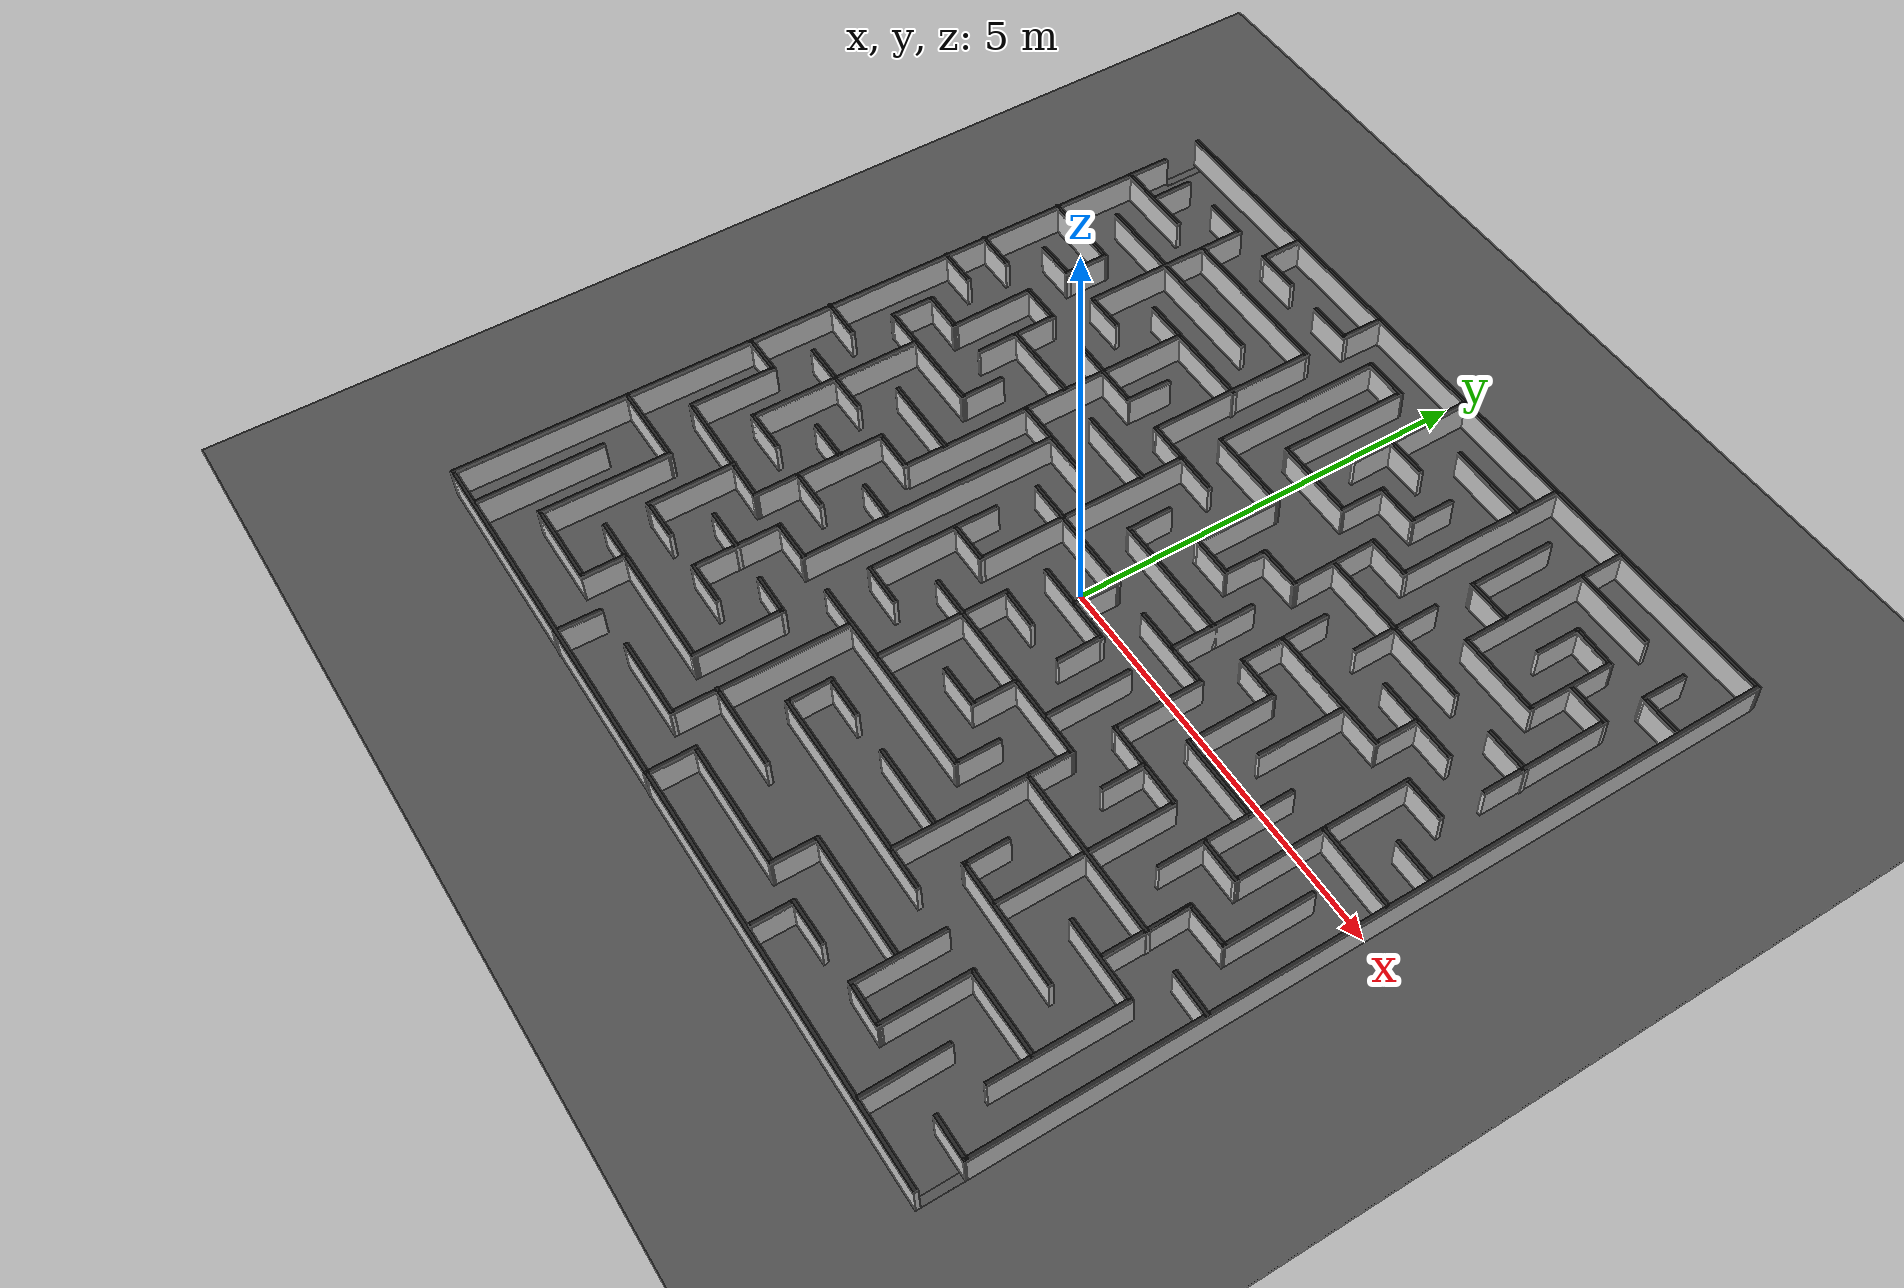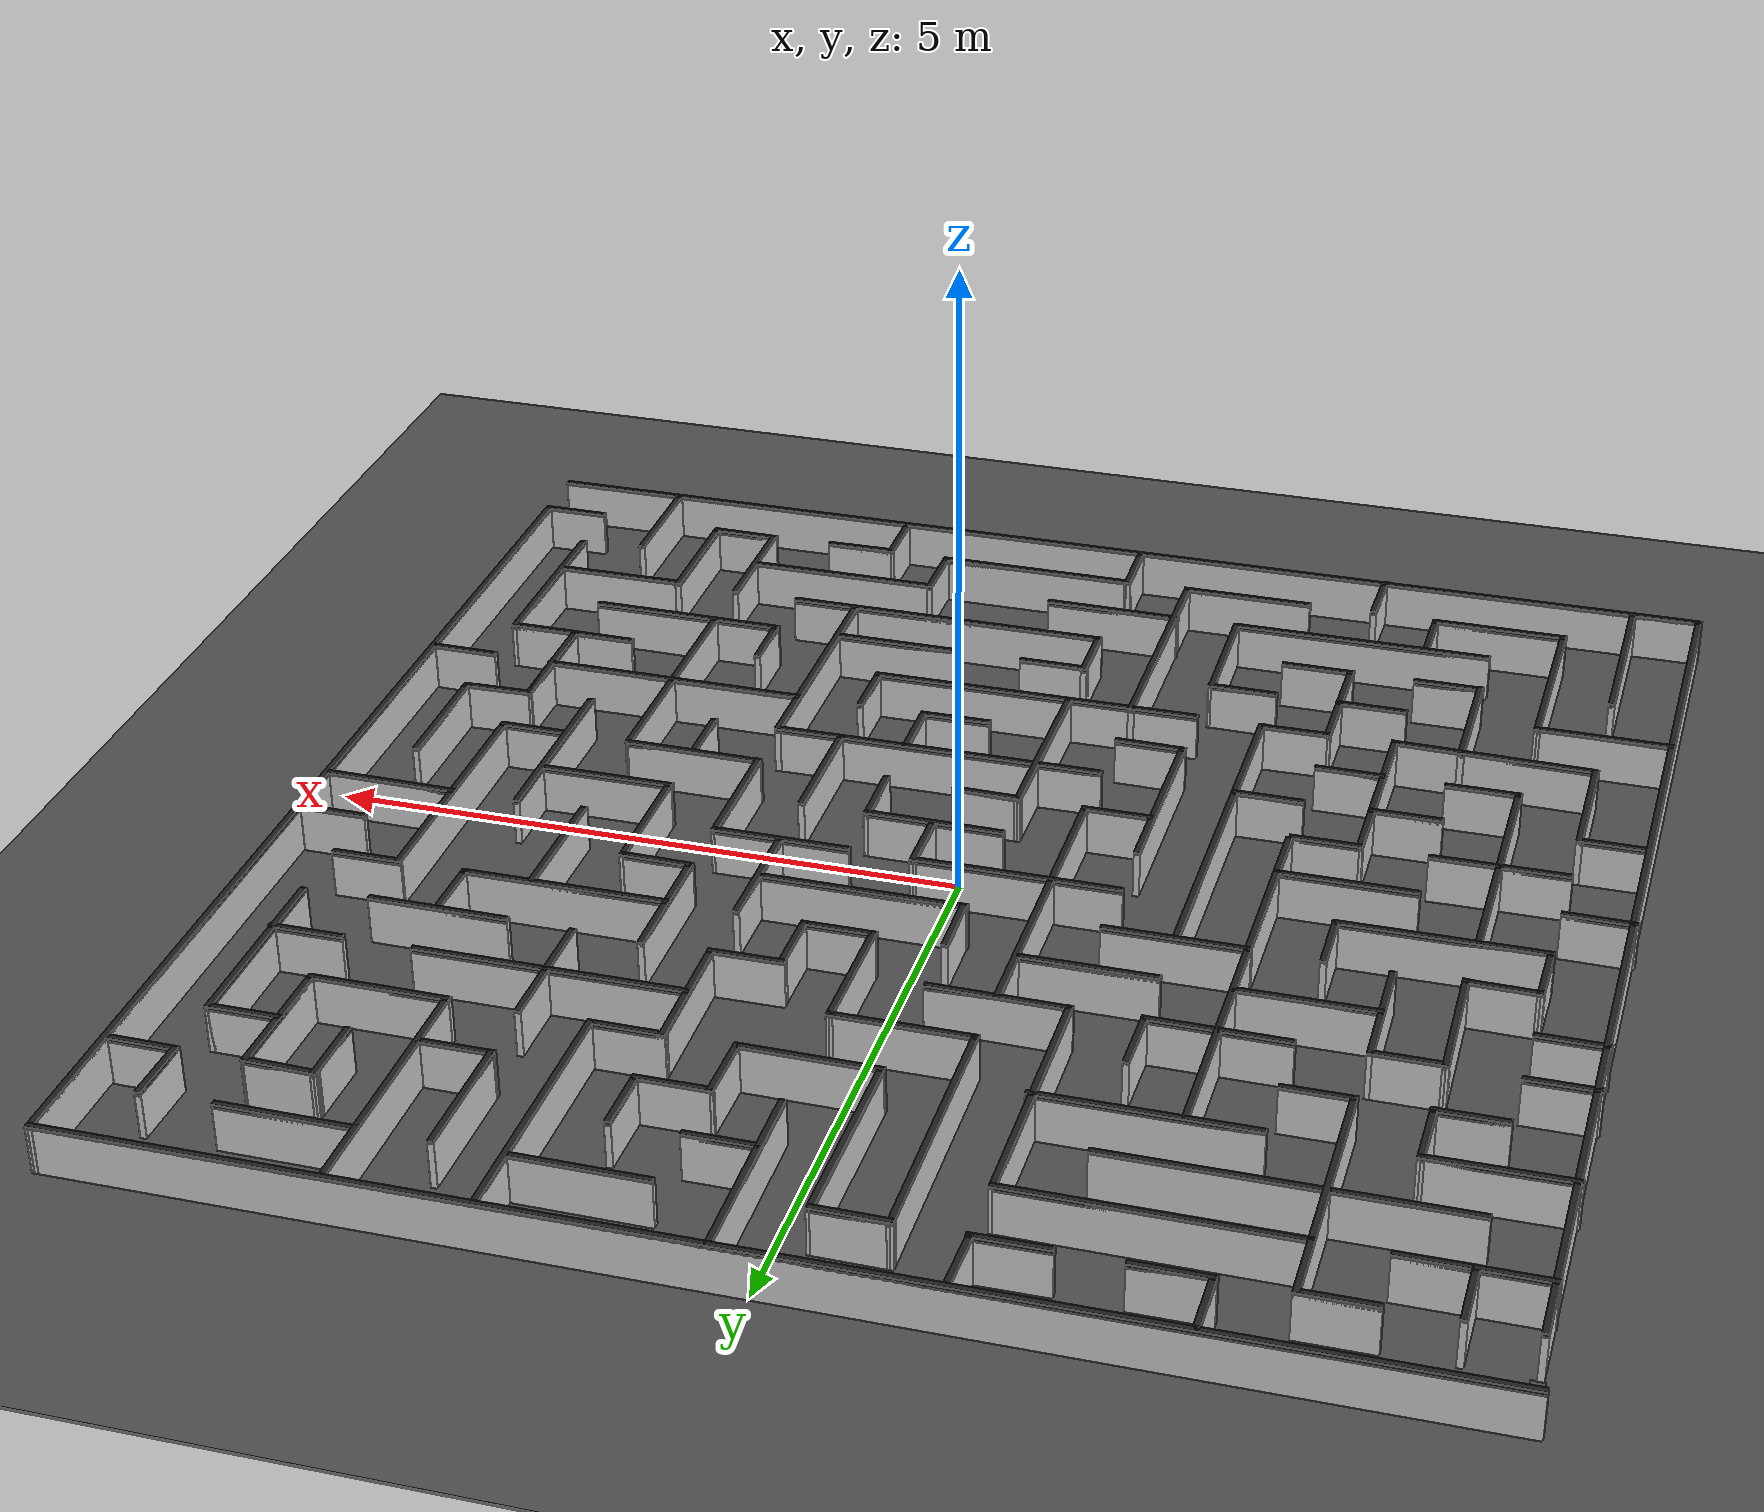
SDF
<sdf version="1.6">
 <world name="default">
  <light name="sun" type="directional">
   <pose>0 0 10 0 -0 0</pose>
   <diffuse>0.8 0.8 0.8 1</diffuse>
   <specular>0.1 0.1 0.1 1</specular>
   <attenuation>
    <range>1000</range>
    <constant>0.9</constant>
    <linear>0.01</linear>
    <quadratic>0.001</quadratic>
   </attenuation>
   <direction>-0.5 0.5 -1</direction>
  </light>
  <model name="ground_plane">
   <static>1</static>
   <link name="link">
    <collision name="collision">
     <geometry><plane><normal>0 0 1</normal><size>100 100</size></plane></geometry>
     <surface><friction><ode><mu>100</mu><mu2>50</mu2></ode></friction></surface>
    </collision>
    <visual name="visual">
     <cast_shadows>0</cast_shadows>
     <geometry><plane><normal>0 0 1</normal><size>100 100</size></plane></geometry>
     <material>
      <script><uri>file://media/materials/scripts/gazebo.material</uri><name>Gazebo/Grey</name></script>
     </material>
    </visual>
   </link>
  </model>
  <gravity>0 0 -9.8</gravity>
  <magnetic_field>6e-06 2.3e-05 -4.2e-05</magnetic_field>
  <atmosphere type="adiabatic"/>
  <physics name="default_physics" default="0" type="ode">
   <max_step_size>0.001</max_step_size>
   <real_time_factor>1</real_time_factor>
   <real_time_update_rate>1000</real_time_update_rate>
  </physics>
  <scene><ambient>0.4 0.4 0.4 1</ambient><background>0.7 0.7 0.7 1</background><shadows>1</shadows></scene>
  <spherical_coordinates>
   <surface_model>EARTH_WGS84</surface_model>
   <latitude_deg>0</latitude_deg>
   <longitude_deg>0</longitude_deg>
   <elevation>0</elevation>
   <heading_deg>0</heading_deg>
  </spherical_coordinates>
  <model name="maze_cross_body">
   <link name="Wall_100">
    <collision name="Wall_100_Collision">
     <geometry><box><size>1.59983 0.05 0.37</size></box></geometry>
     <pose>0 0 0.185 0 -0 0</pose>
    </collision>
    <visual name="Wall_100_Visual">
     <pose>0 0 0.185 0 -0 0</pose>
     <geometry><box><size>1.59983 0.05 0.37</size></box></geometry>
     <material>
      <script><uri>file://media/materials/scripts/gazebo.material</uri><name>Gazebo/White</name></script>
      <ambient>1 1 1 1</ambient>
     </material>
    </visual>
    <pose>-0.249719 -1.55857 0 0 0 -1.57616</pose>
   </link>
   <link name="Wall_102">
    <collision name="Wall_102_Collision">
     <geometry><box><size>0.549064 0.05 0.37</size></box></geometry>
     <pose>0 0 0.185 0 -0 0</pose>
    </collision>
    <visual name="Wall_102_Visual">
     <pose>0 0 0.185 0 -0 0</pose>
     <geometry><box><size>0.549064 0.05 0.37</size></box></geometry>
     <material>
      <script><uri>file://media/materials/scripts/gazebo.material</uri><name>Gazebo/White</name></script>
      <ambient>1 1 1 1</ambient>
     </material>
    </visual>
    <pose>0.003939 -0.787667 0 0 0 -0.016031</pose>
   </link>
   <link name="Wall_104">
    <collision name="Wall_104_Collision">
     <geometry><box><size>1.10225 0.05 0.37</size></box></geometry>
     <pose>0 0 0.185 0 -0 0</pose>
    </collision>
    <visual name="Wall_104_Visual">
     <pose>0 0 0.185 0 -0 0</pose>
     <geometry><box><size>1.10225 0.05 0.37</size></box></geometry>
     <material>
      <script><uri>file://media/materials/scripts/gazebo.material</uri><name>Gazebo/White</name></script>
      <ambient>1 1 1 1</ambient>
     </material>
    </visual>
    <pose>0.280113 -0.273238 0 0 0 -0.007388</pose>
   </link>
   <link name="Wall_106">
    <collision name="Wall_106_Collision">
     <geometry><box><size>0.575262 0.05 0.37</size></box></geometry>
     <pose>0 0 0.185 0 -0 0</pose>
    </collision>
    <visual name="Wall_106_Visual">
     <pose>0 0 0.185 0 -0 0</pose>
     <geometry><box><size>0.575262 0.05 0.37</size></box></geometry>
     <material>
      <script><uri>file://media/materials/scripts/gazebo.material</uri><name>Gazebo/White</name></script>
      <ambient>1 1 1 1</ambient>
     </material>
    </visual>
    <pose>0.806693 -0.539598 0 0 -0 1.58905</pose>
   </link>
   <link name="Wall_108">
    <collision name="Wall_108_Collision">
     <geometry><box><size>0.568453 0.05 0.37</size></box></geometry>
     <pose>0 0 0.185 0 -0 0</pose>
    </collision>
    <visual name="Wall_108_Visual">
     <pose>0 0 0.185 0 -0 0</pose>
     <geometry><box><size>0.568453 0.05 0.37</size></box></geometry>
     <material>
      <script><uri>file://media/materials/scripts/gazebo.material</uri><name>Gazebo/White</name></script>
      <ambient>1 1 1 1</ambient>
     </material>
    </visual>
    <pose>0.284037 0.010875 0 0 -0 1.57077</pose>
   </link>
   <link name="Wall_110">
    <collision name="Wall_110_Collision">
     <geometry><box><size>1.62804 0.05 0.37</size></box></geometry>
     <pose>0 0 0.185 0 -0 0</pose>
    </collision>
    <visual name="Wall_110_Visual">
     <pose>0 0 0.185 0 -0 0</pose>
     <geometry><box><size>1.62804 0.05 0.37</size></box></geometry>
     <material>
      <script><uri>file://media/materials/scripts/gazebo.material</uri><name>Gazebo/White</name></script>
      <ambient>1 1 1 1</ambient>
     </material>
    </visual>
    <pose>-0.504978 0.269875 0 0 -0 0.000287</pose>
   </link>
   <link name="Wall_112">
    <collision name="Wall_112_Collision">
     <geometry><box><size>2.66277 0.05 0.37</size></box></geometry>
     <pose>0 0 0.185 0 -0 0</pose>
    </collision>
    <visual name="Wall_112_Visual">
     <pose>0 0 0.185 0 -0 0</pose>
     <geometry><box><size>2.66277 0.05 0.37</size></box></geometry>
     <material>
      <script><uri>file://media/materials/scripts/gazebo.material</uri><name>Gazebo/White</name></script>
      <ambient>1 1 1 1</ambient>
     </material>
    </visual>
    <pose>-0.777215 0.532264 0 0 0 -1.56866</pose>
   </link>
   <link name="Wall_113">
    <collision name="Wall_113_Collision">
     <geometry><box><size>0.547706 0.05 0.37</size></box></geometry>
     <pose>0 0 0.185 0 -0 0</pose>
    </collision>
    <visual name="Wall_113_Visual">
     <pose>0 0 0.185 0 -0 0</pose>
     <geometry><box><size>0.547706 0.05 0.37</size></box></geometry>
     <material>
      <script><uri>file://media/materials/scripts/gazebo.material</uri><name>Gazebo/White</name></script>
      <ambient>1 1 1 1</ambient>
     </material>
    </visual>
    <pose>-1.02321 -0.774236 0 0 0 -3.14113</pose>
   </link>
   <link name="Wall_115">
    <collision name="Wall_115_Collision">
     <geometry><box><size>1.61623 0.05 0.37</size></box></geometry>
     <pose>0 0 0.185 0 -0 0</pose>
    </collision>
    <visual name="Wall_115_Visual">
     <pose>0 0 0.185 0 -0 0</pose>
     <geometry><box><size>1.61623 0.05 0.37</size></box></geometry>
     <material>
      <script><uri>file://media/materials/scripts/gazebo.material</uri><name>Gazebo/White</name></script>
      <ambient>1 1 1 1</ambient>
     </material>
    </visual>
    <pose>-1.3 -1.05435 0 0 0 -1.5708</pose>
   </link>
   <link name="Wall_116">
    <collision name="Wall_116_Collision">
     <geometry><box><size>0.564169 0.05 0.37</size></box></geometry>
     <pose>0 0 0.185 0 -0 0</pose>
    </collision>
    <visual name="Wall_116_Visual">
     <pose>0 0 0.185 0 -0 0</pose>
     <geometry><box><size>0.564169 0.05 0.37</size></box></geometry>
     <material>
      <script><uri>file://media/materials/scripts/gazebo.material</uri><name>Gazebo/White</name></script>
      <ambient>1 1 1 1</ambient>
     </material>
    </visual>
    <pose>-1.043 -1.84035 0 0 0 -0.011673</pose>
   </link>
   <link name="Wall_118">
    <collision name="Wall_118_Collision">
     <geometry><box><size>3.19574 0.05 0.37</size></box></geometry>
     <pose>0 0 0.185 0 -0 0</pose>
    </collision>
    <visual name="Wall_118_Visual">
     <pose>0 0 0.185 0 -0 0</pose>
     <geometry><box><size>3.19574 0.05 0.37</size></box></geometry>
     <material>
      <script><uri>file://media/materials/scripts/gazebo.material</uri><name>Gazebo/White</name></script>
      <ambient>1 1 1 1</ambient>
     </material>
    </visual>
    <pose>-1.825 -0.790222 0 0 0 -1.5708</pose>
   </link>
   <link name="Wall_120">
    <collision name="Wall_120_Collision">
     <geometry><box><size>0.579843 0.05 0.37</size></box></geometry>
     <pose>0 0 0.185 0 -0 0</pose>
    </collision>
    <visual name="Wall_120_Visual">
     <pose>0 0 0.185 0 -0 0</pose>
     <geometry><box><size>0.579843 0.05 0.37</size></box></geometry>
     <material>
      <script><uri>file://media/materials/scripts/gazebo.material</uri><name>Gazebo/White</name></script>
      <ambient>1 1 1 1</ambient>
     </material>
    </visual>
    <pose>-2.09 -2.36036 0 0 0 -3.13031</pose>
   </link>
   <link name="Wall_122">
    <collision name="Wall_122_Collision">
     <geometry><box><size>1.09021 0.05 0.37</size></box></geometry>
     <pose>0 0 0.185 0 -0 0</pose>
    </collision>
    <visual name="Wall_122_Visual">
     <pose>0 0 0.185 0 -0 0</pose>
     <geometry><box><size>1.09021 0.05 0.37</size></box></geometry>
     <material>
      <script><uri>file://media/materials/scripts/gazebo.material</uri><name>Gazebo/White</name></script>
      <ambient>1 1 1 1</ambient>
     </material>
    </visual>
    <pose>-2.35491 -2.88345 0 0 0 -1.57062</pose>
   </link>
   <link name="Wall_123">
    <collision name="Wall_123_Collision">
     <geometry><box><size>0.587478 0.05 0.37</size></box></geometry>
     <pose>0 0 0.185 0 -0 0</pose>
    </collision>
    <visual name="Wall_123_Visual">
     <pose>0 0 0.185 0 -0 0</pose>
     <geometry><box><size>0.587478 0.05 0.37</size></box></geometry>
     <material>
      <script><uri>file://media/materials/scripts/gazebo.material</uri><name>Gazebo/White</name></script>
      <ambient>1 1 1 1</ambient>
     </material>
    </visual>
    <pose>-2.08609 -3.40356 0 0 -0 0</pose>
   </link>
   <link name="Wall_125">
    <collision name="Wall_125_Collision">
     <geometry><box><size>0.57 0.05 0.37</size></box></geometry>
     <pose>0 0 0.185 0 -0 0</pose>
    </collision>
    <visual name="Wall_125_Visual">
     <pose>0 0 0.185 0 -0 0</pose>
     <geometry><box><size>0.57 0.05 0.37</size></box></geometry>
     <material>
      <script><uri>file://media/materials/scripts/gazebo.material</uri><name>Gazebo/White</name></script>
      <ambient>1 1 1 1</ambient>
     </material>
    </visual>
    <pose>-2.61235 -2.88906 0 0 -0 0</pose>
   </link>
   <link name="Wall_127">
    <collision name="Wall_127_Collision">
     <geometry><box><size>1.1003 0.05 0.37</size></box></geometry>
     <pose>0 0 0.185 0 -0 0</pose>
    </collision>
    <visual name="Wall_127_Visual">
     <pose>0 0 0.185 0 -0 0</pose>
     <geometry><box><size>1.1003 0.05 0.37</size></box></geometry>
     <material>
      <script><uri>file://media/materials/scripts/gazebo.material</uri><name>Gazebo/White</name></script>
      <ambient>1 1 1 1</ambient>
     </material>
    </visual>
    <pose>-3.40784 -2.8905 0 0 0 -1.56668</pose>
   </link>
   <link name="Wall_128">
    <collision name="Wall_128_Collision">
     <geometry><box><size>0.56 0.05 0.37</size></box></geometry>
     <pose>0 0 0.185 0 -0 0</pose>
    </collision>
    <visual name="Wall_128_Visual">
     <pose>0 0 0.185 0 -0 0</pose>
     <geometry><box><size>0.56 0.05 0.37</size></box></geometry>
     <material>
      <script><uri>file://media/materials/scripts/gazebo.material</uri><name>Gazebo/White</name></script>
      <ambient>1 1 1 1</ambient>
     </material>
    </visual>
    <pose>-3.15068 -3.41132 0 0 -0 0</pose>
   </link>
   <link name="Wall_130">
    <collision name="Wall_130_Collision">
     <geometry><box><size>1.57814 0.05 0.37</size></box></geometry>
     <pose>0 0 0.185 0 -0 0</pose>
    </collision>
    <visual name="Wall_130_Visual">
     <pose>0 0 0.185 0 -0 0</pose>
     <geometry><box><size>1.57814 0.05 0.37</size></box></geometry>
     <material>
      <script><uri>file://media/materials/scripts/gazebo.material</uri><name>Gazebo/White</name></script>
      <ambient>1 1 1 1</ambient>
     </material>
    </visual>
    <pose>-3.6482 -2.36898 0 0 0 -0.019342</pose>
   </link>
   <link name="Wall_132">
    <collision name="Wall_132_Collision">
     <geometry><box><size>1.08525 0.05 0.37</size></box></geometry>
     <pose>0 0 0.185 0 -0 0</pose>
    </collision>
    <visual name="Wall_132_Visual">
     <pose>0 0 0.185 0 -0 0</pose>
     <geometry><box><size>1.08525 0.05 0.37</size></box></geometry>
     <material>
      <script><uri>file://media/materials/scripts/gazebo.material</uri><name>Gazebo/White</name></script>
      <ambient>1 1 1 1</ambient>
     </material>
    </visual>
    <pose>-4.458 -1.83085 0 0 0 -1.5708</pose>
   </link>
   <link name="Wall_134">
    <collision name="Wall_134_Collision">
     <geometry><box><size>0.57 0.05 0.37</size></box></geometry>
     <pose>0 0 0.185 0 -0 0</pose>
    </collision>
    <visual name="Wall_134_Visual">
     <pose>0 0 0.185 0 -0 0</pose>
     <geometry><box><size>0.57 0.05 0.37</size></box></geometry>
     <material>
      <script><uri>file://media/materials/scripts/gazebo.material</uri><name>Gazebo/White</name></script>
      <ambient>1 1 1 1</ambient>
     </material>
    </visual>
    <pose>-4.718 -1.31335 0 0 -0 0</pose>
   </link>
   <link name="Wall_136">
    <collision name="Wall_136_Collision">
     <geometry><box><size>2.15 0.05 0.37</size></box></geometry>
     <pose>0 0 0.185 0 -0 0</pose>
    </collision>
    <visual name="Wall_136_Visual">
     <pose>0 0 0.185 0 -0 0</pose>
     <geometry><box><size>2.15 0.05 0.37</size></box></geometry>
     <material>
      <script><uri>file://media/materials/scripts/gazebo.material</uri><name>Gazebo/White</name></script>
      <ambient>1 1 1 1</ambient>
     </material>
    </visual>
    <pose>-3.93021 -0.795276 0 0 0 -1.57059</pose>
   </link>
   <link name="Wall_138">
    <collision name="Wall_138_Collision">
     <geometry><box><size>0.591678 0.05 0.37</size></box></geometry>
     <pose>0 0 0.185 0 -0 0</pose>
    </collision>
    <visual name="Wall_138_Visual">
     <pose>0 0 0.185 0 -0 0</pose>
     <geometry><box><size>0.591678 0.05 0.37</size></box></geometry>
     <material>
      <script><uri>file://media/materials/scripts/gazebo.material</uri><name>Gazebo/White</name></script>
      <ambient>1 1 1 1</ambient>
     </material>
    </visual>
    <pose>-3.659 -1.84435 0 0 -0 0.00369</pose>
   </link>
   <link name="Wall_140">
    <collision name="Wall_140_Collision">
     <geometry><box><size>1.06924 0.05 0.37</size></box></geometry>
     <pose>0 0 0.185 0 -0 0</pose>
    </collision>
    <visual name="Wall_140_Visual">
     <pose>0 0 0.185 0 -0 0</pose>
     <geometry><box><size>1.06924 0.05 0.37</size></box></geometry>
     <material>
      <script><uri>file://media/materials/scripts/gazebo.material</uri><name>Gazebo/White</name></script>
      <ambient>1 1 1 1</ambient>
     </material>
    </visual>
    <pose>-3.9375 -0.787851 0 0 -0 0.006869</pose>
   </link>
   <link name="Wall_142">
    <collision name="Wall_142_Collision">
     <geometry><box><size>1.60626 0.05 0.37</size></box></geometry>
     <pose>0 0 0.185 0 -0 0</pose>
    </collision>
    <visual name="Wall_142_Visual">
     <pose>0 0 0.185 0 -0 0</pose>
     <geometry><box><size>1.60626 0.05 0.37</size></box></geometry>
     <material>
      <script><uri>file://media/materials/scripts/gazebo.material</uri><name>Gazebo/White</name></script>
      <ambient>1 1 1 1</ambient>
     </material>
    </visual>
    <pose>-3.67313 0.277908 0 0 -0 0.003522</pose>
   </link>
   <link name="Wall_143">
    <collision name="Wall_143_Collision">
     <geometry><box><size>0.556614 0.05 0.37</size></box></geometry>
     <pose>0 0 0.185 0 -0 0</pose>
    </collision>
    <visual name="Wall_143_Visual">
     <pose>0 0 0.185 0 -0 0</pose>
     <geometry><box><size>0.556614 0.05 0.37</size></box></geometry>
     <material>
      <script><uri>file://media/materials/scripts/gazebo.material</uri><name>Gazebo/White</name></script>
      <ambient>1 1 1 1</ambient>
     </material>
    </visual>
    <pose>-2.89814 0.533936 0 0 -0 1.58318</pose>
   </link>
   <link name="Wall_145">
    <collision name="Wall_145_Collision">
     <geometry><box><size>0.569038 0.05 0.37</size></box></geometry>
     <pose>0 0 0.185 0 -0 0</pose>
    </collision>
    <visual name="Wall_145_Visual">
     <pose>0 0 0.185 0 -0 0</pose>
     <geometry><box><size>0.569038 0.05 0.37</size></box></geometry>
     <material>
      <script><uri>file://media/materials/scripts/gazebo.material</uri><name>Gazebo/White</name></script>
      <ambient>1 1 1 1</ambient>
     </material>
    </visual>
    <pose>-4.44811 0.534667 0 0 0 -1.58294</pose>
   </link>
   <link name="Wall_147">
    <collision name="Wall_147_Collision">
     <geometry><box><size>0.580958 0.05 0.37</size></box></geometry>
     <pose>0 0 0.185 0 -0 0</pose>
    </collision>
    <visual name="Wall_147_Visual">
     <pose>0 0 0.185 0 -0 0</pose>
     <geometry><box><size>0.580958 0.05 0.37</size></box></geometry>
     <material>
      <script><uri>file://media/materials/scripts/gazebo.material</uri><name>Gazebo/White</name></script>
      <ambient>1 1 1 1</ambient>
     </material>
    </visual>
    <pose>-4.17954 0.790408 0 0 0 -0.014163</pose>
   </link>
   <link name="Wall_148">
    <collision name="Wall_148_Collision">
     <geometry><box><size>1.08977 0.05 0.37</size></box></geometry>
     <pose>0 0 0.185 0 -0 0</pose>
    </collision>
    <visual name="Wall_148_Visual">
     <pose>0 0 0.185 0 -0 0</pose>
     <geometry><box><size>1.08977 0.05 0.37</size></box></geometry>
     <material>
      <script><uri>file://media/materials/scripts/gazebo.material</uri><name>Gazebo/White</name></script>
      <ambient>1 1 1 1</ambient>
     </material>
    </visual>
    <pose>-3.92406 1.29986 0 0 -0 1.58991</pose>
   </link>
   <link name="Wall_149">
    <collision name="Wall_149_Collision">
     <geometry><box><size>0.569373 0.05 0.37</size></box></geometry>
     <pose>0 0 0.185 0 -0 0</pose>
    </collision>
    <visual name="Wall_149_Visual">
     <pose>0 0 0.185 0 -0 0</pose>
     <geometry><box><size>0.569373 0.05 0.37</size></box></geometry>
     <material>
      <script><uri>file://media/materials/scripts/gazebo.material</uri><name>Gazebo/White</name></script>
      <ambient>1 1 1 1</ambient>
     </material>
    </visual>
    <pose>-3.6745 1.81915 0 0 0 -0.001927</pose>
   </link>
   <link name="Wall_150">
    <collision name="Wall_150_Collision">
     <geometry><box><size>1.04254 0.05 0.37</size></box></geometry>
     <pose>0 0 0.185 0 -0 0</pose>
    </collision>
    <visual name="Wall_150_Visual">
     <pose>0 0 0.185 0 -0 0</pose>
     <geometry><box><size>1.04254 0.05 0.37</size></box></geometry>
     <material>
      <script><uri>file://media/materials/scripts/gazebo.material</uri><name>Gazebo/White</name></script>
      <ambient>1 1 1 1</ambient>
     </material>
    </visual>
    <pose>-3.408 1.32265 0 0 0 -1.55668</pose>
   </link>
   <link name="Wall_152">
    <collision name="Wall_152_Collision">
     <geometry><box><size>1.08297 0.05 0.37</size></box></geometry>
     <pose>0 0 0.185 0 -0 0</pose>
    </collision>
    <visual name="Wall_152_Visual">
     <pose>0 0 0.185 0 -0 0</pose>
     <geometry><box><size>1.08297 0.05 0.37</size></box></geometry>
     <material>
      <script><uri>file://media/materials/scripts/gazebo.material</uri><name>Gazebo/White</name></script>
      <ambient>1 1 1 1</ambient>
     </material>
    </visual>
    <pose>-2.8875 1.31615 0 0 -0 0.002904</pose>
   </link>
   <link name="Wall_154">
    <collision name="Wall_154_Collision">
     <geometry><box><size>3.65 0.05 0.37</size></box></geometry>
     <pose>0 0 0.185 0 -0 0</pose>
    </collision>
    <visual name="Wall_154_Visual">
     <pose>0 0 0.185 0 -0 0</pose>
     <geometry><box><size>3.65 0.05 0.37</size></box></geometry>
     <material>
      <script><uri>file://media/materials/scripts/gazebo.material</uri><name>Gazebo/White</name></script>
      <ambient>1 1 1 1</ambient>
     </material>
    </visual>
    <pose>-2.355 1.05565 0 0 0 -1.5708</pose>
   </link>
   <link name="Wall_156">
    <collision name="Wall_156_Collision">
     <geometry><box><size>1.09 0.05 0.37</size></box></geometry>
     <pose>0 0 0.185 0 -0 0</pose>
    </collision>
    <visual name="Wall_156_Visual">
     <pose>0 0 0.185 0 -0 0</pose>
     <geometry><box><size>1.09 0.05 0.37</size></box></geometry>
     <material>
      <script><uri>file://media/materials/scripts/gazebo.material</uri><name>Gazebo/White</name></script>
      <ambient>1 1 1 1</ambient>
     </material>
    </visual>
    <pose>-2.87741 -0.271069 0 0 -0 0</pose>
   </link>
   <link name="Wall_158">
    <collision name="Wall_158_Collision">
     <geometry><box><size>0.558601 0.05 0.37</size></box></geometry>
     <pose>0 0 0.185 0 -0 0</pose>
    </collision>
    <visual name="Wall_158_Visual">
     <pose>0 0 0.185 0 -0 0</pose>
     <geometry><box><size>0.558601 0.05 0.37</size></box></geometry>
     <material>
      <script><uri>file://media/materials/scripts/gazebo.material</uri><name>Gazebo/White</name></script>
      <ambient>1 1 1 1</ambient>
     </material>
    </visual>
    <pose>-2.63071 -0.790068 0 0 -0 0.001113</pose>
   </link>
   <link name="Wall_160">
    <collision name="Wall_160_Collision">
     <geometry><box><size>1.6434 0.05 0.37</size></box></geometry>
     <pose>0 0 0.185 0 -0 0</pose>
    </collision>
    <visual name="Wall_160_Visual">
     <pose>0 0 0.185 0 -0 0</pose>
     <geometry><box><size>1.6434 0.05 0.37</size></box></geometry>
     <material>
      <script><uri>file://media/materials/scripts/gazebo.material</uri><name>Gazebo/White</name></script>
      <ambient>1 1 1 1</ambient>
     </material>
    </visual>
    <pose>-2.88464 -1.58705 0 0 0 -1.57034</pose>
   </link>
   <link name="Wall_162">
    <collision name="Wall_162_Collision">
     <geometry><box><size>1.108 0.05 0.37</size></box></geometry>
     <pose>0 0 0.185 0 -0 0</pose>
    </collision>
    <visual name="Wall_162_Visual">
     <pose>0 0 0.185 0 -0 0</pose>
     <geometry><box><size>1.108 0.05 0.37</size></box></geometry>
     <material>
      <script><uri>file://media/materials/scripts/gazebo.material</uri><name>Gazebo/White</name></script>
      <ambient>1 1 1 1</ambient>
     </material>
    </visual>
    <pose>-1.82612 0.79121 0 0 -0 0</pose>
   </link>
   <link name="Wall_164">
    <collision name="Wall_164_Collision">
     <geometry><box><size>1.08602 0.05 0.37</size></box></geometry>
     <pose>0 0 0.185 0 -0 0</pose>
    </collision>
    <visual name="Wall_164_Visual">
     <pose>0 0 0.185 0 -0 0</pose>
     <geometry><box><size>1.08602 0.05 0.37</size></box></geometry>
     <material>
      <script><uri>file://media/materials/scripts/gazebo.material</uri><name>Gazebo/White</name></script>
      <ambient>1 1 1 1</ambient>
     </material>
    </visual>
    <pose>-2.35401 1.83312 0 0 0 -0.006702</pose>
   </link>
   <link name="Wall_166">
    <collision name="Wall_166_Collision">
     <geometry><box><size>0.577563 0.05 0.37</size></box></geometry>
     <pose>0 0 0.185 0 -0 0</pose>
    </collision>
    <visual name="Wall_166_Visual">
     <pose>0 0 0.185 0 -0 0</pose>
     <geometry><box><size>0.577563 0.05 0.37</size></box></geometry>
     <material>
      <script><uri>file://media/materials/scripts/gazebo.material</uri><name>Gazebo/White</name></script>
      <ambient>1 1 1 1</ambient>
     </material>
    </visual>
    <pose>-1.833 2.09365 0 0 -0 1.55943</pose>
   </link>
   <link name="Wall_168">
    <collision name="Wall_168_Collision">
     <geometry><box><size>1.64999 0.05 0.37</size></box></geometry>
     <pose>0 0 0.185 0 -0 0</pose>
    </collision>
    <visual name="Wall_168_Visual">
     <pose>0 0 0.185 0 -0 0</pose>
     <geometry><box><size>1.64999 0.05 0.37</size></box></geometry>
     <material>
      <script><uri>file://media/materials/scripts/gazebo.material</uri><name>Gazebo/White</name></script>
      <ambient>1 1 1 1</ambient>
     </material>
    </visual>
    <pose>-2.081 2.89265 0 0 -0 0</pose>
   </link>
   <link name="Wall_170">
    <collision name="Wall_170_Collision">
     <geometry><box><size>2.14274 0.05 0.37</size></box></geometry>
     <pose>0 0 0.185 0 -0 0</pose>
    </collision>
    <visual name="Wall_170_Visual">
     <pose>0 0 0.185 0 -0 0</pose>
     <geometry><box><size>2.14274 0.05 0.37</size></box></geometry>
     <material>
      <script><uri>file://media/materials/scripts/gazebo.material</uri><name>Gazebo/White</name></script>
      <ambient>1 1 1 1</ambient>
     </material>
    </visual>
    <pose>-1.30774 2.89428 0 0 0 -1.56672</pose>
   </link>
   <link name="Wall_172">
    <collision name="Wall_172_Collision">
     <geometry><box><size>1.08005 0.05 0.37</size></box></geometry>
     <pose>0 0 0.185 0 -0 0</pose>
    </collision>
    <visual name="Wall_172_Visual">
     <pose>0 0 0.185 0 -0 0</pose>
     <geometry><box><size>1.08005 0.05 0.37</size></box></geometry>
     <material>
      <script><uri>file://media/materials/scripts/gazebo.material</uri><name>Gazebo/White</name></script>
      <ambient>1 1 1 1</ambient>
     </material>
    </visual>
    <pose>-0.788472 1.84575 0 0 0 -0.009708</pose>
   </link>
   <link name="Wall_175">
    <collision name="Wall_175_Collision">
     <geometry><box><size>1.05434 0.05 0.37</size></box></geometry>
     <pose>0 0 0.185 0 -0 0</pose>
    </collision>
    <visual name="Wall_175_Visual">
     <pose>0 0 0.185 0 -0 0</pose>
     <geometry><box><size>1.05434 0.05 0.37</size></box></geometry>
     <material>
      <script><uri>file://media/materials/scripts/gazebo.material</uri><name>Gazebo/White</name></script>
      <ambient>1 1 1 1</ambient>
     </material>
    </visual>
    <pose>-1.306 1.31515 0 0 -0 0.000996</pose>
   </link>
   <link name="Wall_178">
    <collision name="Wall_178_Collision">
     <geometry><box><size>0.562747 0.05 0.37</size></box></geometry>
     <pose>0 0 0.185 0 -0 0</pose>
    </collision>
    <visual name="Wall_178_Visual">
     <pose>0 0 0.185 0 -0 0</pose>
     <geometry><box><size>0.562747 0.05 0.37</size></box></geometry>
     <material>
      <script><uri>file://media/materials/scripts/gazebo.material</uri><name>Gazebo/White</name></script>
      <ambient>1 1 1 1</ambient>
     </material>
    </visual>
    <pose>-3.1485 -1.32335 0 0 -0 0</pose>
   </link>
   <link name="Wall_180">
    <collision name="Wall_180_Collision">
     <geometry><box><size>0.562923 0.05 0.37</size></box></geometry>
     <pose>0 0 0.185 0 -0 0</pose>
    </collision>
    <visual name="Wall_180_Visual">
     <pose>0 0 0.185 0 -0 0</pose>
     <geometry><box><size>0.562923 0.05 0.37</size></box></geometry>
     <material>
      <script><uri>file://media/materials/scripts/gazebo.material</uri><name>Gazebo/White</name></script>
      <ambient>1 1 1 1</ambient>
     </material>
    </visual>
    <pose>-2.0835 -1.31035 0 0 -0 0</pose>
   </link>
   <link name="Wall_182">
    <collision name="Wall_182_Collision">
     <geometry><box><size>0.55 0.05 0.37</size></box></geometry>
     <pose>0 0 0.185 0 -0 0</pose>
    </collision>
    <visual name="Wall_182_Visual">
     <pose>0 0 0.185 0 -0 0</pose>
     <geometry><box><size>0.55 0.05 0.37</size></box></geometry>
     <material>
      <script><uri>file://media/materials/scripts/gazebo.material</uri><name>Gazebo/White</name></script>
      <ambient>1 1 1 1</ambient>
     </material>
    </visual>
    <pose>-2.62468 -1.84671 0 0 -0 0</pose>
   </link>
   <link name="Wall_184">
    <collision name="Wall_184_Collision">
     <geometry><box><size>0.542511 0.05 0.37</size></box></geometry>
     <pose>0 0 0.185 0 -0 0</pose>
    </collision>
    <visual name="Wall_184_Visual">
     <pose>0 0 0.185 0 -0 0</pose>
     <geometry><box><size>0.542511 0.05 0.37</size></box></geometry>
     <material>
      <script><uri>file://media/materials/scripts/gazebo.material</uri><name>Gazebo/White</name></script>
      <ambient>1 1 1 1</ambient>
     </material>
    </visual>
    <pose>-4.732 1.31315 0 0 0 -0.006097</pose>
   </link>
   <link name="Wall_186">
    <collision name="Wall_186_Collision">
     <geometry><box><size>0.554018 0.05 0.37</size></box></geometry>
     <pose>0 0 0.185 0 -0 0</pose>
    </collision>
    <visual name="Wall_186_Visual">
     <pose>0 0 0.185 0 -0 0</pose>
     <geometry><box><size>0.554018 0.05 0.37</size></box></geometry>
     <material>
      <script><uri>file://media/materials/scripts/gazebo.material</uri><name>Gazebo/White</name></script>
      <ambient>1 1 1 1</ambient>
     </material>
    </visual>
    <pose>-4.73 1.84165 0 0 -0 0</pose>
   </link>
   <link name="Wall_188">
    <collision name="Wall_188_Collision">
     <geometry><box><size>1.09105 0.05 0.37</size></box></geometry>
     <pose>0 0 0.185 0 -0 0</pose>
    </collision>
    <visual name="Wall_188_Visual">
     <pose>0 0 0.185 0 -0 0</pose>
     <geometry><box><size>1.09105 0.05 0.37</size></box></geometry>
     <material>
      <script><uri>file://media/materials/scripts/gazebo.material</uri><name>Gazebo/White</name></script>
      <ambient>1 1 1 1</ambient>
     </material>
    </visual>
    <pose>-4.45348 2.89108 0 0 -0 0.005045</pose>
   </link>
   <link name="Wall_189">
    <collision name="Wall_189_Collision">
     <geometry><box><size>0.586306 0.05 0.37</size></box></geometry>
     <pose>0 0 0.185 0 -0 0</pose>
    </collision>
    <visual name="Wall_189_Visual">
     <pose>0 0 0.185 0 -0 0</pose>
     <geometry><box><size>0.586306 0.05 0.37</size></box></geometry>
     <material>
      <script><uri>file://media/materials/scripts/gazebo.material</uri><name>Gazebo/White</name></script>
      <ambient>1 1 1 1</ambient>
     </material>
    </visual>
    <pose>-3.9336 2.62556 0 0 0 -1.57315</pose>
   </link>
   <link name="Wall_190">
    <collision name="Wall_190_Collision">
     <geometry><box><size>0.553846 0.05 0.37</size></box></geometry>
     <pose>0 0 0.185 0 -0 0</pose>
    </collision>
    <visual name="Wall_190_Visual">
     <pose>0 0 0.185 0 -0 0</pose>
     <geometry><box><size>0.553846 0.05 0.37</size></box></geometry>
     <material>
      <script><uri>file://media/materials/scripts/gazebo.material</uri><name>Gazebo/White</name></script>
      <ambient>1 1 1 1</ambient>
     </material>
    </visual>
    <pose>-4.18368 2.35913 0 0 0 -3.13864</pose>
   </link>
   <link name="Wall_193">
    <collision name="Wall_193_Collision">
     <geometry><box><size>0.564228 0.05 0.37</size></box></geometry>
     <pose>0 0 0.185 0 -0 0</pose>
    </collision>
    <visual name="Wall_193_Visual">
     <pose>0 0 0.185 0 -0 0</pose>
     <geometry><box><size>0.564228 0.05 0.37</size></box></geometry>
     <material>
      <script><uri>file://media/materials/scripts/gazebo.material</uri><name>Gazebo/White</name></script>
      <ambient>1 1 1 1</ambient>
     </material>
    </visual>
    <pose>-4.734 -0.267351 0 0 -0 3.12992</pose>
   </link>
   <link name="Wall_195">
    <collision name="Wall_195_Collision">
     <geometry><box><size>0.601725 0.05 0.37</size></box></geometry>
     <pose>0 0 0.185 0 -0 0</pose>
    </collision>
    <visual name="Wall_195_Visual">
     <pose>0 0 0.185 0 -0 0</pose>
     <geometry><box><size>0.601725 0.05 0.37</size></box></geometry>
     <material>
      <script><uri>file://media/materials/scripts/gazebo.material</uri><name>Gazebo/White</name></script>
      <ambient>1 1 1 1</ambient>
     </material>
    </visual>
    <pose>-0.2465 -4.73535 0 0 0 -1.55812</pose>
   </link>
   <link name="Wall_197">
    <collision name="Wall_197_Collision">
     <geometry><box><size>1.65 0.05 0.37</size></box></geometry>
     <pose>0 0 0.185 0 -0 0</pose>
    </collision>
    <visual name="Wall_197_Visual">
     <pose>0 0 0.185 0 -0 0</pose>
     <geometry><box><size>1.65 0.05 0.37</size></box></geometry>
     <material>
      <script><uri>file://media/materials/scripts/gazebo.material</uri><name>Gazebo/White</name></script>
      <ambient>1 1 1 1</ambient>
     </material>
    </visual>
    <pose>0.55 -4.45935 0 0 -0 0</pose>
   </link>
   <link name="Wall_198">
    <collision name="Wall_198_Collision">
     <geometry><box><size>0.564496 0.05 0.37</size></box></geometry>
     <pose>0 0 0.185 0 -0 0</pose>
    </collision>
    <visual name="Wall_198_Visual">
     <pose>0 0 0.185 0 -0 0</pose>
     <geometry><box><size>0.564496 0.05 0.37</size></box></geometry>
     <material>
      <script><uri>file://media/materials/scripts/gazebo.material</uri><name>Gazebo/White</name></script>
      <ambient>1 1 1 1</ambient>
     </material>
    </visual>
    <pose>1.3515 -4.20235 0 0 -0 1.56496</pose>
   </link>
   <link name="Wall_199">
    <collision name="Wall_199_Collision">
     <geometry><box><size>1.60756 0.05 0.37</size></box></geometry>
     <pose>0 0 0.185 0 -0 0</pose>
    </collision>
    <visual name="Wall_199_Visual">
     <pose>0 0 0.185 0 -0 0</pose>
     <geometry><box><size>1.60756 0.05 0.37</size></box></geometry>
     <material>
      <script><uri>file://media/materials/scripts/gazebo.material</uri><name>Gazebo/White</name></script>
      <ambient>1 1 1 1</ambient>
     </material>
    </visual>
    <pose>2.132 -3.94535 0 0 -0 0</pose>
   </link>
   <link name="Wall_201">
    <collision name="Wall_201_Collision">
     <geometry><box><size>0.504061 0.05 0.37</size></box></geometry>
     <pose>0 0 0.185 0 -0 0</pose>
    </collision>
    <visual name="Wall_201_Visual">
     <pose>0 0 0.185 0 -0 0</pose>
     <geometry><box><size>0.504061 0.05 0.37</size></box></geometry>
     <material>
      <script><uri>file://media/materials/scripts/gazebo.material</uri><name>Gazebo/White</name></script>
      <ambient>1 1 1 1</ambient>
     </material>
    </visual>
    <pose>1.852 -4.70835 0 0 0 -1.5708</pose>
   </link>
   <link name="Wall_203">
    <collision name="Wall_203_Collision">
     <geometry><box><size>0.586874 0.05 0.37</size></box></geometry>
     <pose>0 0 0.185 0 -0 0</pose>
    </collision>
    <visual name="Wall_203_Visual">
     <pose>0 0 0.185 0 -0 0</pose>
     <geometry><box><size>0.586874 0.05 0.37</size></box></geometry>
     <material>
      <script><uri>file://media/materials/scripts/gazebo.material</uri><name>Gazebo/White</name></script>
      <ambient>1 1 1 1</ambient>
     </material>
    </visual>
    <pose>2.1205 -4.47785 0 0 -0 0.013035</pose>
   </link>
   <link name="Wall_205">
    <collision name="Wall_205_Collision">
     <geometry><box><size>1.08389 0.05 0.37</size></box></geometry>
     <pose>0 0 0.185 0 -0 0</pose>
    </collision>
    <visual name="Wall_205_Visual">
     <pose>0 0 0.185 0 -0 0</pose>
     <geometry><box><size>1.08389 0.05 0.37</size></box></geometry>
     <material>
      <script><uri>file://media/materials/scripts/gazebo.material</uri><name>Gazebo/White</name></script>
      <ambient>1 1 1 1</ambient>
     </material>
    </visual>
    <pose>2.911 -3.93629 0 0 0 -1.5708</pose>
   </link>
   <link name="Wall_206">
    <collision name="Wall_206_Collision">
     <geometry><box><size>0.569926 0.05 0.37</size></box></geometry>
     <pose>0 0 0.185 0 -0 0</pose>
    </collision>
    <visual name="Wall_206_Visual">
     <pose>0 0 0.185 0 -0 0</pose>
     <geometry><box><size>0.569926 0.05 0.37</size></box></geometry>
     <material>
      <script><uri>file://media/materials/scripts/gazebo.material</uri><name>Gazebo/White</name></script>
      <ambient>1 1 1 1</ambient>
     </material>
    </visual>
    <pose>3.17094 -4.45656 0 0 0 -0.012792</pose>
   </link>
   <link name="Wall_207">
    <collision name="Wall_207_Collision">
     <geometry><box><size>1.07836 0.05 0.37</size></box></geometry>
     <pose>0 0 0.185 0 -0 0</pose>
    </collision>
    <visual name="Wall_207_Visual">
     <pose>0 0 0.185 0 -0 0</pose>
     <geometry><box><size>1.07836 0.05 0.37</size></box></geometry>
     <material>
      <script><uri>file://media/materials/scripts/gazebo.material</uri><name>Gazebo/White</name></script>
      <ambient>1 1 1 1</ambient>
     </material>
    </visual>
    <pose>3.42844 -3.94245 0 0 -0 1.57554</pose>
   </link>
   <link name="Wall_208">
    <collision name="Wall_208_Collision">
     <geometry><box><size>1.08079 0.05 0.37</size></box></geometry>
     <pose>0 0 0.185 0 -0 0</pose>
    </collision>
    <visual name="Wall_208_Visual">
     <pose>0 0 0.185 0 -0 0</pose>
     <geometry><box><size>1.08079 0.05 0.37</size></box></geometry>
     <material>
      <script><uri>file://media/materials/scripts/gazebo.material</uri><name>Gazebo/White</name></script>
      <ambient>1 1 1 1</ambient>
     </material>
    </visual>
    <pose>3.9415 -3.43131 0 0 -0 0.006789</pose>
   </link>
   <link name="Wall_210">
    <collision name="Wall_210_Collision">
     <geometry><box><size>1.00501 0.05 0.37</size></box></geometry>
     <pose>0 0 0.185 0 -0 0</pose>
    </collision>
    <visual name="Wall_210_Visual">
     <pose>0 0 0.185 0 -0 0</pose>
     <geometry><box><size>1.00501 0.05 0.37</size></box></geometry>
     <material>
      <script><uri>file://media/materials/scripts/gazebo.material</uri><name>Gazebo/White</name></script>
      <ambient>1 1 1 1</ambient>
     </material>
    </visual>
    <pose>3.9605 -4.48263 0 0 0 -1.56556</pose>
   </link>
   <link name="Wall_212">
    <collision name="Wall_212_Collision">
     <geometry><box><size>0.546237 0.05 0.37</size></box></geometry>
     <pose>0 0 0.185 0 -0 0</pose>
    </collision>
    <visual name="Wall_212_Visual">
     <pose>0 0 0.185 0 -0 0</pose>
     <geometry><box><size>0.546237 0.05 0.37</size></box></geometry>
     <material>
      <script><uri>file://media/materials/scripts/gazebo.material</uri><name>Gazebo/White</name></script>
      <ambient>1 1 1 1</ambient>
     </material>
    </visual>
    <pose>4.75559 -4.47399 0 0 -0 0</pose>
   </link>
   <link name="Wall_214">
    <collision name="Wall_214_Collision">
     <geometry><box><size>1.60621 0.05 0.37</size></box></geometry>
     <pose>0 0 0.185 0 -0 0</pose>
    </collision>
    <visual name="Wall_214_Visual">
     <pose>0 0 0.185 0 -0 0</pose>
     <geometry><box><size>1.60621 0.05 0.37</size></box></geometry>
     <material>
      <script><uri>file://media/materials/scripts/gazebo.material</uri><name>Gazebo/White</name></script>
      <ambient>1 1 1 1</ambient>
     </material>
    </visual>
    <pose>4.4825 -3.14235 0 0 0 -1.57401</pose>
   </link>
   <link name="Wall_216">
    <collision name="Wall_216_Collision">
     <geometry><box><size>1.01901 0.05 0.37</size></box></geometry>
     <pose>0 0 0.185 0 -0 0</pose>
    </collision>
    <visual name="Wall_216_Visual">
     <pose>0 0 0.185 0 -0 0</pose>
     <geometry><box><size>1.01901 0.05 0.37</size></box></geometry>
     <material>
      <script><uri>file://media/materials/scripts/gazebo.material</uri><name>Gazebo/White</name></script>
      <ambient>1 1 1 1</ambient>
     </material>
    </visual>
    <pose>3.96526 -2.36066 0 0 0 -0.00516</pose>
   </link>
   <link name="Wall_218">
    <collision name="Wall_218_Collision">
     <geometry><box><size>1.069 0.05 0.37</size></box></geometry>
     <pose>0 0 0.185 0 -0 0</pose>
    </collision>
    <visual name="Wall_218_Visual">
     <pose>0 0 0.185 0 -0 0</pose>
     <geometry><box><size>1.069 0.05 0.37</size></box></geometry>
     <material>
      <script><uri>file://media/materials/scripts/gazebo.material</uri><name>Gazebo/White</name></script>
      <ambient>1 1 1 1</ambient>
     </material>
    </visual>
    <pose>3.95799 -1.84479 0 0 0 -1.57077</pose>
   </link>
   <link name="Wall_220">
    <collision name="Wall_220_Collision">
     <geometry><box><size>2.1499 0.05 0.37</size></box></geometry>
     <pose>0 0 0.185 0 -0 0</pose>
    </collision>
    <visual name="Wall_220_Visual">
     <pose>0 0 0.185 0 -0 0</pose>
     <geometry><box><size>2.1499 0.05 0.37</size></box></geometry>
     <material>
      <script><uri>file://media/materials/scripts/gazebo.material</uri><name>Gazebo/White</name></script>
      <ambient>1 1 1 1</ambient>
     </material>
    </visual>
    <pose>2.915 -1.83235 0 0 -0 0</pose>
   </link>
   <link name="Wall_222">
    <collision name="Wall_222_Collision">
     <geometry><box><size>2.10657 0.05 0.37</size></box></geometry>
     <pose>0 0 0.185 0 -0 0</pose>
    </collision>
    <visual name="Wall_222_Visual">
     <pose>0 0 0.185 0 -0 0</pose>
     <geometry><box><size>2.10657 0.05 0.37</size></box></geometry>
     <material>
      <script><uri>file://media/materials/scripts/gazebo.material</uri><name>Gazebo/White</name></script>
      <ambient>1 1 1 1</ambient>
     </material>
    </visual>
    <pose>2.916 -1.83485 0 0 0 -1.5708</pose>
   </link>
   <link name="Wall_224">
    <collision name="Wall_224_Collision">
     <geometry><box><size>0.54288 0.05 0.37</size></box></geometry>
     <pose>0 0 0.185 0 -0 0</pose>
    </collision>
    <visual name="Wall_224_Visual">
     <pose>0 0 0.185 0 -0 0</pose>
     <geometry><box><size>0.54288 0.05 0.37</size></box></geometry>
     <material>
      <script><uri>file://media/materials/scripts/gazebo.material</uri><name>Gazebo/White</name></script>
      <ambient>1 1 1 1</ambient>
     </material>
    </visual>
    <pose>2.3823 -2.64744 0 0 0 -1.55738</pose>
   </link>
   <link name="Wall_226">
    <collision name="Wall_226_Collision">
     <geometry><box><size>1.59634 0.05 0.37</size></box></geometry>
     <pose>0 0 0.185 0 -0 0</pose>
    </collision>
    <visual name="Wall_226_Visual">
     <pose>0 0 0.185 0 -0 0</pose>
     <geometry><box><size>1.59634 0.05 0.37</size></box></geometry>
     <material>
      <script><uri>file://media/materials/scripts/gazebo.material</uri><name>Gazebo/White</name></script>
      <ambient>1 1 1 1</ambient>
     </material>
    </visual>
    <pose>3.15876 -2.89834 0 0 0 -0.006231</pose>
   </link>
   <link name="Wall_228">
    <collision name="Wall_228_Collision">
     <geometry><box><size>2.14428 0.05 0.37</size></box></geometry>
     <pose>0 0 0.185 0 -0 0</pose>
    </collision>
    <visual name="Wall_228_Visual">
     <pose>0 0 0.185 0 -0 0</pose>
     <geometry><box><size>2.14428 0.05 0.37</size></box></geometry>
     <material>
      <script><uri>file://media/materials/scripts/gazebo.material</uri><name>Gazebo/White</name></script>
      <ambient>1 1 1 1</ambient>
     </material>
    </visual>
    <pose>1.85 -2.35635 0 0 0 -1.5708</pose>
   </link>
   <link name="Wall_230">
    <collision name="Wall_230_Collision">
     <geometry><box><size>2.65165 0.05 0.37</size></box></geometry>
     <pose>0 0 0.185 0 -0 0</pose>
    </collision>
    <visual name="Wall_230_Visual">
     <pose>0 0 0.185 0 -0 0</pose>
     <geometry><box><size>2.65165 0.05 0.37</size></box></geometry>
     <material>
      <script><uri>file://media/materials/scripts/gazebo.material</uri><name>Gazebo/White</name></script>
      <ambient>1 1 1 1</ambient>
     </material>
    </visual>
    <pose>1.057 -3.41235 0 0 -0 0</pose>
   </link>
   <link name="Wall_232">
    <collision name="Wall_232_Collision">
     <geometry><box><size>0.56444 0.05 0.37</size></box></geometry>
     <pose>0 0 0.185 0 -0 0</pose>
    </collision>
    <visual name="Wall_232_Visual">
     <pose>0 0 0.185 0 -0 0</pose>
     <geometry><box><size>0.56444 0.05 0.37</size></box></geometry>
     <material>
      <script><uri>file://media/materials/scripts/gazebo.material</uri><name>Gazebo/White</name></script>
      <ambient>1 1 1 1</ambient>
     </material>
    </visual>
    <pose>-0.246528 -3.15514 0 0 0 -1.56097</pose>
   </link>
   <link name="Wall_234">
    <collision name="Wall_234_Collision">
     <geometry><box><size>0.564001 0.05 0.37</size></box></geometry>
     <pose>0 0 0.185 0 -0 0</pose>
    </collision>
    <visual name="Wall_234_Visual">
     <pose>0 0 0.185 0 -0 0</pose>
     <geometry><box><size>0.564001 0.05 0.37</size></box></geometry>
     <material>
      <script><uri>file://media/materials/scripts/gazebo.material</uri><name>Gazebo/White</name></script>
      <ambient>1 1 1 1</ambient>
     </material>
    </visual>
    <pose>0.007944 -2.90091 0 0 0 -0.001946</pose>
   </link>
   <link name="Wall_236">
    <collision name="Wall_236_Collision">
     <geometry><box><size>1.04339 0.05 0.37</size></box></geometry>
     <pose>0 0 0.185 0 -0 0</pose>
    </collision>
    <visual name="Wall_236_Visual">
     <pose>0 0 0.185 0 -0 0</pose>
     <geometry><box><size>1.04339 0.05 0.37</size></box></geometry>
     <material>
      <script><uri>file://media/materials/scripts/gazebo.material</uri><name>Gazebo/White</name></script>
      <ambient>1 1 1 1</ambient>
     </material>
    </visual>
    <pose>1.3055 -2.90235 0 0 -0 0</pose>
   </link>
   <link name="Wall_238">
    <collision name="Wall_238_Collision">
     <geometry><box><size>2.64804 0.05 0.37</size></box></geometry>
     <pose>0 0 0.185 0 -0 0</pose>
    </collision>
    <visual name="Wall_238_Visual">
     <pose>0 0 0.185 0 -0 0</pose>
     <geometry><box><size>2.64804 0.05 0.37</size></box></geometry>
     <material>
      <script><uri>file://media/materials/scripts/gazebo.material</uri><name>Gazebo/White</name></script>
      <ambient>1 1 1 1</ambient>
     </material>
    </visual>
    <pose>0.551 -1.31635 0 0 -0 0.005389</pose>
   </link>
   <link name="Wall_240">
    <collision name="Wall_240_Collision">
     <geometry><box><size>1.04911 0.05 0.37</size></box></geometry>
     <pose>0 0 0.185 0 -0 0</pose>
    </collision>
    <visual name="Wall_240_Visual">
     <pose>0 0 0.185 0 -0 0</pose>
     <geometry><box><size>1.04911 0.05 0.37</size></box></geometry>
     <material>
      <script><uri>file://media/materials/scripts/gazebo.material</uri><name>Gazebo/White</name></script>
      <ambient>1 1 1 1</ambient>
     </material>
    </visual>
    <pose>1.331 -0.780851 0 0 0 -1.56479</pose>
   </link>
   <link name="Wall_242">
    <collision name="Wall_242_Collision">
     <geometry><box><size>1.07252 0.05 0.37</size></box></geometry>
     <pose>0 0 0.185 0 -0 0</pose>
    </collision>
    <visual name="Wall_242_Visual">
     <pose>0 0 0.185 0 -0 0</pose>
     <geometry><box><size>1.07252 0.05 0.37</size></box></geometry>
     <material>
      <script><uri>file://media/materials/scripts/gazebo.material</uri><name>Gazebo/White</name></script>
      <ambient>1 1 1 1</ambient>
     </material>
    </visual>
    <pose>-4.44775 3.9446 0 0 0 -0.003825</pose>
   </link>
   <link name="Wall_244">
    <collision name="Wall_244_Collision">
     <geometry><box><size>0.555091 0.05 0.37</size></box></geometry>
     <pose>0 0 0.185 0 -0 0</pose>
    </collision>
    <visual name="Wall_244_Visual">
     <pose>0 0 0.185 0 -0 0</pose>
     <geometry><box><size>0.555091 0.05 0.37</size></box></geometry>
     <material>
      <script><uri>file://media/materials/scripts/gazebo.material</uri><name>Gazebo/White</name></script>
      <ambient>1 1 1 1</ambient>
     </material>
    </visual>
    <pose>-4.45127 4.20219 0 0 0 -1.56948</pose>
   </link>
   <link name="Wall_246">
    <collision name="Wall_246_Collision">
     <geometry><box><size>0.569831 0.05 0.37</size></box></geometry>
     <pose>0 0 0.185 0 -0 0</pose>
    </collision>
    <visual name="Wall_246_Visual">
     <pose>0 0 0.185 0 -0 0</pose>
     <geometry><box><size>0.569831 0.05 0.37</size></box></geometry>
     <material>
      <script><uri>file://media/materials/scripts/gazebo.material</uri><name>Gazebo/White</name></script>
      <ambient>1 1 1 1</ambient>
     </material>
    </visual>
    <pose>-3.666 4.47165 0 0 -0 0</pose>
   </link>
   <link name="Wall_247">
    <collision name="Wall_247_Collision">
     <geometry><box><size>2.14961 0.05 0.37</size></box></geometry>
     <pose>0 0 0.185 0 -0 0</pose>
    </collision>
    <visual name="Wall_247_Visual">
     <pose>0 0 0.185 0 -0 0</pose>
     <geometry><box><size>2.14961 0.05 0.37</size></box></geometry>
     <material>
      <script><uri>file://media/materials/scripts/gazebo.material</uri><name>Gazebo/White</name></script>
      <ambient>1 1 1 1</ambient>
     </material>
    </visual>
    <pose>-3.403 3.42165 0 0 0 -1.56794</pose>
   </link>
   <link name="Wall_248">
    <collision name="Wall_248_Collision">
     <geometry><box><size>0.541552 0.05 0.37</size></box></geometry>
     <pose>0 0 0.185 0 -0 0</pose>
    </collision>
    <visual name="Wall_248_Visual">
     <pose>0 0 0.185 0 -0 0</pose>
     <geometry><box><size>0.541552 0.05 0.37</size></box></geometry>
     <material>
      <script><uri>file://media/materials/scripts/gazebo.material</uri><name>Gazebo/White</name></script>
      <ambient>1 1 1 1</ambient>
     </material>
    </visual>
    <pose>-3.154 2.37165 0 0 -0 0</pose>
   </link>
   <link name="Wall_250">
    <collision name="Wall_250_Collision">
     <geometry><box><size>2.64958 0.05 0.37</size></box></geometry>
     <pose>0 0 0.185 0 -0 0</pose>
    </collision>
    <visual name="Wall_250_Visual">
     <pose>0 0 0.185 0 -0 0</pose>
     <geometry><box><size>2.64958 0.05 0.37</size></box></geometry>
     <material>
      <script><uri>file://media/materials/scripts/gazebo.material</uri><name>Gazebo/White</name></script>
      <ambient>1 1 1 1</ambient>
     </material>
    </visual>
    <pose>-3.143 3.40765 0 0 -0 0</pose>
   </link>
   <link name="Wall_252">
    <collision name="Wall_252_Collision">
     <geometry><box><size>2.13349 0.05 0.37</size></box></geometry>
     <pose>0 0 0.185 0 -0 0</pose>
    </collision>
    <visual name="Wall_252_Visual">
     <pose>0 0 0.185 0 -0 0</pose>
     <geometry><box><size>2.13349 0.05 0.37</size></box></geometry>
     <material>
      <script><uri>file://media/materials/scripts/gazebo.material</uri><name>Gazebo/White</name></script>
      <ambient>1 1 1 1</ambient>
     </material>
    </visual>
    <pose>-2.3535 3.94415 0 0 0 -0.003361</pose>
   </link>
   <link name="Wall_254">
    <collision name="Wall_254_Collision">
     <geometry><box><size>0.550094 0.05 0.37</size></box></geometry>
     <pose>0 0 0.185 0 -0 0</pose>
    </collision>
    <visual name="Wall_254_Visual">
     <pose>0 0 0.185 0 -0 0</pose>
     <geometry><box><size>0.550094 0.05 0.37</size></box></geometry>
     <material>
      <script><uri>file://media/materials/scripts/gazebo.material</uri><name>Gazebo/White</name></script>
      <ambient>1 1 1 1</ambient>
     </material>
    </visual>
    <pose>-2.88304 4.72751 0 0 -0 1.56694</pose>
   </link>
   <link name="Wall_257">
    <collision name="Wall_257_Collision">
     <geometry><box><size>0.588153 0.05 0.37</size></box></geometry>
     <pose>0 0 0.185 0 -0 0</pose>
    </collision>
    <visual name="Wall_257_Visual">
     <pose>0 0 0.185 0 -0 0</pose>
     <geometry><box><size>0.588153 0.05 0.37</size></box></geometry>
     <material>
      <script><uri>file://media/materials/scripts/gazebo.material</uri><name>Gazebo/White</name></script>
      <ambient>1 1 1 1</ambient>
     </material>
    </visual>
    <pose>-2.615 4.47765 0 0 -0 0</pose>
   </link>
   <link name="Wall_259">
    <collision name="Wall_259_Collision">
     <geometry><box><size>0.581024 0.05 0.37</size></box></geometry>
     <pose>0 0 0.185 0 -0 0</pose>
    </collision>
    <visual name="Wall_259_Visual">
     <pose>0 0 0.185 0 -0 0</pose>
     <geometry><box><size>0.581024 0.05 0.37</size></box></geometry>
     <material>
      <script><uri>file://media/materials/scripts/gazebo.material</uri><name>Gazebo/White</name></script>
      <ambient>1 1 1 1</ambient>
     </material>
    </visual>
    <pose>-1.56622 4.47487 0 0 -0 0.009416</pose>
   </link>
   <link name="Wall_260">
    <collision name="Wall_260_Collision">
     <geometry><box><size>0.524703 0.05 0.37</size></box></geometry>
     <pose>0 0 0.185 0 -0 0</pose>
    </collision>
    <visual name="Wall_260_Visual">
     <pose>0 0 0.185 0 -0 0</pose>
     <geometry><box><size>0.524703 0.05 0.37</size></box></geometry>
     <material>
      <script><uri>file://media/materials/scripts/gazebo.material</uri><name>Gazebo/White</name></script>
      <ambient>1 1 1 1</ambient>
     </material>
    </visual>
    <pose>-1.30072 4.72037 0 0 -0 1.5467</pose>
   </link>
   <link name="Wall_262">
    <collision name="Wall_262_Collision">
     <geometry><box><size>2.16258 0.05 0.37</size></box></geometry>
     <pose>0 0 0.185 0 -0 0</pose>
    </collision>
    <visual name="Wall_262_Visual">
     <pose>0 0 0.185 0 -0 0</pose>
     <geometry><box><size>2.16258 0.05 0.37</size></box></geometry>
     <material>
      <script><uri>file://media/materials/scripts/gazebo.material</uri><name>Gazebo/White</name></script>
      <ambient>1 1 1 1</ambient>
     </material>
    </visual>
    <pose>-0.773483 3.41738 0 0 0 -1.56368</pose>
   </link>
   <link name="Wall_263">
    <collision name="Wall_263_Collision">
     <geometry><box><size>1.09736 0.05 0.37</size></box></geometry>
     <pose>0 0 0.185 0 -0 0</pose>
    </collision>
    <visual name="Wall_263_Visual">
     <pose>0 0 0.185 0 -0 0</pose>
     <geometry><box><size>1.09736 0.05 0.37</size></box></geometry>
     <material>
      <script><uri>file://media/materials/scripts/gazebo.material</uri><name>Gazebo/White</name></script>
      <ambient>1 1 1 1</ambient>
     </material>
    </visual>
    <pose>-0.240139 2.36205 0 0 -0 0.001781</pose>
   </link>
   <link name="Wall_264">
    <collision name="Wall_264_Collision">
     <geometry><box><size>1.10058 0.05 0.37</size></box></geometry>
     <pose>0 0 0.185 0 -0 0</pose>
    </collision>
    <visual name="Wall_264_Visual">
     <pose>0 0 0.185 0 -0 0</pose>
     <geometry><box><size>1.10058 0.05 0.37</size></box></geometry>
     <material>
      <script><uri>file://media/materials/scripts/gazebo.material</uri><name>Gazebo/White</name></script>
      <ambient>1 1 1 1</ambient>
     </material>
    </visual>
    <pose>0.282836 1.8377 0 0 0 -1.57213</pose>
   </link>
   <link name="Wall_265">
    <collision name="Wall_265_Collision">
     <geometry><box><size>0.572867 0.05 0.37</size></box></geometry>
     <pose>0 0 0.185 0 -0 0</pose>
    </collision>
    <visual name="Wall_265_Visual">
     <pose>0 0 0.185 0 -0 0</pose>
     <geometry><box><size>0.572867 0.05 0.37</size></box></geometry>
     <material>
      <script><uri>file://media/materials/scripts/gazebo.material</uri><name>Gazebo/White</name></script>
      <ambient>1 1 1 1</ambient>
     </material>
    </visual>
    <pose>0.543567 1.31364 0 0 -0 2.2e-05</pose>
   </link>
   <link name="Wall_266">
    <collision name="Wall_266_Collision">
     <geometry><box><size>0.563484 0.05 0.37</size></box></geometry>
     <pose>0 0 0.185 0 -0 0</pose>
    </collision>
    <visual name="Wall_266_Visual">
     <pose>0 0 0.185 0 -0 0</pose>
     <geometry><box><size>0.563484 0.05 0.37</size></box></geometry>
     <material>
      <script><uri>file://media/materials/scripts/gazebo.material</uri><name>Gazebo/White</name></script>
      <ambient>1 1 1 1</ambient>
     </material>
    </visual>
    <pose>0.805759 1.57039 0 0 -0 1.56784</pose>
   </link>
   <link name="Wall_267">
    <collision name="Wall_267_Collision">
     <geometry><box><size>0.583187 0.05 0.37</size></box></geometry>
     <pose>0 0 0.185 0 -0 0</pose>
    </collision>
    <visual name="Wall_267_Visual">
     <pose>0 0 0.185 0 -0 0</pose>
     <geometry><box><size>0.583187 0.05 0.37</size></box></geometry>
     <material>
      <script><uri>file://media/materials/scripts/gazebo.material</uri><name>Gazebo/White</name></script>
      <ambient>1 1 1 1</ambient>
     </material>
    </visual>
    <pose>1.06934 1.83335 0 0 -0 0.009227</pose>
   </link>
   <link name="Wall_268">
    <collision name="Wall_268_Collision">
     <geometry><box><size>1.11063 0.05 0.37</size></box></geometry>
     <pose>0 0 0.185 0 -0 0</pose>
    </collision>
    <visual name="Wall_268_Visual">
     <pose>0 0 0.185 0 -0 0</pose>
     <geometry><box><size>1.11063 0.05 0.37</size></box></geometry>
     <material>
      <script><uri>file://media/materials/scripts/gazebo.material</uri><name>Gazebo/White</name></script>
      <ambient>1 1 1 1</ambient>
     </material>
    </visual>
    <pose>1.32858 2.36607 0 0 -0 1.58464</pose>
   </link>
   <link name="Wall_269">
    <collision name="Wall_269_Collision">
     <geometry><box><size>0.583001 0.05 0.37</size></box></geometry>
     <pose>0 0 0.185 0 -0 0</pose>
    </collision>
    <visual name="Wall_269_Visual">
     <pose>0 0 0.185 0 -0 0</pose>
     <geometry><box><size>0.583001 0.05 0.37</size></box></geometry>
     <material>
      <script><uri>file://media/materials/scripts/gazebo.material</uri><name>Gazebo/White</name></script>
      <ambient>1 1 1 1</ambient>
     </material>
    </visual>
    <pose>1.58762 2.89887 0 0 0 -0.004587</pose>
   </link>
   <link name="Wall_270">
    <collision name="Wall_270_Collision">
     <geometry><box><size>2.12352 0.05 0.37</size></box></geometry>
     <pose>0 0 0.185 0 -0 0</pose>
    </collision>
    <visual name="Wall_270_Visual">
     <pose>0 0 0.185 0 -0 0</pose>
     <geometry><box><size>2.12352 0.05 0.37</size></box></geometry>
     <material>
      <script><uri>file://media/materials/scripts/gazebo.material</uri><name>Gazebo/White</name></script>
      <ambient>1 1 1 1</ambient>
     </material>
    </visual>
    <pose>1.8575 3.93465 0 0 -0 1.56742</pose>
   </link>
   <link name="Wall_272">
    <collision name="Wall_272_Collision">
     <geometry><box><size>1.04957 0.05 0.37</size></box></geometry>
     <pose>0 0 0.185 0 -0 0</pose>
    </collision>
    <visual name="Wall_272_Visual">
     <pose>0 0 0.185 0 -0 0</pose>
     <geometry><box><size>1.04957 0.05 0.37</size></box></geometry>
     <material>
      <script><uri>file://media/materials/scripts/gazebo.material</uri><name>Gazebo/White</name></script>
      <ambient>1 1 1 1</ambient>
     </material>
    </visual>
    <pose>1.348 4.47015 0 0 0 -0.005</pose>
   </link>
   <link name="Wall_274">
    <collision name="Wall_274_Collision">
     <geometry><box><size>1.59206 0.05 0.37</size></box></geometry>
     <pose>0 0 0.185 0 -0 0</pose>
    </collision>
    <visual name="Wall_274_Visual">
     <pose>0 0 0.185 0 -0 0</pose>
     <geometry><box><size>1.59206 0.05 0.37</size></box></geometry>
     <material>
      <script><uri>file://media/materials/scripts/gazebo.material</uri><name>Gazebo/White</name></script>
      <ambient>1 1 1 1</ambient>
     </material>
    </visual>
    <pose>0.279 4.20365 0 0 -0 1.57987</pose>
   </link>
   <link name="Wall_276">
    <collision name="Wall_276_Collision">
     <geometry><box><size>0.563186 0.05 0.37</size></box></geometry>
     <pose>0 0 0.185 0 -0 0</pose>
    </collision>
    <visual name="Wall_276_Visual">
     <pose>0 0 0.185 0 -0 0</pose>
     <geometry><box><size>0.563186 0.05 0.37</size></box></geometry>
     <material>
      <script><uri>file://media/materials/scripts/gazebo.material</uri><name>Gazebo/White</name></script>
      <ambient>1 1 1 1</ambient>
     </material>
    </visual>
    <pose>0.5425 3.93765 0 0 -0 0</pose>
   </link>
   <link name="Wall_278">
    <collision name="Wall_278_Collision">
     <geometry><box><size>1.08502 0.05 0.37</size></box></geometry>
     <pose>0 0 0.185 0 -0 0</pose>
    </collision>
    <visual name="Wall_278_Visual">
     <pose>0 0 0.185 0 -0 0</pose>
     <geometry><box><size>1.08502 0.05 0.37</size></box></geometry>
     <material>
      <script><uri>file://media/materials/scripts/gazebo.material</uri><name>Gazebo/White</name></script>
      <ambient>1 1 1 1</ambient>
     </material>
    </visual>
    <pose>0.2685 2.89365 0 0 0 -0.005797</pose>
   </link>
   <link name="Wall_279">
    <collision name="Wall_279_Collision">
     <geometry><box><size>0.587023 0.05 0.37</size></box></geometry>
     <pose>0 0 0.185 0 -0 0</pose>
    </collision>
    <visual name="Wall_279_Visual">
     <pose>0 0 0.185 0 -0 0</pose>
     <geometry><box><size>0.587023 0.05 0.37</size></box></geometry>
     <material>
      <script><uri>file://media/materials/scripts/gazebo.material</uri><name>Gazebo/White</name></script>
      <ambient>1 1 1 1</ambient>
     </material>
    </visual>
    <pose>0.7885 3.15915 0 0 -0 1.56149</pose>
   </link>
   <link name="Wall_280">
    <collision name="Wall_280_Collision">
     <geometry><box><size>0.588 0.05 0.37</size></box></geometry>
     <pose>0 0 0.185 0 -0 0</pose>
    </collision>
    <visual name="Wall_280_Visual">
     <pose>0 0 0.185 0 -0 0</pose>
     <geometry><box><size>0.588 0.05 0.37</size></box></geometry>
     <material>
      <script><uri>file://media/materials/scripts/gazebo.material</uri><name>Gazebo/White</name></script>
      <ambient>1 1 1 1</ambient>
     </material>
    </visual>
    <pose>1.06 3.42765 0 0 -0 0</pose>
   </link>
   <link name="Wall_281">
    <collision name="Wall_281_Collision">
     <geometry><box><size>0.559263 0.05 0.37</size></box></geometry>
     <pose>0 0 0.185 0 -0 0</pose>
    </collision>
    <visual name="Wall_281_Visual">
     <pose>0 0 0.185 0 -0 0</pose>
     <geometry><box><size>0.559263 0.05 0.37</size></box></geometry>
     <material>
      <script><uri>file://media/materials/scripts/gazebo.material</uri><name>Gazebo/White</name></script>
      <ambient>1 1 1 1</ambient>
     </material>
    </visual>
    <pose>1.3315 3.68215 0 0 -0 1.56097</pose>
   </link>
   <link name="Wall_283">
    <collision name="Wall_283_Collision">
     <geometry><box><size>1.62204 0.05 0.37</size></box></geometry>
     <pose>0 0 0.185 0 -0 0</pose>
    </collision>
    <visual name="Wall_283_Visual">
     <pose>0 0 0.185 0 -0 0</pose>
     <geometry><box><size>1.62204 0.05 0.37</size></box></geometry>
     <material>
      <script><uri>file://media/materials/scripts/gazebo.material</uri><name>Gazebo/White</name></script>
      <ambient>1 1 1 1</ambient>
     </material>
    </visual>
    <pose>-0.2435 3.68265 0 0 0 -1.57779</pose>
   </link>
   <link name="Wall_285">
    <collision name="Wall_285_Collision">
     <geometry><box><size>0.593023 0.05 0.37</size></box></geometry>
     <pose>0 0 0.185 0 -0 0</pose>
    </collision>
    <visual name="Wall_285_Visual">
     <pose>0 0 0.185 0 -0 0</pose>
     <geometry><box><size>0.593023 0.05 0.37</size></box></geometry>
     <material>
      <script><uri>file://media/materials/scripts/gazebo.material</uri><name>Gazebo/White</name></script>
      <ambient>1 1 1 1</ambient>
     </material>
    </visual>
    <pose>-0.5095 4.47115 0 0 0 -0.009208</pose>
   </link>
   <link name="Wall_287">
    <collision name="Wall_287_Collision">
     <geometry><box><size>0.565374 0.05 0.37</size></box></geometry>
     <pose>0 0 0.185 0 -0 0</pose>
    </collision>
    <visual name="Wall_287_Visual">
     <pose>0 0 0.185 0 -0 0</pose>
     <geometry><box><size>0.565374 0.05 0.37</size></box></geometry>
     <material>
      <script><uri>file://media/materials/scripts/gazebo.material</uri><name>Gazebo/White</name></script>
      <ambient>1 1 1 1</ambient>
     </material>
    </visual>
    <pose>4.48548 4.20999 0 0 0 -1.59221</pose>
   </link>
   <link name="Wall_288">
    <collision name="Wall_288_Collision">
     <geometry><box><size>0.516017 0.05 0.37</size></box></geometry>
     <pose>0 0 0.185 0 -0 0</pose>
    </collision>
    <visual name="Wall_288_Visual">
     <pose>0 0 0.185 0 -0 0</pose>
     <geometry><box><size>0.516017 0.05 0.37</size></box></geometry>
     <material>
      <script><uri>file://media/materials/scripts/gazebo.material</uri><name>Gazebo/White</name></script>
      <ambient>1 1 1 1</ambient>
     </material>
    </visual>
    <pose>4.72048 3.95033 0 0 0 -0.008583</pose>
   </link>
   <link name="Wall_290">
    <collision name="Wall_290_Collision">
     <geometry><box><size>2.14967 0.05 0.37</size></box></geometry>
     <pose>0 0 0.185 0 -0 0</pose>
    </collision>
    <visual name="Wall_290_Visual">
     <pose>0 0 0.185 0 -0 0</pose>
     <geometry><box><size>2.14967 0.05 0.37</size></box></geometry>
     <material>
      <script><uri>file://media/materials/scripts/gazebo.material</uri><name>Gazebo/White</name></script>
      <ambient>1 1 1 1</ambient>
     </material>
    </visual>
    <pose>2.919 3.94765 0 0 0 -1.5708</pose>
   </link>
   <link name="Wall_291">
    <collision name="Wall_291_Collision">
     <geometry><box><size>1.07947 0.05 0.37</size></box></geometry>
     <pose>0 0 0.185 0 -0 0</pose>
    </collision>
    <visual name="Wall_291_Visual">
     <pose>0 0 0.185 0 -0 0</pose>
     <geometry><box><size>1.07947 0.05 0.37</size></box></geometry>
     <material>
      <script><uri>file://media/materials/scripts/gazebo.material</uri><name>Gazebo/White</name></script>
      <ambient>1 1 1 1</ambient>
     </material>
    </visual>
    <pose>3.4335 2.89565 0 0 0 -0.003887</pose>
   </link>
   <link name="Wall_292">
    <collision name="Wall_292_Collision">
     <geometry><box><size>1.09665 0.05 0.37</size></box></geometry>
     <pose>0 0 0.185 0 -0 0</pose>
    </collision>
    <visual name="Wall_292_Visual">
     <pose>0 0 0.185 0 -0 0</pose>
     <geometry><box><size>1.09665 0.05 0.37</size></box></geometry>
     <material>
      <script><uri>file://media/materials/scripts/gazebo.material</uri><name>Gazebo/White</name></script>
      <ambient>1 1 1 1</ambient>
     </material>
    </visual>
    <pose>3.954 3.41715 0 0 -0 1.55933</pose>
   </link>
   <link name="Wall_293">
    <collision name="Wall_293_Collision">
     <geometry><box><size>0.569232 0.05 0.37</size></box></geometry>
     <pose>0 0 0.185 0 -0 0</pose>
    </collision>
    <visual name="Wall_293_Visual">
     <pose>0 0 0.185 0 -0 0</pose>
     <geometry><box><size>0.569232 0.05 0.37</size></box></geometry>
     <material>
      <script><uri>file://media/materials/scripts/gazebo.material</uri><name>Gazebo/White</name></script>
      <ambient>1 1 1 1</ambient>
     </material>
    </visual>
    <pose>3.70059 3.94973 0 0 -0 3.10658</pose>
   </link>
   <link name="Wall_294">
    <collision name="Wall_294_Collision">
     <geometry><box><size>0.576527 0.05 0.37</size></box></geometry>
     <pose>0 0 0.185 0 -0 0</pose>
    </collision>
    <visual name="Wall_294_Visual">
     <pose>0 0 0.185 0 -0 0</pose>
     <geometry><box><size>0.576527 0.05 0.37</size></box></geometry>
     <material>
      <script><uri>file://media/materials/scripts/gazebo.material</uri><name>Gazebo/White</name></script>
      <ambient>1 1 1 1</ambient>
     </material>
    </visual>
    <pose>3.43871 3.69557 0 0 0 -1.58019</pose>
   </link>
   <link name="Wall_296">
    <collision name="Wall_296_Collision">
     <geometry><box><size>1.08484 0.05 0.37</size></box></geometry>
     <pose>0 0 0.185 0 -0 0</pose>
    </collision>
    <visual name="Wall_296_Visual">
     <pose>0 0 0.185 0 -0 0</pose>
     <geometry><box><size>1.08484 0.05 0.37</size></box></geometry>
     <material>
      <script><uri>file://media/materials/scripts/gazebo.material</uri><name>Gazebo/White</name></script>
      <ambient>1 1 1 1</ambient>
     </material>
    </visual>
    <pose>2.37749 3.93723 0 0 0 -1.57566</pose>
   </link>
   <link name="Wall_297">
    <collision name="Wall_297_Collision">
     <geometry><box><size>0.572 0.05 0.37</size></box></geometry>
     <pose>0 0 0.185 0 -0 0</pose>
    </collision>
    <visual name="Wall_297_Visual">
     <pose>0 0 0.185 0 -0 0</pose>
     <geometry><box><size>0.572 0.05 0.37</size></box></geometry>
     <material>
      <script><uri>file://media/materials/scripts/gazebo.material</uri><name>Gazebo/White</name></script>
      <ambient>1 1 1 1</ambient>
     </material>
    </visual>
    <pose>2.63597 3.41982 0 0 -0 0</pose>
   </link>
   <link name="Wall_299">
    <collision name="Wall_299_Collision">
     <geometry><box><size>1.04455 0.05 0.37</size></box></geometry>
     <pose>0 0 0.185 0 -0 0</pose>
    </collision>
    <visual name="Wall_299_Visual">
     <pose>0 0 0.185 0 -0 0</pose>
     <geometry><box><size>1.04455 0.05 0.37</size></box></geometry>
     <material>
      <script><uri>file://media/materials/scripts/gazebo.material</uri><name>Gazebo/White</name></script>
      <ambient>1 1 1 1</ambient>
     </material>
    </visual>
    <pose>3.4295 4.46215 0 0 0 -0.005025</pose>
   </link>
   <link name="Wall_301">
    <collision name="Wall_301_Collision">
     <geometry><box><size>2.09712 0.05 0.37</size></box></geometry>
     <pose>0 0 0.185 0 -0 0</pose>
    </collision>
    <visual name="Wall_301_Visual">
     <pose>0 0 0.185 0 -0 0</pose>
     <geometry><box><size>2.09712 0.05 0.37</size></box></geometry>
     <material>
      <script><uri>file://media/materials/scripts/gazebo.material</uri><name>Gazebo/White</name></script>
      <ambient>1 1 1 1</ambient>
     </material>
    </visual>
    <pose>2.3605 2.36365 0 0 -0 0.002931</pose>
   </link>
   <link name="Wall_303">
    <collision name="Wall_303_Collision">
     <geometry><box><size>1.08515 0.05 0.37</size></box></geometry>
     <pose>0 0 0.185 0 -0 0</pose>
    </collision>
    <visual name="Wall_303_Visual">
     <pose>0 0 0.185 0 -0 0</pose>
     <geometry><box><size>1.08515 0.05 0.37</size></box></geometry>
     <material>
      <script><uri>file://media/materials/scripts/gazebo.material</uri><name>Gazebo/White</name></script>
      <ambient>1 1 1 1</ambient>
     </material>
    </visual>
    <pose>2.384 2.37515 0 0 0 -1.5708</pose>
   </link>
   <link name="Wall_305">
    <collision name="Wall_305_Collision">
     <geometry><box><size>0.564997 0.05 0.37</size></box></geometry>
     <pose>0 0 0.185 0 -0 0</pose>
    </collision>
    <visual name="Wall_305_Visual">
     <pose>0 0 0.185 0 -0 0</pose>
     <geometry><box><size>0.564997 0.05 0.37</size></box></geometry>
     <material>
      <script><uri>file://media/materials/scripts/gazebo.material</uri><name>Gazebo/White</name></script>
      <ambient>1 1 1 1</ambient>
     </material>
    </visual>
    <pose>4.22443 3.41865 0 0 -0 0</pose>
   </link>
   <link name="Wall_306">
    <collision name="Wall_306_Collision">
     <geometry><box><size>1.6 0.05 0.37</size></box></geometry>
     <pose>0 0 0.185 0 -0 0</pose>
    </collision>
    <visual name="Wall_306_Visual">
     <pose>0 0 0.185 0 -0 0</pose>
     <geometry><box><size>1.6 0.05 0.37</size></box></geometry>
     <material>
      <script><uri>file://media/materials/scripts/gazebo.material</uri><name>Gazebo/White</name></script>
      <ambient>1 1 1 1</ambient>
     </material>
    </visual>
    <pose>4.48187 2.64365 0 0 0 -1.5708</pose>
   </link>
   <link name="Wall_308">
    <collision name="Wall_308_Collision">
     <geometry><box><size>0.581315 0.05 0.37</size></box></geometry>
     <pose>0 0 0.185 0 -0 0</pose>
    </collision>
    <visual name="Wall_308_Visual">
     <pose>0 0 0.185 0 -0 0</pose>
     <geometry><box><size>0.581315 0.05 0.37</size></box></geometry>
     <material>
      <script><uri>file://media/materials/scripts/gazebo.material</uri><name>Gazebo/White</name></script>
      <ambient>1 1 1 1</ambient>
     </material>
    </visual>
    <pose>4.2275 2.36665 0 0 -0 0</pose>
   </link>
   <link name="Wall_310">
    <collision name="Wall_310_Collision">
     <geometry><box><size>0.564619 0.05 0.37</size></box></geometry>
     <pose>0 0 0.185 0 -0 0</pose>
    </collision>
    <visual name="Wall_310_Visual">
     <pose>0 0 0.185 0 -0 0</pose>
     <geometry><box><size>0.564619 0.05 0.37</size></box></geometry>
     <material>
      <script><uri>file://media/materials/scripts/gazebo.material</uri><name>Gazebo/White</name></script>
      <ambient>1 1 1 1</ambient>
     </material>
    </visual>
    <pose>-0.249141 1.04536 0 0 0 -1.55969</pose>
   </link>
   <link name="Wall_311">
    <collision name="Wall_311_Collision">
     <geometry><box><size>1.628 0.05 0.37</size></box></geometry>
     <pose>0 0 0.185 0 -0 0</pose>
    </collision>
    <visual name="Wall_311_Visual">
     <pose>0 0 0.185 0 -0 0</pose>
     <geometry><box><size>1.628 0.05 0.37</size></box></geometry>
     <material>
      <script><uri>file://media/materials/scripts/gazebo.material</uri><name>Gazebo/White</name></script>
      <ambient>1 1 1 1</ambient>
     </material>
    </visual>
    <pose>0.537 0.788061 0 0 -0 0</pose>
   </link>
   <link name="Wall_313">
    <collision name="Wall_313_Collision">
     <geometry><box><size>1.03876 0.05 0.37</size></box></geometry>
     <pose>0 0 0.185 0 -0 0</pose>
    </collision>
    <visual name="Wall_313_Visual">
     <pose>0 0 0.185 0 -0 0</pose>
     <geometry><box><size>1.03876 0.05 0.37</size></box></geometry>
     <material>
      <script><uri>file://media/materials/scripts/gazebo.material</uri><name>Gazebo/White</name></script>
      <ambient>1 1 1 1</ambient>
     </material>
    </visual>
    <pose>1.326 0.785149 0 0 0 -1.5708</pose>
   </link>
   <link name="Wall_315">
    <collision name="Wall_315_Collision">
     <geometry><box><size>1.085 0.05 0.37</size></box></geometry>
     <pose>0 0 0.185 0 -0 0</pose>
    </collision>
    <visual name="Wall_315_Visual">
     <pose>0 0 0.185 0 -0 0</pose>
     <geometry><box><size>1.085 0.05 0.37</size></box></geometry>
     <material>
      <script><uri>file://media/materials/scripts/gazebo.material</uri><name>Gazebo/White</name></script>
      <ambient>1 1 1 1</ambient>
     </material>
    </visual>
    <pose>1.32336 0.261866 0 0 0 -0.00042</pose>
   </link>
   <link name="Wall_317">
    <collision name="Wall_317_Collision">
     <geometry><box><size>1.0997 0.05 0.37</size></box></geometry>
     <pose>0 0 0.185 0 -0 0</pose>
    </collision>
    <visual name="Wall_317_Visual">
     <pose>0 0 0.185 0 -0 0</pose>
     <geometry><box><size>1.0997 0.05 0.37</size></box></geometry>
     <material>
      <script><uri>file://media/materials/scripts/gazebo.material</uri><name>Gazebo/White</name></script>
      <ambient>1 1 1 1</ambient>
     </material>
    </visual>
    <pose>1.8435 -0.263196 0 0 0 -1.56603</pose>
   </link>
   <link name="Wall_318">
    <collision name="Wall_318_Collision">
     <geometry><box><size>1.09642 0.05 0.37</size></box></geometry>
     <pose>0 0 0.185 0 -0 0</pose>
    </collision>
    <visual name="Wall_318_Visual">
     <pose>0 0 0.185 0 -0 0</pose>
     <geometry><box><size>1.09642 0.05 0.37</size></box></geometry>
     <material>
      <script><uri>file://media/materials/scripts/gazebo.material</uri><name>Gazebo/White</name></script>
      <ambient>1 1 1 1</ambient>
     </material>
    </visual>
    <pose>2.369 -0.787773 0 0 0 -0.005736</pose>
   </link>
   <link name="Wall_320">
    <collision name="Wall_320_Collision">
     <geometry><box><size>0.527701 0.05 0.37</size></box></geometry>
     <pose>0 0 0.185 0 -0 0</pose>
    </collision>
    <visual name="Wall_320_Visual">
     <pose>0 0 0.185 0 -0 0</pose>
     <geometry><box><size>0.527701 0.05 0.37</size></box></geometry>
     <material>
      <script><uri>file://media/materials/scripts/gazebo.material</uri><name>Gazebo/White</name></script>
      <ambient>1 1 1 1</ambient>
     </material>
    </visual>
    <pose>2.3795 -1.04235 0 0 0 -1.56452</pose>
   </link>
   <link name="Wall_322">
    <collision name="Wall_322_Collision">
     <geometry><box><size>1.63234 0.05 0.37</size></box></geometry>
     <pose>0 0 0.185 0 -0 0</pose>
    </collision>
    <visual name="Wall_322_Visual">
     <pose>0 0 0.185 0 -0 0</pose>
     <geometry><box><size>1.63234 0.05 0.37</size></box></geometry>
     <material>
      <script><uri>file://media/materials/scripts/gazebo.material</uri><name>Gazebo/White</name></script>
      <ambient>1 1 1 1</ambient>
     </material>
    </visual>
    <pose>3.436 -0.534351 0 0 0 -1.5708</pose>
   </link>
   <link name="Wall_324">
    <collision name="Wall_324_Collision">
     <geometry><box><size>1.0788 0.05 0.37</size></box></geometry>
     <pose>0 0 0.185 0 -0 0</pose>
    </collision>
    <visual name="Wall_324_Visual">
     <pose>0 0 0.185 0 -0 0</pose>
     <geometry><box><size>1.0788 0.05 0.37</size></box></geometry>
     <material>
      <script><uri>file://media/materials/scripts/gazebo.material</uri><name>Gazebo/White</name></script>
      <ambient>1 1 1 1</ambient>
     </material>
    </visual>
    <pose>2.90461 -0.255597 0 0 -0 0.004366</pose>
   </link>
   <link name="Wall_326">
    <collision name="Wall_326_Collision">
     <geometry><box><size>1.08771 0.05 0.37</size></box></geometry>
     <pose>0 0 0.185 0 -0 0</pose>
    </collision>
    <visual name="Wall_326_Visual">
     <pose>0 0 0.185 0 -0 0</pose>
     <geometry><box><size>1.08771 0.05 0.37</size></box></geometry>
     <material>
      <script><uri>file://media/materials/scripts/gazebo.material</uri><name>Gazebo/White</name></script>
      <ambient>1 1 1 1</ambient>
     </material>
    </visual>
    <pose>2.38811 0.260903 0 0 0 -1.56674</pose>
   </link>
   <link name="Wall_328">
    <collision name="Wall_328_Collision">
     <geometry><box><size>0.578077 0.05 0.37</size></box></geometry>
     <pose>0 0 0.185 0 -0 0</pose>
    </collision>
    <visual name="Wall_328_Visual">
     <pose>0 0 0.185 0 -0 0</pose>
     <geometry><box><size>0.578077 0.05 0.37</size></box></geometry>
     <material>
      <script><uri>file://media/materials/scripts/gazebo.material</uri><name>Gazebo/White</name></script>
      <ambient>1 1 1 1</ambient>
     </material>
    </visual>
    <pose>2.122 0.784149 0 0 0 -0.017044</pose>
   </link>
   <link name="Wall_330">
    <collision name="Wall_330_Collision">
     <geometry><box><size>1.11301 0.05 0.37</size></box></geometry>
     <pose>0 0 0.185 0 -0 0</pose>
    </collision>
    <visual name="Wall_330_Visual">
     <pose>0 0 0.185 0 -0 0</pose>
     <geometry><box><size>1.11301 0.05 0.37</size></box></geometry>
     <material>
      <script><uri>file://media/materials/scripts/gazebo.material</uri><name>Gazebo/White</name></script>
      <ambient>1 1 1 1</ambient>
     </material>
    </visual>
    <pose>1.856 1.32015 0 0 0 -1.56703</pose>
   </link>
   <link name="Wall_332">
    <collision name="Wall_332_Collision">
     <geometry><box><size>1.61982 0.05 0.37</size></box></geometry>
     <pose>0 0 0.185 0 -0 0</pose>
    </collision>
    <visual name="Wall_332_Visual">
     <pose>0 0 0.185 0 -0 0</pose>
     <geometry><box><size>1.61982 0.05 0.37</size></box></geometry>
     <material>
      <script><uri>file://media/materials/scripts/gazebo.material</uri><name>Gazebo/White</name></script>
      <ambient>1 1 1 1</ambient>
     </material>
    </visual>
    <pose>2.6479 1.31205 0 0 -0 0.004336</pose>
   </link>
   <link name="Wall_333">
    <collision name="Wall_333_Collision">
     <geometry><box><size>0.544036 0.05 0.37</size></box></geometry>
     <pose>0 0 0.185 0 -0 0</pose>
    </collision>
    <visual name="Wall_333_Visual">
     <pose>0 0 0.185 0 -0 0</pose>
     <geometry><box><size>0.544036 0.05 0.37</size></box></geometry>
     <material>
      <script><uri>file://media/materials/scripts/gazebo.material</uri><name>Gazebo/White</name></script>
      <ambient>1 1 1 1</ambient>
     </material>
    </visual>
    <pose>3.43581 1.56246 0 0 -0 1.55865</pose>
   </link>
   <link name="Wall_335">
    <collision name="Wall_335_Collision">
     <geometry><box><size>1.0891 0.05 0.37</size></box></geometry>
     <pose>0 0 0.185 0 -0 0</pose>
    </collision>
    <visual name="Wall_335_Visual">
     <pose>0 0 0.185 0 -0 0</pose>
     <geometry><box><size>1.0891 0.05 0.37</size></box></geometry>
     <material>
      <script><uri>file://media/materials/scripts/gazebo.material</uri><name>Gazebo/White</name></script>
      <ambient>1 1 1 1</ambient>
     </material>
    </visual>
    <pose>3.4295 1.83315 0 0 0 -0.002887</pose>
   </link>
   <link name="Wall_337">
    <collision name="Wall_337_Collision">
     <geometry><box><size>0.553851 0.05 0.37</size></box></geometry>
     <pose>0 0 0.185 0 -0 0</pose>
    </collision>
    <visual name="Wall_337_Visual">
     <pose>0 0 0.185 0 -0 0</pose>
     <geometry><box><size>0.553851 0.05 0.37</size></box></geometry>
     <material>
      <script><uri>file://media/materials/scripts/gazebo.material</uri><name>Gazebo/White</name></script>
      <ambient>1 1 1 1</ambient>
     </material>
    </visual>
    <pose>4.21335 1.31092 0 0 -0 0.005037</pose>
   </link>
   <link name="Wall_339">
    <collision name="Wall_339_Collision">
     <geometry><box><size>2.15538 0.05 0.37</size></box></geometry>
     <pose>0 0 0.185 0 -0 0</pose>
    </collision>
    <visual name="Wall_339_Visual">
     <pose>0 0 0.185 0 -0 0</pose>
     <geometry><box><size>2.15538 0.05 0.37</size></box></geometry>
     <material>
      <script><uri>file://media/materials/scripts/gazebo.material</uri><name>Gazebo/White</name></script>
      <ambient>1 1 1 1</ambient>
     </material>
    </visual>
    <pose>3.96277 0.256609 0 0 0 -1.56952</pose>
   </link>
   <link name="Wall_340">
    <collision name="Wall_340_Collision">
     <geometry><box><size>0.569 0.05 0.37</size></box></geometry>
     <pose>0 0 0.185 0 -0 0</pose>
    </collision>
    <visual name="Wall_340_Visual">
     <pose>0 0 0.185 0 -0 0</pose>
     <geometry><box><size>0.569 0.05 0.37</size></box></geometry>
     <material>
      <script><uri>file://media/materials/scripts/gazebo.material</uri><name>Gazebo/White</name></script>
      <ambient>1 1 1 1</ambient>
     </material>
    </visual>
    <pose>3.70461 -0.795728 0 0 -0 3.14159</pose>
   </link>
   <link name="Wall_342">
    <collision name="Wall_342_Collision">
     <geometry><box><size>1.09101 0.05 0.37</size></box></geometry>
     <pose>0 0 0.185 0 -0 0</pose>
    </collision>
    <visual name="Wall_342_Visual">
     <pose>0 0 0.185 0 -0 0</pose>
     <geometry><box><size>1.09101 0.05 0.37</size></box></geometry>
     <material>
      <script><uri>file://media/materials/scripts/gazebo.material</uri><name>Gazebo/White</name></script>
      <ambient>1 1 1 1</ambient>
     </material>
    </visual>
    <pose>4.487 -0.783851 0 0 0 -1.56695</pose>
   </link>
   <link name="Wall_343">
    <collision name="Wall_343_Collision">
     <geometry><box><size>0.580661 0.05 0.37</size></box></geometry>
     <pose>0 0 0.185 0 -0 0</pose>
    </collision>
    <visual name="Wall_343_Visual">
     <pose>0 0 0.185 0 -0 0</pose>
     <geometry><box><size>0.580661 0.05 0.37</size></box></geometry>
     <material>
      <script><uri>file://media/materials/scripts/gazebo.material</uri><name>Gazebo/White</name></script>
      <ambient>1 1 1 1</ambient>
     </material>
    </visual>
    <pose>4.22371 -1.31284 0 0 0 -3.1096</pose>
   </link>
   <link name="Wall_344">
    <collision name="Wall_344_Collision">
     <geometry><box><size>1.08302 0.05 0.37</size></box></geometry>
     <pose>0 0 0.185 0 -0 0</pose>
    </collision>
    <visual name="Wall_344_Visual">
     <pose>0 0 0.185 0 -0 0</pose>
     <geometry><box><size>1.08302 0.05 0.37</size></box></geometry>
     <material>
      <script><uri>file://media/materials/scripts/gazebo.material</uri><name>Gazebo/White</name></script>
      <ambient>1 1 1 1</ambient>
     </material>
    </visual>
    <pose>3.95821 -1.83784 0 0 0 -1.57121</pose>
   </link>
   <link name="Wall_346">
    <collision name="Wall_346_Collision">
     <geometry><box><size>1.04822 0.05 0.37</size></box></geometry>
     <pose>0 0 0.185 0 -0 0</pose>
    </collision>
    <visual name="Wall_346_Visual">
     <pose>0 0 0.185 0 -0 0</pose>
     <geometry><box><size>1.04822 0.05 0.37</size></box></geometry>
     <material>
      <script><uri>file://media/materials/scripts/gazebo.material</uri><name>Gazebo/White</name></script>
      <ambient>1 1 1 1</ambient>
     </material>
    </visual>
    <pose>4.475 0.264649 0 0 0 -0.008016</pose>
   </link>
   <link name="Wall_348">
    <collision name="Wall_348_Collision">
     <geometry><box><size>0.538648 0.05 0.37</size></box></geometry>
     <pose>0 0 0.185 0 -0 0</pose>
    </collision>
    <visual name="Wall_348_Visual">
     <pose>0 0 0.185 0 -0 0</pose>
     <geometry><box><size>0.538648 0.05 0.37</size></box></geometry>
     <material>
      <script><uri>file://media/materials/scripts/gazebo.material</uri><name>Gazebo/White</name></script>
      <ambient>1 1 1 1</ambient>
     </material>
    </visual>
    <pose>4.7275 0.786649 0 0 -0 0</pose>
   </link>
   <link name="Wall_350">
    <collision name="Wall_350_Collision">
     <geometry><box><size>1.09602 0.05 0.37</size></box></geometry>
     <pose>0 0 0.185 0 -0 0</pose>
    </collision>
    <visual name="Wall_350_Visual">
     <pose>0 0 0.185 0 -0 0</pose>
     <geometry><box><size>1.09602 0.05 0.37</size></box></geometry>
     <material>
      <script><uri>file://media/materials/scripts/gazebo.material</uri><name>Gazebo/White</name></script>
      <ambient>1 1 1 1</ambient>
     </material>
    </visual>
    <pose>2.90702 0.775649 0 0 0 -1.57749</pose>
   </link>
   <link name="Wall_352">
    <collision name="Wall_352_Collision">
     <geometry><box><size>0.554004 0.05 0.37</size></box></geometry>
     <pose>0 0 0.185 0 -0 0</pose>
    </collision>
    <visual name="Wall_352_Visual">
     <pose>0 0 0.185 0 -0 0</pose>
     <geometry><box><size>0.554004 0.05 0.37</size></box></geometry>
     <material>
      <script><uri>file://media/materials/scripts/gazebo.material</uri><name>Gazebo/White</name></script>
      <ambient>1 1 1 1</ambient>
     </material>
    </visual>
    <pose>0.805 -1.58635 0 0 -0 1.57476</pose>
   </link>
   <link name="Wall_354">
    <collision name="Wall_354_Collision">
     <geometry><box><size>0.569558 0.05 0.37</size></box></geometry>
     <pose>0 0 0.185 0 -0 0</pose>
    </collision>
    <visual name="Wall_354_Visual">
     <pose>0 0 0.185 0 -0 0</pose>
     <geometry><box><size>0.569558 0.05 0.37</size></box></geometry>
     <material>
      <script><uri>file://media/materials/scripts/gazebo.material</uri><name>Gazebo/White</name></script>
      <ambient>1 1 1 1</ambient>
     </material>
    </visual>
    <pose>0.546 -1.84135 0 0 -0 0.011538</pose>
   </link>
   <link name="Wall_356">
    <collision name="Wall_356_Collision">
     <geometry><box><size>0.573257 0.05 0.37</size></box></geometry>
     <pose>0 0 0.185 0 -0 0</pose>
    </collision>
    <visual name="Wall_356_Visual">
     <pose>0 0 0.185 0 -0 0</pose>
     <geometry><box><size>0.573257 0.05 0.37</size></box></geometry>
     <material>
      <script><uri>file://media/materials/scripts/gazebo.material</uri><name>Gazebo/White</name></script>
      <ambient>1 1 1 1</ambient>
     </material>
    </visual>
    <pose>4.7425 -1.84935 0 0 0 -0.007648</pose>
   </link>
   <link name="Wall_358">
    <collision name="Wall_358_Collision">
     <geometry><box><size>9.53964 0.05 0.37</size></box></geometry>
     <pose>0 0 0.185 0 -0 0</pose>
    </collision>
    <visual name="Wall_358_Visual">
     <pose>0 0 0.185 0 -0 0</pose>
     <geometry><box><size>9.53964 0.05 0.37</size></box></geometry>
     <material>
      <script><uri>file://media/materials/scripts/gazebo.material</uri><name>Gazebo/White</name></script>
      <ambient>1 1 1 1</ambient>
     </material>
    </visual>
    <pose>5.00735 0.270829 0 0 -0 1.57003</pose>
   </link>
   <link name="Wall_360">
    <collision name="Wall_360_Collision">
     <geometry><box><size>9.51311 0.05 0.37</size></box></geometry>
     <pose>0 0 0.185 0 -0 0</pose>
    </collision>
    <visual name="Wall_360_Visual">
     <pose>0 0 0.185 0 -0 0</pose>
     <geometry><box><size>9.51311 0.05 0.37</size></box></geometry>
     <material>
      <script><uri>file://media/materials/scripts/gazebo.material</uri><name>Gazebo/White</name></script>
      <ambient>1 1 1 1</ambient>
     </material>
    </visual>
    <pose>-4.97458 -0.283735 0 0 0 -1.57566</pose>
   </link>
   <link name="Wall_70">
    <collision name="Wall_70_Collision">
     <geometry><box><size>10.0516 0.05 0.37</size></box></geometry>
     <pose>0 0 0.185 0 -0 0</pose>
    </collision>
    <visual name="Wall_70_Visual">
     <pose>0 0 0.185 0 -0 0</pose>
     <geometry><box><size>10.0516 0.05 0.37</size></box></geometry>
     <material>
      <script><uri>file://media/materials/scripts/gazebo.material</uri><name>Gazebo/White</name></script>
      <ambient>1 1 1 1</ambient>
     </material>
    </visual>
    <pose>-7e-05 -5.00497 0 0 -0 0.002053</pose>
   </link>
   <link name="Wall_74">
    <collision name="Wall_74_Collision">
     <geometry><box><size>10.072 0.05 0.37</size></box></geometry>
     <pose>0 0 0.185 0 -0 0</pose>
    </collision>
    <visual name="Wall_74_Visual">
     <pose>0 0 0.185 0 -0 0</pose>
     <geometry><box><size>10.072 0.05 0.37</size></box></geometry>
     <material>
      <script><uri>file://media/materials/scripts/gazebo.material</uri><name>Gazebo/White</name></script>
      <ambient>1 1 1 1</ambient>
     </material>
    </visual>
    <pose>0 5.00309 0 0 0 -3.13909</pose>
   </link>
   <link name="Wall_76">
    <collision name="Wall_76_Collision">
     <geometry><box><size>1.554 0.05 0.37</size></box></geometry>
     <pose>0 0 0.185 0 -0 0</pose>
    </collision>
    <visual name="Wall_76_Visual">
     <pose>0 0 0.185 0 -0 0</pose>
     <geometry><box><size>1.554 0.05 0.37</size></box></geometry>
     <material>
      <script><uri>file://media/materials/scripts/gazebo.material</uri><name>Gazebo/White</name></script>
      <ambient>1 1 1 1</ambient>
     </material>
    </visual>
    <pose>-4.4563 -4.21713 0 0 0 -1.5708</pose>
   </link>
   <link name="Wall_78">
    <collision name="Wall_78_Collision">
     <geometry><box><size>1.09989 0.05 0.37</size></box></geometry>
     <pose>0 0 0.185 0 -0 0</pose>
    </collision>
    <visual name="Wall_78_Visual">
     <pose>0 0 0.185 0 -0 0</pose>
     <geometry><box><size>1.09989 0.05 0.37</size></box></geometry>
     <material>
      <script><uri>file://media/materials/scripts/gazebo.material</uri><name>Gazebo/White</name></script>
      <ambient>1 1 1 1</ambient>
     </material>
    </visual>
    <pose>-4.459 -2.89735 0 0 -0 0</pose>
   </link>
   <link name="Wall_79">
    <collision name="Wall_79_Collision">
     <geometry><box><size>1.61003 0.05 0.37</size></box></geometry>
     <pose>0 0 0.185 0 -0 0</pose>
    </collision>
    <visual name="Wall_79_Visual">
     <pose>0 0 0.185 0 -0 0</pose>
     <geometry><box><size>1.61003 0.05 0.37</size></box></geometry>
     <material>
      <script><uri>file://media/materials/scripts/gazebo.material</uri><name>Gazebo/White</name></script>
      <ambient>1 1 1 1</ambient>
     </material>
    </visual>
    <pose>-3.939 -3.67735 0 0 0 -1.57721</pose>
   </link>
   <link name="Wall_80">
    <collision name="Wall_80_Collision">
     <geometry><box><size>1.10989 0.05 0.37</size></box></geometry>
     <pose>0 0 0.185 0 -0 0</pose>
    </collision>
    <visual name="Wall_80_Visual">
     <pose>0 0 0.185 0 -0 0</pose>
     <geometry><box><size>1.10989 0.05 0.37</size></box></geometry>
     <material>
      <script><uri>file://media/materials/scripts/gazebo.material</uri><name>Gazebo/White</name></script>
      <ambient>1 1 1 1</ambient>
     </material>
    </visual>
    <pose>-3.414 -4.45735 0 0 -0 0</pose>
   </link>
   <link name="Wall_81">
    <collision name="Wall_81_Collision">
     <geometry><box><size>0.539642 0.05 0.37</size></box></geometry>
     <pose>0 0 0.185 0 -0 0</pose>
    </collision>
    <visual name="Wall_81_Visual">
     <pose>0 0 0.185 0 -0 0</pose>
     <geometry><box><size>0.539642 0.05 0.37</size></box></geometry>
     <material>
      <script><uri>file://media/materials/scripts/gazebo.material</uri><name>Gazebo/White</name></script>
      <ambient>1 1 1 1</ambient>
     </material>
    </visual>
    <pose>-2.884 -4.21235 0 0 -0 1.5708</pose>
   </link>
   <link name="Wall_83">
    <collision name="Wall_83_Collision">
     <geometry><box><size>2.13572 0.05 0.37</size></box></geometry>
     <pose>0 0 0.185 0 -0 0</pose>
    </collision>
    <visual name="Wall_83_Visual">
     <pose>0 0 0.185 0 -0 0</pose>
     <geometry><box><size>2.13572 0.05 0.37</size></box></geometry>
     <material>
      <script><uri>file://media/materials/scripts/gazebo.material</uri><name>Gazebo/White</name></script>
      <ambient>1 1 1 1</ambient>
     </material>
    </visual>
    <pose>-2.34114 -3.94735 0 0 -0 0</pose>
   </link>
   <link name="Wall_85">
    <collision name="Wall_85_Collision">
     <geometry><box><size>1.10069 0.05 0.37</size></box></geometry>
     <pose>0 0 0.185 0 -0 0</pose>
    </collision>
    <visual name="Wall_85_Visual">
     <pose>0 0 0.185 0 -0 0</pose>
     <geometry><box><size>1.10069 0.05 0.37</size></box></geometry>
     <material>
      <script><uri>file://media/materials/scripts/gazebo.material</uri><name>Gazebo/White</name></script>
      <ambient>1 1 1 1</ambient>
     </material>
    </visual>
    <pose>-1.30492 -3.42201 0 0 0 -1.55816</pose>
   </link>
   <link name="Wall_87">
    <collision name="Wall_87_Collision">
     <geometry><box><size>0.564907 0.05 0.37</size></box></geometry>
     <pose>0 0 0.185 0 -0 0</pose>
    </collision>
    <visual name="Wall_87_Visual">
     <pose>0 0 0.185 0 -0 0</pose>
     <geometry><box><size>0.564907 0.05 0.37</size></box></geometry>
     <material>
      <script><uri>file://media/materials/scripts/gazebo.material</uri><name>Gazebo/White</name></script>
      <ambient>1 1 1 1</ambient>
     </material>
    </visual>
    <pose>-1.56328 -2.89401 0 0 0 -0.01032</pose>
   </link>
   <link name="Wall_89">
    <collision name="Wall_89_Collision">
     <geometry><box><size>0.559847 0.05 0.37</size></box></geometry>
     <pose>0 0 0.185 0 -0 0</pose>
    </collision>
    <visual name="Wall_89_Visual">
     <pose>0 0 0.185 0 -0 0</pose>
     <geometry><box><size>0.559847 0.05 0.37</size></box></geometry>
     <material>
      <script><uri>file://media/materials/scripts/gazebo.material</uri><name>Gazebo/White</name></script>
      <ambient>1 1 1 1</ambient>
     </material>
    </visual>
    <pose>-2.36 -4.76035 0 0 0 -1.5904</pose>
   </link>
   <link name="Wall_91">
    <collision name="Wall_91_Collision">
     <geometry><box><size>1.07871 0.05 0.37</size></box></geometry>
     <pose>0 0 0.185 0 -0 0</pose>
    </collision>
    <visual name="Wall_91_Visual">
     <pose>0 0 0.185 0 -0 0</pose>
     <geometry><box><size>1.07871 0.05 0.37</size></box></geometry>
     <material>
      <script><uri>file://media/materials/scripts/gazebo.material</uri><name>Gazebo/White</name></script>
      <ambient>1 1 1 1</ambient>
     </material>
    </visual>
    <pose>-1.28166 -4.46613 0 0 -0 0.000426</pose>
   </link>
   <link name="Wall_92">
    <collision name="Wall_92_Collision">
     <geometry><box><size>2.15 0.05 0.37</size></box></geometry>
     <pose>0 0 0.185 0 -0 0</pose>
    </collision>
    <visual name="Wall_92_Visual">
     <pose>0 0 0.185 0 -0 0</pose>
     <geometry><box><size>2.15 0.05 0.37</size></box></geometry>
     <material>
      <script><uri>file://media/materials/scripts/gazebo.material</uri><name>Gazebo/White</name></script>
      <ambient>1 1 1 1</ambient>
     </material>
    </visual>
    <pose>-0.767316 -3.41591 0 0 -0 1.5708</pose>
   </link>
   <link name="Wall_95">
    <collision name="Wall_95_Collision">
     <geometry><box><size>1.11599 0.05 0.37</size></box></geometry>
     <pose>0 0 0.185 0 -0 0</pose>
    </collision>
    <visual name="Wall_95_Visual">
     <pose>0 0 0.185 0 -0 0</pose>
     <geometry><box><size>1.11599 0.05 0.37</size></box></geometry>
     <material>
      <script><uri>file://media/materials/scripts/gazebo.material</uri><name>Gazebo/White</name></script>
      <ambient>1 1 1 1</ambient>
     </material>
    </visual>
    <pose>-0.242 -3.94085 0 0 0 -0.006567</pose>
   </link>
   <link name="Wall_97">
    <collision name="Wall_97_Collision">
     <geometry><box><size>2.66641 0.05 0.37</size></box></geometry>
     <pose>0 0 0.185 0 -0 0</pose>
    </collision>
    <visual name="Wall_97_Visual">
     <pose>0 0 0.185 0 -0 0</pose>
     <geometry><box><size>2.66641 0.05 0.37</size></box></geometry>
     <material>
      <script><uri>file://media/materials/scripts/gazebo.material</uri><name>Gazebo/White</name></script>
      <ambient>1 1 1 1</ambient>
     </material>
    </visual>
    <pose>0.026256 -2.364 0 0 -0 0.005716</pose>
   </link>
   <link name="Wall_98">
    <collision name="Wall_98_Collision">
     <geometry><box><size>0.549284 0.05 0.37</size></box></geometry>
     <pose>0 0 0.185 0 -0 0</pose>
    </collision>
    <visual name="Wall_98_Visual">
     <pose>0 0 0.185 0 -0 0</pose>
     <geometry><box><size>0.549284 0.05 0.37</size></box></geometry>
     <material>
      <script><uri>file://media/materials/scripts/gazebo.material</uri><name>Gazebo/White</name></script>
      <ambient>1 1 1 1</ambient>
     </material>
    </visual>
    <pose>1.33444 -2.10699 0 0 -0 1.5708</pose>
   </link>
   <static>1</static>
  </model>
  <model name="asphalt_white_plane">
   <static>1</static>
   <link name="link">
    <collision name="collision"><geometry><box><size>60 60 0.005</size></box></geometry></collision>
    <visual name="visual">
     <cast_shadows>0</cast_shadows>
     <geometry><box><size>60 60 0.005</size></box></geometry>
     <material>
      <script>
       <uri>model://asphalt_white_plane/materials/scripts</uri>
       <uri>model://asphalt_white_plane/materials/textures</uri>
       <name>vrc/asphalt_white</name>
      </script>
     </material>
    </visual>
   </link>
   <pose>-0.053858 -0.002137 0 0 -0 0</pose>
  </model>
  <model name="maze_cross_body_0">
   <link name="Wall_100">
    <collision name="Wall_100_Collision">
     <geometry><box><size>1.59983 0.05 0.03</size></box></geometry>
     <pose>0 0 0.37 0 -0 0</pose>
    </collision>
    <visual name="Wall_100_Visual">
     <pose>0 0 0.37 0 -0 0</pose>
     <geometry><box><size>1.59983 0.05 0.03</size></box></geometry>
     <material>
      <script><uri>file://media/materials/scripts/gazebo.material</uri><name>Gazebo/Black</name></script>
      <ambient>0 0 0 1</ambient>
     </material>
    </visual>
    <pose>-0.249719 -1.55857 0 0 0 -1.57616</pose>
   </link>
   <link name="Wall_102">
    <collision name="Wall_102_Collision">
     <geometry><box><size>0.549064 0.05 0.03</size></box></geometry>
     <pose>0 0 0.37 0 -0 0</pose>
    </collision>
    <visual name="Wall_102_Visual">
     <pose>0 0 0.37 0 -0 0</pose>
     <geometry><box><size>0.549064 0.05 0.03</size></box></geometry>
     <material>
      <script><uri>file://media/materials/scripts/gazebo.material</uri><name>Gazebo/Black</name></script>
      <ambient>0 0 0 1</ambient>
     </material>
    </visual>
    <pose>0.003939 -0.787667 0 0 0 -0.016031</pose>
   </link>
   <link name="Wall_104">
    <collision name="Wall_104_Collision">
     <geometry><box><size>1.10225 0.05 0.03</size></box></geometry>
     <pose>0 0 0.37 0 -0 0</pose>
    </collision>
    <visual name="Wall_104_Visual">
     <pose>0 0 0.37 0 -0 0</pose>
     <geometry><box><size>1.10225 0.05 0.03</size></box></geometry>
     <material>
      <script><uri>file://media/materials/scripts/gazebo.material</uri><name>Gazebo/Black</name></script>
      <ambient>0 0 0 1</ambient>
     </material>
    </visual>
    <pose>0.280113 -0.273238 0 0 0 -0.007388</pose>
   </link>
   <link name="Wall_106">
    <collision name="Wall_106_Collision">
     <geometry><box><size>0.575262 0.05 0.03</size></box></geometry>
     <pose>0 0 0.37 0 -0 0</pose>
    </collision>
    <visual name="Wall_106_Visual">
     <pose>0 0 0.37 0 -0 0</pose>
     <geometry><box><size>0.575262 0.05 0.03</size></box></geometry>
     <material>
      <script><uri>file://media/materials/scripts/gazebo.material</uri><name>Gazebo/Black</name></script>
      <ambient>0 0 0 1</ambient>
     </material>
    </visual>
    <pose>0.806693 -0.539598 0 0 -0 1.58905</pose>
   </link>
   <link name="Wall_108">
    <collision name="Wall_108_Collision">
     <geometry><box><size>0.568453 0.05 0.03</size></box></geometry>
     <pose>0 0 0.37 0 -0 0</pose>
    </collision>
    <visual name="Wall_108_Visual">
     <pose>0 0 0.37 0 -0 0</pose>
     <geometry><box><size>0.568453 0.05 0.03</size></box></geometry>
     <material>
      <script><uri>file://media/materials/scripts/gazebo.material</uri><name>Gazebo/Black</name></script>
      <ambient>0 0 0 1</ambient>
     </material>
    </visual>
    <pose>0.284037 0.010875 0 0 -0 1.57077</pose>
   </link>
   <link name="Wall_110">
    <collision name="Wall_110_Collision">
     <geometry><box><size>1.62804 0.05 0.03</size></box></geometry>
     <pose>0 0 0.37 0 -0 0</pose>
    </collision>
    <visual name="Wall_110_Visual">
     <pose>0 0 0.37 0 -0 0</pose>
     <geometry><box><size>1.62804 0.05 0.03</size></box></geometry>
     <material>
      <script><uri>file://media/materials/scripts/gazebo.material</uri><name>Gazebo/Black</name></script>
      <ambient>0 0 0 1</ambient>
     </material>
    </visual>
    <pose>-0.504978 0.269875 0 0 -0 0.000287</pose>
   </link>
   <link name="Wall_112">
    <collision name="Wall_112_Collision">
     <geometry><box><size>2.66277 0.05 0.03</size></box></geometry>
     <pose>0 0 0.37 0 -0 0</pose>
    </collision>
    <visual name="Wall_112_Visual">
     <pose>0 0 0.37 0 -0 0</pose>
     <geometry><box><size>2.66277 0.05 0.03</size></box></geometry>
     <material>
      <script><uri>file://media/materials/scripts/gazebo.material</uri><name>Gazebo/Black</name></script>
      <ambient>0 0 0 1</ambient>
     </material>
    </visual>
    <pose>-0.777215 0.532264 0 0 0 -1.56866</pose>
   </link>
   <link name="Wall_113">
    <collision name="Wall_113_Collision">
     <geometry><box><size>0.547706 0.05 0.03</size></box></geometry>
     <pose>0 0 0.37 0 -0 0</pose>
    </collision>
    <visual name="Wall_113_Visual">
     <pose>0 0 0.37 0 -0 0</pose>
     <geometry><box><size>0.547706 0.05 0.03</size></box></geometry>
     <material>
      <script><uri>file://media/materials/scripts/gazebo.material</uri><name>Gazebo/Black</name></script>
      <ambient>0 0 0 1</ambient>
     </material>
    </visual>
    <pose>-1.02321 -0.774236 0 0 0 -3.14113</pose>
   </link>
   <link name="Wall_115">
    <collision name="Wall_115_Collision">
     <geometry><box><size>1.61623 0.05 0.03</size></box></geometry>
     <pose>0 0 0.37 0 -0 0</pose>
    </collision>
    <visual name="Wall_115_Visual">
     <pose>0 0 0.37 0 -0 0</pose>
     <geometry><box><size>1.61623 0.05 0.03</size></box></geometry>
     <material>
      <script><uri>file://media/materials/scripts/gazebo.material</uri><name>Gazebo/Black</name></script>
      <ambient>0 0 0 1</ambient>
     </material>
    </visual>
    <pose>-1.3 -1.05435 0 0 0 -1.5708</pose>
   </link>
   <link name="Wall_116">
    <collision name="Wall_116_Collision">
     <geometry><box><size>0.564169 0.05 0.03</size></box></geometry>
     <pose>0 0 0.37 0 -0 0</pose>
    </collision>
    <visual name="Wall_116_Visual">
     <pose>0 0 0.37 0 -0 0</pose>
     <geometry><box><size>0.564169 0.05 0.03</size></box></geometry>
     <material>
      <script><uri>file://media/materials/scripts/gazebo.material</uri><name>Gazebo/Black</name></script>
      <ambient>0 0 0 1</ambient>
     </material>
    </visual>
    <pose>-1.043 -1.84035 0 0 0 -0.011673</pose>
   </link>
   <link name="Wall_118">
    <collision name="Wall_118_Collision">
     <geometry><box><size>3.19574 0.05 0.03</size></box></geometry>
     <pose>0 0 0.37 0 -0 0</pose>
    </collision>
    <visual name="Wall_118_Visual">
     <pose>0 0 0.37 0 -0 0</pose>
     <geometry><box><size>3.19574 0.05 0.03</size></box></geometry>
     <material>
      <script><uri>file://media/materials/scripts/gazebo.material</uri><name>Gazebo/Black</name></script>
      <ambient>0 0 0 1</ambient>
     </material>
    </visual>
    <pose>-1.825 -0.790222 0 0 0 -1.5708</pose>
   </link>
   <link name="Wall_120">
    <collision name="Wall_120_Collision">
     <geometry><box><size>0.579843 0.05 0.03</size></box></geometry>
     <pose>0 0 0.37 0 -0 0</pose>
    </collision>
    <visual name="Wall_120_Visual">
     <pose>0 0 0.37 0 -0 0</pose>
     <geometry><box><size>0.579843 0.05 0.03</size></box></geometry>
     <material>
      <script><uri>file://media/materials/scripts/gazebo.material</uri><name>Gazebo/Black</name></script>
      <ambient>0 0 0 1</ambient>
     </material>
    </visual>
    <pose>-2.09 -2.36036 0 0 0 -3.13031</pose>
   </link>
   <link name="Wall_122">
    <collision name="Wall_122_Collision">
     <geometry><box><size>1.09021 0.05 0.03</size></box></geometry>
     <pose>0 0 0.37 0 -0 0</pose>
    </collision>
    <visual name="Wall_122_Visual">
     <pose>0 0 0.37 0 -0 0</pose>
     <geometry><box><size>1.09021 0.05 0.03</size></box></geometry>
     <material>
      <script><uri>file://media/materials/scripts/gazebo.material</uri><name>Gazebo/Black</name></script>
      <ambient>0 0 0 1</ambient>
     </material>
    </visual>
    <pose>-2.35491 -2.88345 0 0 0 -1.57062</pose>
   </link>
   <link name="Wall_123">
    <collision name="Wall_123_Collision">
     <geometry><box><size>0.587478 0.05 0.03</size></box></geometry>
     <pose>0 0 0.37 0 -0 0</pose>
    </collision>
    <visual name="Wall_123_Visual">
     <pose>0 0 0.37 0 -0 0</pose>
     <geometry><box><size>0.587478 0.05 0.03</size></box></geometry>
     <material>
      <script><uri>file://media/materials/scripts/gazebo.material</uri><name>Gazebo/Black</name></script>
      <ambient>0 0 0 1</ambient>
     </material>
    </visual>
    <pose>-2.08609 -3.40356 0 0 -0 0</pose>
   </link>
   <link name="Wall_125">
    <collision name="Wall_125_Collision">
     <geometry><box><size>0.57 0.05 0.03</size></box></geometry>
     <pose>0 0 0.37 0 -0 0</pose>
    </collision>
    <visual name="Wall_125_Visual">
     <pose>0 0 0.37 0 -0 0</pose>
     <geometry><box><size>0.57 0.05 0.03</size></box></geometry>
     <material>
      <script><uri>file://media/materials/scripts/gazebo.material</uri><name>Gazebo/Black</name></script>
      <ambient>0 0 0 1</ambient>
     </material>
    </visual>
    <pose>-2.61235 -2.88906 0 0 -0 0</pose>
   </link>
   <link name="Wall_127">
    <collision name="Wall_127_Collision">
     <geometry><box><size>1.1003 0.05 0.03</size></box></geometry>
     <pose>0 0 0.37 0 -0 0</pose>
    </collision>
    <visual name="Wall_127_Visual">
     <pose>0 0 0.37 0 -0 0</pose>
     <geometry><box><size>1.1003 0.05 0.03</size></box></geometry>
     <material>
      <script><uri>file://media/materials/scripts/gazebo.material</uri><name>Gazebo/Black</name></script>
      <ambient>0 0 0 1</ambient>
     </material>
    </visual>
    <pose>-3.40784 -2.8905 0 0 0 -1.56668</pose>
   </link>
   <link name="Wall_128">
    <collision name="Wall_128_Collision">
     <geometry><box><size>0.56 0.05 0.03</size></box></geometry>
     <pose>0 0 0.37 0 -0 0</pose>
    </collision>
    <visual name="Wall_128_Visual">
     <pose>0 0 0.37 0 -0 0</pose>
     <geometry><box><size>0.56 0.05 0.03</size></box></geometry>
     <material>
      <script><uri>file://media/materials/scripts/gazebo.material</uri><name>Gazebo/Black</name></script>
      <ambient>0 0 0 1</ambient>
     </material>
    </visual>
    <pose>-3.15068 -3.41132 0 0 -0 0</pose>
   </link>
   <link name="Wall_130">
    <collision name="Wall_130_Collision">
     <geometry><box><size>1.57814 0.05 0.03</size></box></geometry>
     <pose>0 0 0.37 0 -0 0</pose>
    </collision>
    <visual name="Wall_130_Visual">
     <pose>0 0 0.37 0 -0 0</pose>
     <geometry><box><size>1.57814 0.05 0.03</size></box></geometry>
     <material>
      <script><uri>file://media/materials/scripts/gazebo.material</uri><name>Gazebo/Black</name></script>
      <ambient>0 0 0 1</ambient>
     </material>
    </visual>
    <pose>-3.6482 -2.36898 0 0 0 -0.019342</pose>
   </link>
   <link name="Wall_132">
    <collision name="Wall_132_Collision">
     <geometry><box><size>1.08525 0.05 0.03</size></box></geometry>
     <pose>0 0 0.37 0 -0 0</pose>
    </collision>
    <visual name="Wall_132_Visual">
     <pose>0 0 0.37 0 -0 0</pose>
     <geometry><box><size>1.08525 0.05 0.03</size></box></geometry>
     <material>
      <script><uri>file://media/materials/scripts/gazebo.material</uri><name>Gazebo/Black</name></script>
      <ambient>0 0 0 1</ambient>
     </material>
    </visual>
    <pose>-4.458 -1.83085 0 0 0 -1.5708</pose>
   </link>
   <link name="Wall_134">
    <collision name="Wall_134_Collision">
     <geometry><box><size>0.57 0.05 0.03</size></box></geometry>
     <pose>0 0 0.37 0 -0 0</pose>
    </collision>
    <visual name="Wall_134_Visual">
     <pose>0 0 0.37 0 -0 0</pose>
     <geometry><box><size>0.57 0.05 0.03</size></box></geometry>
     <material>
      <script><uri>file://media/materials/scripts/gazebo.material</uri><name>Gazebo/Black</name></script>
      <ambient>0 0 0 1</ambient>
     </material>
    </visual>
    <pose>-4.718 -1.31335 0 0 -0 0</pose>
   </link>
   <link name="Wall_136">
    <collision name="Wall_136_Collision">
     <geometry><box><size>2.15 0.05 0.03</size></box></geometry>
     <pose>0 0 0.37 0 -0 0</pose>
    </collision>
    <visual name="Wall_136_Visual">
     <pose>0 0 0.37 0 -0 0</pose>
     <geometry><box><size>2.15 0.05 0.03</size></box></geometry>
     <material>
      <script><uri>file://media/materials/scripts/gazebo.material</uri><name>Gazebo/Black</name></script>
      <ambient>0 0 0 1</ambient>
     </material>
    </visual>
    <pose>-3.93021 -0.795276 0 0 0 -1.57059</pose>
   </link>
   <link name="Wall_138">
    <collision name="Wall_138_Collision">
     <geometry><box><size>0.591678 0.05 0.03</size></box></geometry>
     <pose>0 0 0.37 0 -0 0</pose>
    </collision>
    <visual name="Wall_138_Visual">
     <pose>0 0 0.37 0 -0 0</pose>
     <geometry><box><size>0.591678 0.05 0.03</size></box></geometry>
     <material>
      <script><uri>file://media/materials/scripts/gazebo.material</uri><name>Gazebo/Black</name></script>
      <ambient>0 0 0 1</ambient>
     </material>
    </visual>
    <pose>-3.659 -1.84435 0 0 -0 0.00369</pose>
   </link>
   <link name="Wall_140">
    <collision name="Wall_140_Collision">
     <geometry><box><size>1.06924 0.05 0.03</size></box></geometry>
     <pose>0 0 0.37 0 -0 0</pose>
    </collision>
    <visual name="Wall_140_Visual">
     <pose>0 0 0.37 0 -0 0</pose>
     <geometry><box><size>1.06924 0.05 0.03</size></box></geometry>
     <material>
      <script><uri>file://media/materials/scripts/gazebo.material</uri><name>Gazebo/Black</name></script>
      <ambient>0 0 0 1</ambient>
     </material>
    </visual>
    <pose>-3.9375 -0.787851 0 0 -0 0.006869</pose>
   </link>
   <link name="Wall_142">
    <collision name="Wall_142_Collision">
     <geometry><box><size>1.60626 0.05 0.03</size></box></geometry>
     <pose>0 0 0.37 0 -0 0</pose>
    </collision>
    <visual name="Wall_142_Visual">
     <pose>0 0 0.37 0 -0 0</pose>
     <geometry><box><size>1.60626 0.05 0.03</size></box></geometry>
     <material>
      <script><uri>file://media/materials/scripts/gazebo.material</uri><name>Gazebo/Black</name></script>
      <ambient>0 0 0 1</ambient>
     </material>
    </visual>
    <pose>-3.67313 0.277908 0 0 -0 0.003522</pose>
   </link>
   <link name="Wall_143">
    <collision name="Wall_143_Collision">
     <geometry><box><size>0.556614 0.05 0.03</size></box></geometry>
     <pose>0 0 0.37 0 -0 0</pose>
    </collision>
    <visual name="Wall_143_Visual">
     <pose>0 0 0.37 0 -0 0</pose>
     <geometry><box><size>0.556614 0.05 0.03</size></box></geometry>
     <material>
      <script><uri>file://media/materials/scripts/gazebo.material</uri><name>Gazebo/Black</name></script>
      <ambient>0 0 0 1</ambient>
     </material>
    </visual>
    <pose>-2.89814 0.533936 0 0 -0 1.58318</pose>
   </link>
   <link name="Wall_145">
    <collision name="Wall_145_Collision">
     <geometry><box><size>0.569038 0.05 0.03</size></box></geometry>
     <pose>0 0 0.37 0 -0 0</pose>
    </collision>
    <visual name="Wall_145_Visual">
     <pose>0 0 0.37 0 -0 0</pose>
     <geometry><box><size>0.569038 0.05 0.03</size></box></geometry>
     <material>
      <script><uri>file://media/materials/scripts/gazebo.material</uri><name>Gazebo/Black</name></script>
      <ambient>0 0 0 1</ambient>
     </material>
    </visual>
    <pose>-4.44811 0.534667 0 0 0 -1.58294</pose>
   </link>
   <link name="Wall_147">
    <collision name="Wall_147_Collision">
     <geometry><box><size>0.580958 0.05 0.03</size></box></geometry>
     <pose>0 0 0.37 0 -0 0</pose>
    </collision>
    <visual name="Wall_147_Visual">
     <pose>0 0 0.37 0 -0 0</pose>
     <geometry><box><size>0.580958 0.05 0.03</size></box></geometry>
     <material>
      <script><uri>file://media/materials/scripts/gazebo.material</uri><name>Gazebo/Black</name></script>
      <ambient>0 0 0 1</ambient>
     </material>
    </visual>
    <pose>-4.17954 0.790408 0 0 0 -0.014163</pose>
   </link>
   <link name="Wall_148">
    <collision name="Wall_148_Collision">
     <geometry><box><size>1.08977 0.05 0.03</size></box></geometry>
     <pose>0 0 0.37 0 -0 0</pose>
    </collision>
    <visual name="Wall_148_Visual">
     <pose>0 0 0.37 0 -0 0</pose>
     <geometry><box><size>1.08977 0.05 0.03</size></box></geometry>
     <material>
      <script><uri>file://media/materials/scripts/gazebo.material</uri><name>Gazebo/Black</name></script>
      <ambient>0 0 0 1</ambient>
     </material>
    </visual>
    <pose>-3.92406 1.29986 0 0 -0 1.58991</pose>
   </link>
   <link name="Wall_149">
    <collision name="Wall_149_Collision">
     <geometry><box><size>0.569373 0.05 0.03</size></box></geometry>
     <pose>0 0 0.37 0 -0 0</pose>
    </collision>
    <visual name="Wall_149_Visual">
     <pose>0 0 0.37 0 -0 0</pose>
     <geometry><box><size>0.569373 0.05 0.03</size></box></geometry>
     <material>
      <script><uri>file://media/materials/scripts/gazebo.material</uri><name>Gazebo/Black</name></script>
      <ambient>0 0 0 1</ambient>
     </material>
    </visual>
    <pose>-3.6745 1.81915 0 0 0 -0.001927</pose>
   </link>
   <link name="Wall_150">
    <collision name="Wall_150_Collision">
     <geometry><box><size>1.04254 0.05 0.03</size></box></geometry>
     <pose>0 0 0.37 0 -0 0</pose>
    </collision>
    <visual name="Wall_150_Visual">
     <pose>0 0 0.37 0 -0 0</pose>
     <geometry><box><size>1.04254 0.05 0.03</size></box></geometry>
     <material>
      <script><uri>file://media/materials/scripts/gazebo.material</uri><name>Gazebo/Black</name></script>
      <ambient>0 0 0 1</ambient>
     </material>
    </visual>
    <pose>-3.408 1.32265 0 0 0 -1.55668</pose>
   </link>
   <link name="Wall_152">
    <collision name="Wall_152_Collision">
     <geometry><box><size>1.08297 0.05 0.03</size></box></geometry>
     <pose>0 0 0.37 0 -0 0</pose>
    </collision>
    <visual name="Wall_152_Visual">
     <pose>0 0 0.37 0 -0 0</pose>
     <geometry><box><size>1.08297 0.05 0.03</size></box></geometry>
     <material>
      <script><uri>file://media/materials/scripts/gazebo.material</uri><name>Gazebo/Black</name></script>
      <ambient>0 0 0 1</ambient>
     </material>
    </visual>
    <pose>-2.8875 1.31615 0 0 -0 0.002904</pose>
   </link>
   <link name="Wall_154">
    <collision name="Wall_154_Collision">
     <geometry><box><size>3.65 0.05 0.03</size></box></geometry>
     <pose>0 0 0.37 0 -0 0</pose>
    </collision>
    <visual name="Wall_154_Visual">
     <pose>0 0 0.37 0 -0 0</pose>
     <geometry><box><size>3.65 0.05 0.03</size></box></geometry>
     <material>
      <script><uri>file://media/materials/scripts/gazebo.material</uri><name>Gazebo/Black</name></script>
      <ambient>0 0 0 1</ambient>
     </material>
    </visual>
    <pose>-2.355 1.05565 0 0 0 -1.5708</pose>
   </link>
   <link name="Wall_156">
    <collision name="Wall_156_Collision">
     <geometry><box><size>1.09 0.05 0.03</size></box></geometry>
     <pose>0 0 0.37 0 -0 0</pose>
    </collision>
    <visual name="Wall_156_Visual">
     <pose>0 0 0.37 0 -0 0</pose>
     <geometry><box><size>1.09 0.05 0.03</size></box></geometry>
     <material>
      <script><uri>file://media/materials/scripts/gazebo.material</uri><name>Gazebo/Black</name></script>
      <ambient>0 0 0 1</ambient>
     </material>
    </visual>
    <pose>-2.87741 -0.271069 0 0 -0 0</pose>
   </link>
   <link name="Wall_158">
    <collision name="Wall_158_Collision">
     <geometry><box><size>0.558601 0.05 0.03</size></box></geometry>
     <pose>0 0 0.37 0 -0 0</pose>
    </collision>
    <visual name="Wall_158_Visual">
     <pose>0 0 0.37 0 -0 0</pose>
     <geometry><box><size>0.558601 0.05 0.03</size></box></geometry>
     <material>
      <script><uri>file://media/materials/scripts/gazebo.material</uri><name>Gazebo/Black</name></script>
      <ambient>0 0 0 1</ambient>
     </material>
    </visual>
    <pose>-2.63071 -0.790068 0 0 -0 0.001113</pose>
   </link>
   <link name="Wall_160">
    <collision name="Wall_160_Collision">
     <geometry><box><size>1.6434 0.05 0.03</size></box></geometry>
     <pose>0 0 0.37 0 -0 0</pose>
    </collision>
    <visual name="Wall_160_Visual">
     <pose>0 0 0.37 0 -0 0</pose>
     <geometry><box><size>1.6434 0.05 0.03</size></box></geometry>
     <material>
      <script><uri>file://media/materials/scripts/gazebo.material</uri><name>Gazebo/Black</name></script>
      <ambient>0 0 0 1</ambient>
     </material>
    </visual>
    <pose>-2.88464 -1.58705 0 0 0 -1.57034</pose>
   </link>
   <link name="Wall_162">
    <collision name="Wall_162_Collision">
     <geometry><box><size>1.108 0.05 0.03</size></box></geometry>
     <pose>0 0 0.37 0 -0 0</pose>
    </collision>
    <visual name="Wall_162_Visual">
     <pose>0 0 0.37 0 -0 0</pose>
     <geometry><box><size>1.108 0.05 0.03</size></box></geometry>
     <material>
      <script><uri>file://media/materials/scripts/gazebo.material</uri><name>Gazebo/Black</name></script>
      <ambient>0 0 0 1</ambient>
     </material>
    </visual>
    <pose>-1.82612 0.79121 0 0 -0 0</pose>
   </link>
   <link name="Wall_164">
    <collision name="Wall_164_Collision">
     <geometry><box><size>1.08602 0.05 0.03</size></box></geometry>
     <pose>0 0 0.37 0 -0 0</pose>
    </collision>
    <visual name="Wall_164_Visual">
     <pose>0 0 0.37 0 -0 0</pose>
     <geometry><box><size>1.08602 0.05 0.03</size></box></geometry>
     <material>
      <script><uri>file://media/materials/scripts/gazebo.material</uri><name>Gazebo/Black</name></script>
      <ambient>0 0 0 1</ambient>
     </material>
    </visual>
    <pose>-2.35401 1.83312 0 0 0 -0.006702</pose>
   </link>
   <link name="Wall_166">
    <collision name="Wall_166_Collision">
     <geometry><box><size>0.577563 0.05 0.03</size></box></geometry>
     <pose>0 0 0.37 0 -0 0</pose>
    </collision>
    <visual name="Wall_166_Visual">
     <pose>0 0 0.37 0 -0 0</pose>
     <geometry><box><size>0.577563 0.05 0.03</size></box></geometry>
     <material>
      <script><uri>file://media/materials/scripts/gazebo.material</uri><name>Gazebo/Black</name></script>
      <ambient>0 0 0 1</ambient>
     </material>
    </visual>
    <pose>-1.833 2.09365 0 0 -0 1.55943</pose>
   </link>
   <link name="Wall_168">
    <collision name="Wall_168_Collision">
     <geometry><box><size>1.64999 0.05 0.03</size></box></geometry>
     <pose>0 0 0.37 0 -0 0</pose>
    </collision>
    <visual name="Wall_168_Visual">
     <pose>0 0 0.37 0 -0 0</pose>
     <geometry><box><size>1.64999 0.05 0.03</size></box></geometry>
     <material>
      <script><uri>file://media/materials/scripts/gazebo.material</uri><name>Gazebo/Black</name></script>
      <ambient>0 0 0 1</ambient>
     </material>
    </visual>
    <pose>-2.081 2.89265 0 0 -0 0</pose>
   </link>
   <link name="Wall_170">
    <collision name="Wall_170_Collision">
     <geometry><box><size>2.14274 0.05 0.03</size></box></geometry>
     <pose>0 0 0.37 0 -0 0</pose>
    </collision>
    <visual name="Wall_170_Visual">
     <pose>0 0 0.37 0 -0 0</pose>
     <geometry><box><size>2.14274 0.05 0.03</size></box></geometry>
     <material>
      <script><uri>file://media/materials/scripts/gazebo.material</uri><name>Gazebo/Black</name></script>
      <ambient>0 0 0 1</ambient>
     </material>
    </visual>
    <pose>-1.30774 2.89428 0 0 0 -1.56672</pose>
   </link>
   <link name="Wall_172">
    <collision name="Wall_172_Collision">
     <geometry><box><size>1.08005 0.05 0.03</size></box></geometry>
     <pose>0 0 0.37 0 -0 0</pose>
    </collision>
    <visual name="Wall_172_Visual">
     <pose>0 0 0.37 0 -0 0</pose>
     <geometry><box><size>1.08005 0.05 0.03</size></box></geometry>
     <material>
      <script><uri>file://media/materials/scripts/gazebo.material</uri><name>Gazebo/Black</name></script>
      <ambient>0 0 0 1</ambient>
     </material>
    </visual>
    <pose>-0.788472 1.84575 0 0 0 -0.009708</pose>
   </link>
   <link name="Wall_175">
    <collision name="Wall_175_Collision">
     <geometry><box><size>1.05434 0.05 0.03</size></box></geometry>
     <pose>0 0 0.37 0 -0 0</pose>
    </collision>
    <visual name="Wall_175_Visual">
     <pose>0 0 0.37 0 -0 0</pose>
     <geometry><box><size>1.05434 0.05 0.03</size></box></geometry>
     <material>
      <script><uri>file://media/materials/scripts/gazebo.material</uri><name>Gazebo/Black</name></script>
      <ambient>0 0 0 1</ambient>
     </material>
    </visual>
    <pose>-1.306 1.31515 0 0 -0 0.000996</pose>
   </link>
   <link name="Wall_178">
    <collision name="Wall_178_Collision">
     <geometry><box><size>0.562747 0.05 0.03</size></box></geometry>
     <pose>0 0 0.37 0 -0 0</pose>
    </collision>
    <visual name="Wall_178_Visual">
     <pose>0 0 0.37 0 -0 0</pose>
     <geometry><box><size>0.562747 0.05 0.03</size></box></geometry>
     <material>
      <script><uri>file://media/materials/scripts/gazebo.material</uri><name>Gazebo/Black</name></script>
      <ambient>0 0 0 1</ambient>
     </material>
    </visual>
    <pose>-3.1485 -1.32335 0 0 -0 0</pose>
   </link>
   <link name="Wall_180">
    <collision name="Wall_180_Collision">
     <geometry><box><size>0.562923 0.05 0.03</size></box></geometry>
     <pose>0 0 0.37 0 -0 0</pose>
    </collision>
    <visual name="Wall_180_Visual">
     <pose>0 0 0.37 0 -0 0</pose>
     <geometry><box><size>0.562923 0.05 0.03</size></box></geometry>
     <material>
      <script><uri>file://media/materials/scripts/gazebo.material</uri><name>Gazebo/Black</name></script>
      <ambient>0 0 0 1</ambient>
     </material>
    </visual>
    <pose>-2.0835 -1.31035 0 0 -0 0</pose>
   </link>
   <link name="Wall_182">
    <collision name="Wall_182_Collision">
     <geometry><box><size>0.55 0.05 0.03</size></box></geometry>
     <pose>0 0 0.37 0 -0 0</pose>
    </collision>
    <visual name="Wall_182_Visual">
     <pose>0 0 0.37 0 -0 0</pose>
     <geometry><box><size>0.55 0.05 0.03</size></box></geometry>
     <material>
      <script><uri>file://media/materials/scripts/gazebo.material</uri><name>Gazebo/Black</name></script>
      <ambient>0 0 0 1</ambient>
     </material>
    </visual>
    <pose>-2.62468 -1.84671 0 0 -0 0</pose>
   </link>
   <link name="Wall_184">
    <collision name="Wall_184_Collision">
     <geometry><box><size>0.542511 0.05 0.03</size></box></geometry>
     <pose>0 0 0.37 0 -0 0</pose>
    </collision>
    <visual name="Wall_184_Visual">
     <pose>0 0 0.37 0 -0 0</pose>
     <geometry><box><size>0.542511 0.05 0.03</size></box></geometry>
     <material>
      <script><uri>file://media/materials/scripts/gazebo.material</uri><name>Gazebo/Black</name></script>
      <ambient>0 0 0 1</ambient>
     </material>
    </visual>
    <pose>-4.732 1.31315 0 0 0 -0.006097</pose>
   </link>
   <link name="Wall_186">
    <collision name="Wall_186_Collision">
     <geometry><box><size>0.554018 0.05 0.03</size></box></geometry>
     <pose>0 0 0.37 0 -0 0</pose>
    </collision>
    <visual name="Wall_186_Visual">
     <pose>0 0 0.37 0 -0 0</pose>
     <geometry><box><size>0.554018 0.05 0.03</size></box></geometry>
     <material>
      <script><uri>file://media/materials/scripts/gazebo.material</uri><name>Gazebo/Black</name></script>
      <ambient>0 0 0 1</ambient>
     </material>
    </visual>
    <pose>-4.73 1.84165 0 0 -0 0</pose>
   </link>
   <link name="Wall_188">
    <collision name="Wall_188_Collision">
     <geometry><box><size>1.09105 0.05 0.03</size></box></geometry>
     <pose>0 0 0.37 0 -0 0</pose>
    </collision>
    <visual name="Wall_188_Visual">
     <pose>0 0 0.37 0 -0 0</pose>
     <geometry><box><size>1.09105 0.05 0.03</size></box></geometry>
     <material>
      <script><uri>file://media/materials/scripts/gazebo.material</uri><name>Gazebo/Black</name></script>
      <ambient>0 0 0 1</ambient>
     </material>
    </visual>
    <pose>-4.45348 2.89108 0 0 -0 0.005045</pose>
   </link>
   <link name="Wall_189">
    <collision name="Wall_189_Collision">
     <geometry><box><size>0.586306 0.05 0.03</size></box></geometry>
     <pose>0 0 0.37 0 -0 0</pose>
    </collision>
    <visual name="Wall_189_Visual">
     <pose>0 0 0.37 0 -0 0</pose>
     <geometry><box><size>0.586306 0.05 0.03</size></box></geometry>
     <material>
      <script><uri>file://media/materials/scripts/gazebo.material</uri><name>Gazebo/Black</name></script>
      <ambient>0 0 0 1</ambient>
     </material>
    </visual>
    <pose>-3.9336 2.62556 0 0 0 -1.57315</pose>
   </link>
   <link name="Wall_190">
    <collision name="Wall_190_Collision">
     <geometry><box><size>0.553846 0.05 0.03</size></box></geometry>
     <pose>0 0 0.37 0 -0 0</pose>
    </collision>
    <visual name="Wall_190_Visual">
     <pose>0 0 0.37 0 -0 0</pose>
     <geometry><box><size>0.553846 0.05 0.03</size></box></geometry>
     <material>
      <script><uri>file://media/materials/scripts/gazebo.material</uri><name>Gazebo/Black</name></script>
      <ambient>0 0 0 1</ambient>
     </material>
    </visual>
    <pose>-4.18368 2.35913 0 0 0 -3.13864</pose>
   </link>
   <link name="Wall_193">
    <collision name="Wall_193_Collision">
     <geometry><box><size>0.564228 0.05 0.03</size></box></geometry>
     <pose>0 0 0.37 0 -0 0</pose>
    </collision>
    <visual name="Wall_193_Visual">
     <pose>0 0 0.37 0 -0 0</pose>
     <geometry><box><size>0.564228 0.05 0.03</size></box></geometry>
     <material>
      <script><uri>file://media/materials/scripts/gazebo.material</uri><name>Gazebo/Black</name></script>
      <ambient>0 0 0 1</ambient>
     </material>
    </visual>
    <pose>-4.734 -0.267351 0 0 -0 3.12992</pose>
   </link>
   <link name="Wall_195">
    <collision name="Wall_195_Collision">
     <geometry><box><size>0.601725 0.05 0.03</size></box></geometry>
     <pose>0 0 0.37 0 -0 0</pose>
    </collision>
    <visual name="Wall_195_Visual">
     <pose>0 0 0.37 0 -0 0</pose>
     <geometry><box><size>0.601725 0.05 0.03</size></box></geometry>
     <material>
      <script><uri>file://media/materials/scripts/gazebo.material</uri><name>Gazebo/Black</name></script>
      <ambient>0 0 0 1</ambient>
     </material>
    </visual>
    <pose>-0.2465 -4.73535 0 0 0 -1.55812</pose>
   </link>
   <link name="Wall_197">
    <collision name="Wall_197_Collision">
     <geometry><box><size>1.65 0.05 0.03</size></box></geometry>
     <pose>0 0 0.37 0 -0 0</pose>
    </collision>
    <visual name="Wall_197_Visual">
     <pose>0 0 0.37 0 -0 0</pose>
     <geometry><box><size>1.65 0.05 0.03</size></box></geometry>
     <material>
      <script><uri>file://media/materials/scripts/gazebo.material</uri><name>Gazebo/Black</name></script>
      <ambient>0 0 0 1</ambient>
     </material>
    </visual>
    <pose>0.55 -4.45935 0 0 -0 0</pose>
   </link>
   <link name="Wall_198">
    <collision name="Wall_198_Collision">
     <geometry><box><size>0.564496 0.05 0.03</size></box></geometry>
     <pose>0 0 0.37 0 -0 0</pose>
    </collision>
    <visual name="Wall_198_Visual">
     <pose>0 0 0.37 0 -0 0</pose>
     <geometry><box><size>0.564496 0.05 0.03</size></box></geometry>
     <material>
      <script><uri>file://media/materials/scripts/gazebo.material</uri><name>Gazebo/Black</name></script>
      <ambient>0 0 0 1</ambient>
     </material>
    </visual>
    <pose>1.3515 -4.20235 0 0 -0 1.56496</pose>
   </link>
   <link name="Wall_199">
    <collision name="Wall_199_Collision">
     <geometry><box><size>1.60756 0.05 0.03</size></box></geometry>
     <pose>0 0 0.37 0 -0 0</pose>
    </collision>
    <visual name="Wall_199_Visual">
     <pose>0 0 0.37 0 -0 0</pose>
     <geometry><box><size>1.60756 0.05 0.03</size></box></geometry>
     <material>
      <script><uri>file://media/materials/scripts/gazebo.material</uri><name>Gazebo/Black</name></script>
      <ambient>0 0 0 1</ambient>
     </material>
    </visual>
    <pose>2.132 -3.94535 0 0 -0 0</pose>
   </link>
   <link name="Wall_201">
    <collision name="Wall_201_Collision">
     <geometry><box><size>0.504061 0.05 0.03</size></box></geometry>
     <pose>0 0 0.37 0 -0 0</pose>
    </collision>
    <visual name="Wall_201_Visual">
     <pose>0 0 0.37 0 -0 0</pose>
     <geometry><box><size>0.504061 0.05 0.03</size></box></geometry>
     <material>
      <script><uri>file://media/materials/scripts/gazebo.material</uri><name>Gazebo/Black</name></script>
      <ambient>0 0 0 1</ambient>
     </material>
    </visual>
    <pose>1.852 -4.70835 0 0 0 -1.5708</pose>
   </link>
   <link name="Wall_203">
    <collision name="Wall_203_Collision">
     <geometry><box><size>0.586874 0.05 0.03</size></box></geometry>
     <pose>0 0 0.37 0 -0 0</pose>
    </collision>
    <visual name="Wall_203_Visual">
     <pose>0 0 0.37 0 -0 0</pose>
     <geometry><box><size>0.586874 0.05 0.03</size></box></geometry>
     <material>
      <script><uri>file://media/materials/scripts/gazebo.material</uri><name>Gazebo/Black</name></script>
      <ambient>0 0 0 1</ambient>
     </material>
    </visual>
    <pose>2.1205 -4.47785 0 0 -0 0.013035</pose>
   </link>
   <link name="Wall_205">
    <collision name="Wall_205_Collision">
     <geometry><box><size>1.08389 0.05 0.03</size></box></geometry>
     <pose>0 0 0.37 0 -0 0</pose>
    </collision>
    <visual name="Wall_205_Visual">
     <pose>0 0 0.37 0 -0 0</pose>
     <geometry><box><size>1.08389 0.05 0.03</size></box></geometry>
     <material>
      <script><uri>file://media/materials/scripts/gazebo.material</uri><name>Gazebo/Black</name></script>
      <ambient>0 0 0 1</ambient>
     </material>
    </visual>
    <pose>2.911 -3.93629 0 0 0 -1.5708</pose>
   </link>
   <link name="Wall_206">
    <collision name="Wall_206_Collision">
     <geometry><box><size>0.569926 0.05 0.03</size></box></geometry>
     <pose>0 0 0.37 0 -0 0</pose>
    </collision>
    <visual name="Wall_206_Visual">
     <pose>0 0 0.37 0 -0 0</pose>
     <geometry><box><size>0.569926 0.05 0.03</size></box></geometry>
     <material>
      <script><uri>file://media/materials/scripts/gazebo.material</uri><name>Gazebo/Black</name></script>
      <ambient>0 0 0 1</ambient>
     </material>
    </visual>
    <pose>3.17094 -4.45656 0 0 0 -0.012792</pose>
   </link>
   <link name="Wall_207">
    <collision name="Wall_207_Collision">
     <geometry><box><size>1.07836 0.05 0.03</size></box></geometry>
     <pose>0 0 0.37 0 -0 0</pose>
    </collision>
    <visual name="Wall_207_Visual">
     <pose>0 0 0.37 0 -0 0</pose>
     <geometry><box><size>1.07836 0.05 0.03</size></box></geometry>
     <material>
      <script><uri>file://media/materials/scripts/gazebo.material</uri><name>Gazebo/Black</name></script>
      <ambient>0 0 0 1</ambient>
     </material>
    </visual>
    <pose>3.42844 -3.94245 0 0 -0 1.57554</pose>
   </link>
   <link name="Wall_208">
    <collision name="Wall_208_Collision">
     <geometry><box><size>1.08079 0.05 0.03</size></box></geometry>
     <pose>0 0 0.37 0 -0 0</pose>
    </collision>
    <visual name="Wall_208_Visual">
     <pose>0 0 0.37 0 -0 0</pose>
     <geometry><box><size>1.08079 0.05 0.03</size></box></geometry>
     <material>
      <script><uri>file://media/materials/scripts/gazebo.material</uri><name>Gazebo/Black</name></script>
      <ambient>0 0 0 1</ambient>
     </material>
    </visual>
    <pose>3.9415 -3.43131 0 0 -0 0.006789</pose>
   </link>
   <link name="Wall_210">
    <collision name="Wall_210_Collision">
     <geometry><box><size>1.00501 0.05 0.03</size></box></geometry>
     <pose>0 0 0.37 0 -0 0</pose>
    </collision>
    <visual name="Wall_210_Visual">
     <pose>0 0 0.37 0 -0 0</pose>
     <geometry><box><size>1.00501 0.05 0.03</size></box></geometry>
     <material>
      <script><uri>file://media/materials/scripts/gazebo.material</uri><name>Gazebo/Black</name></script>
      <ambient>0 0 0 1</ambient>
     </material>
    </visual>
    <pose>3.9605 -4.48263 0 0 0 -1.56556</pose>
   </link>
   <link name="Wall_212">
    <collision name="Wall_212_Collision">
     <geometry><box><size>0.546237 0.05 0.03</size></box></geometry>
     <pose>0 0 0.37 0 -0 0</pose>
    </collision>
    <visual name="Wall_212_Visual">
     <pose>0 0 0.37 0 -0 0</pose>
     <geometry><box><size>0.546237 0.05 0.03</size></box></geometry>
     <material>
      <script><uri>file://media/materials/scripts/gazebo.material</uri><name>Gazebo/Black</name></script>
      <ambient>0 0 0 1</ambient>
     </material>
    </visual>
    <pose>4.75559 -4.47399 0 0 -0 0</pose>
   </link>
   <link name="Wall_214">
    <collision name="Wall_214_Collision">
     <geometry><box><size>1.60621 0.05 0.03</size></box></geometry>
     <pose>0 0 0.37 0 -0 0</pose>
    </collision>
    <visual name="Wall_214_Visual">
     <pose>0 0 0.37 0 -0 0</pose>
     <geometry><box><size>1.60621 0.05 0.03</size></box></geometry>
     <material>
      <script><uri>file://media/materials/scripts/gazebo.material</uri><name>Gazebo/Black</name></script>
      <ambient>0 0 0 1</ambient>
     </material>
    </visual>
    <pose>4.4825 -3.14235 0 0 0 -1.57401</pose>
   </link>
   <link name="Wall_216">
    <collision name="Wall_216_Collision">
     <geometry><box><size>1.01901 0.05 0.03</size></box></geometry>
     <pose>0 0 0.37 0 -0 0</pose>
    </collision>
    <visual name="Wall_216_Visual">
     <pose>0 0 0.37 0 -0 0</pose>
     <geometry><box><size>1.01901 0.05 0.03</size></box></geometry>
     <material>
      <script><uri>file://media/materials/scripts/gazebo.material</uri><name>Gazebo/Black</name></script>
      <ambient>0 0 0 1</ambient>
     </material>
    </visual>
    <pose>3.96526 -2.36066 0 0 0 -0.00516</pose>
   </link>
   <link name="Wall_218">
    <collision name="Wall_218_Collision">
     <geometry><box><size>1.069 0.05 0.03</size></box></geometry>
     <pose>0 0 0.37 0 -0 0</pose>
    </collision>
    <visual name="Wall_218_Visual">
     <pose>0 0 0.37 0 -0 0</pose>
     <geometry><box><size>1.069 0.05 0.03</size></box></geometry>
     <material>
      <script><uri>file://media/materials/scripts/gazebo.material</uri><name>Gazebo/Black</name></script>
      <ambient>0 0 0 1</ambient>
     </material>
    </visual>
    <pose>3.95799 -1.84479 0 0 0 -1.57077</pose>
   </link>
   <link name="Wall_220">
    <collision name="Wall_220_Collision">
     <geometry><box><size>2.1499 0.05 0.03</size></box></geometry>
     <pose>0 0 0.37 0 -0 0</pose>
    </collision>
    <visual name="Wall_220_Visual">
     <pose>0 0 0.37 0 -0 0</pose>
     <geometry><box><size>2.1499 0.05 0.03</size></box></geometry>
     <material>
      <script><uri>file://media/materials/scripts/gazebo.material</uri><name>Gazebo/Black</name></script>
      <ambient>0 0 0 1</ambient>
     </material>
    </visual>
    <pose>2.915 -1.83235 0 0 -0 0</pose>
   </link>
   <link name="Wall_222">
    <collision name="Wall_222_Collision">
     <geometry><box><size>2.10657 0.05 0.03</size></box></geometry>
     <pose>0 0 0.37 0 -0 0</pose>
    </collision>
    <visual name="Wall_222_Visual">
     <pose>0 0 0.37 0 -0 0</pose>
     <geometry><box><size>2.10657 0.05 0.03</size></box></geometry>
     <material>
      <script><uri>file://media/materials/scripts/gazebo.material</uri><name>Gazebo/Black</name></script>
      <ambient>0 0 0 1</ambient>
     </material>
    </visual>
    <pose>2.916 -1.83485 0 0 0 -1.5708</pose>
   </link>
   <link name="Wall_224">
    <collision name="Wall_224_Collision">
     <geometry><box><size>0.54288 0.05 0.03</size></box></geometry>
     <pose>0 0 0.37 0 -0 0</pose>
    </collision>
    <visual name="Wall_224_Visual">
     <pose>0 0 0.37 0 -0 0</pose>
     <geometry><box><size>0.54288 0.05 0.03</size></box></geometry>
     <material>
      <script><uri>file://media/materials/scripts/gazebo.material</uri><name>Gazebo/Black</name></script>
      <ambient>0 0 0 1</ambient>
     </material>
    </visual>
    <pose>2.3823 -2.64744 0 0 0 -1.55738</pose>
   </link>
   <link name="Wall_226">
    <collision name="Wall_226_Collision">
     <geometry><box><size>1.59634 0.05 0.03</size></box></geometry>
     <pose>0 0 0.37 0 -0 0</pose>
    </collision>
    <visual name="Wall_226_Visual">
     <pose>0 0 0.37 0 -0 0</pose>
     <geometry><box><size>1.59634 0.05 0.03</size></box></geometry>
     <material>
      <script><uri>file://media/materials/scripts/gazebo.material</uri><name>Gazebo/Black</name></script>
      <ambient>0 0 0 1</ambient>
     </material>
    </visual>
    <pose>3.15876 -2.89834 0 0 0 -0.006231</pose>
   </link>
   <link name="Wall_228">
    <collision name="Wall_228_Collision">
     <geometry><box><size>2.14428 0.05 0.03</size></box></geometry>
     <pose>0 0 0.37 0 -0 0</pose>
    </collision>
    <visual name="Wall_228_Visual">
     <pose>0 0 0.37 0 -0 0</pose>
     <geometry><box><size>2.14428 0.05 0.03</size></box></geometry>
     <material>
      <script><uri>file://media/materials/scripts/gazebo.material</uri><name>Gazebo/Black</name></script>
      <ambient>0 0 0 1</ambient>
     </material>
    </visual>
    <pose>1.85 -2.35635 0 0 0 -1.5708</pose>
   </link>
   <link name="Wall_230">
    <collision name="Wall_230_Collision">
     <geometry><box><size>2.65165 0.05 0.03</size></box></geometry>
     <pose>0 0 0.37 0 -0 0</pose>
    </collision>
    <visual name="Wall_230_Visual">
     <pose>0 0 0.37 0 -0 0</pose>
     <geometry><box><size>2.65165 0.05 0.03</size></box></geometry>
     <material>
      <script><uri>file://media/materials/scripts/gazebo.material</uri><name>Gazebo/Black</name></script>
      <ambient>0 0 0 1</ambient>
     </material>
    </visual>
    <pose>1.057 -3.41235 0 0 -0 0</pose>
   </link>
   <link name="Wall_232">
    <collision name="Wall_232_Collision">
     <geometry><box><size>0.56444 0.05 0.03</size></box></geometry>
     <pose>0 0 0.37 0 -0 0</pose>
    </collision>
    <visual name="Wall_232_Visual">
     <pose>0 0 0.37 0 -0 0</pose>
     <geometry><box><size>0.56444 0.05 0.03</size></box></geometry>
     <material>
      <script><uri>file://media/materials/scripts/gazebo.material</uri><name>Gazebo/Black</name></script>
      <ambient>0 0 0 1</ambient>
     </material>
    </visual>
    <pose>-0.246528 -3.15514 0 0 0 -1.56097</pose>
   </link>
   <link name="Wall_234">
    <collision name="Wall_234_Collision">
     <geometry><box><size>0.564001 0.05 0.03</size></box></geometry>
     <pose>0 0 0.37 0 -0 0</pose>
    </collision>
    <visual name="Wall_234_Visual">
     <pose>0 0 0.37 0 -0 0</pose>
     <geometry><box><size>0.564001 0.05 0.03</size></box></geometry>
     <material>
      <script><uri>file://media/materials/scripts/gazebo.material</uri><name>Gazebo/Black</name></script>
      <ambient>0 0 0 1</ambient>
     </material>
    </visual>
    <pose>0.007944 -2.90091 0 0 0 -0.001946</pose>
   </link>
   <link name="Wall_236">
    <collision name="Wall_236_Collision">
     <geometry><box><size>1.04339 0.05 0.03</size></box></geometry>
     <pose>0 0 0.37 0 -0 0</pose>
    </collision>
    <visual name="Wall_236_Visual">
     <pose>0 0 0.37 0 -0 0</pose>
     <geometry><box><size>1.04339 0.05 0.03</size></box></geometry>
     <material>
      <script><uri>file://media/materials/scripts/gazebo.material</uri><name>Gazebo/Black</name></script>
      <ambient>0 0 0 1</ambient>
     </material>
    </visual>
    <pose>1.3055 -2.90235 0 0 -0 0</pose>
   </link>
   <link name="Wall_238">
    <collision name="Wall_238_Collision">
     <geometry><box><size>2.64804 0.05 0.03</size></box></geometry>
     <pose>0 0 0.37 0 -0 0</pose>
    </collision>
    <visual name="Wall_238_Visual">
     <pose>0 0 0.37 0 -0 0</pose>
     <geometry><box><size>2.64804 0.05 0.03</size></box></geometry>
     <material>
      <script><uri>file://media/materials/scripts/gazebo.material</uri><name>Gazebo/Black</name></script>
      <ambient>0 0 0 1</ambient>
     </material>
    </visual>
    <pose>0.551 -1.31635 0 0 -0 0.005389</pose>
   </link>
   <link name="Wall_240">
    <collision name="Wall_240_Collision">
     <geometry><box><size>1.04911 0.05 0.03</size></box></geometry>
     <pose>0 0 0.37 0 -0 0</pose>
    </collision>
    <visual name="Wall_240_Visual">
     <pose>0 0 0.37 0 -0 0</pose>
     <geometry><box><size>1.04911 0.05 0.03</size></box></geometry>
     <material>
      <script><uri>file://media/materials/scripts/gazebo.material</uri><name>Gazebo/Black</name></script>
      <ambient>0 0 0 1</ambient>
     </material>
    </visual>
    <pose>1.331 -0.780851 0 0 0 -1.56479</pose>
   </link>
   <link name="Wall_242">
    <collision name="Wall_242_Collision">
     <geometry><box><size>1.07252 0.05 0.03</size></box></geometry>
     <pose>0 0 0.37 0 -0 0</pose>
    </collision>
    <visual name="Wall_242_Visual">
     <pose>0 0 0.37 0 -0 0</pose>
     <geometry><box><size>1.07252 0.05 0.03</size></box></geometry>
     <material>
      <script><uri>file://media/materials/scripts/gazebo.material</uri><name>Gazebo/Black</name></script>
      <ambient>0 0 0 1</ambient>
     </material>
    </visual>
    <pose>-4.44775 3.9446 0 0 0 -0.003825</pose>
   </link>
   <link name="Wall_244">
    <collision name="Wall_244_Collision">
     <geometry><box><size>0.555091 0.05 0.03</size></box></geometry>
     <pose>0 0 0.37 0 -0 0</pose>
    </collision>
    <visual name="Wall_244_Visual">
     <pose>0 0 0.37 0 -0 0</pose>
     <geometry><box><size>0.555091 0.05 0.03</size></box></geometry>
     <material>
      <script><uri>file://media/materials/scripts/gazebo.material</uri><name>Gazebo/Black</name></script>
      <ambient>0 0 0 1</ambient>
     </material>
    </visual>
    <pose>-4.45127 4.20219 0 0 0 -1.56948</pose>
   </link>
   <link name="Wall_246">
    <collision name="Wall_246_Collision">
     <geometry><box><size>0.569831 0.05 0.03</size></box></geometry>
     <pose>0 0 0.37 0 -0 0</pose>
    </collision>
    <visual name="Wall_246_Visual">
     <pose>0 0 0.37 0 -0 0</pose>
     <geometry><box><size>0.569831 0.05 0.03</size></box></geometry>
     <material>
      <script><uri>file://media/materials/scripts/gazebo.material</uri><name>Gazebo/Black</name></script>
      <ambient>0 0 0 1</ambient>
     </material>
    </visual>
    <pose>-3.666 4.47165 0 0 -0 0</pose>
   </link>
   <link name="Wall_247">
    <collision name="Wall_247_Collision">
     <geometry><box><size>2.14961 0.05 0.03</size></box></geometry>
     <pose>0 0 0.37 0 -0 0</pose>
    </collision>
    <visual name="Wall_247_Visual">
     <pose>0 0 0.37 0 -0 0</pose>
     <geometry><box><size>2.14961 0.05 0.03</size></box></geometry>
     <material>
      <script><uri>file://media/materials/scripts/gazebo.material</uri><name>Gazebo/Black</name></script>
      <ambient>0 0 0 1</ambient>
     </material>
    </visual>
    <pose>-3.403 3.42165 0 0 0 -1.56794</pose>
   </link>
   <link name="Wall_248">
    <collision name="Wall_248_Collision">
     <geometry><box><size>0.541552 0.05 0.03</size></box></geometry>
     <pose>0 0 0.37 0 -0 0</pose>
    </collision>
    <visual name="Wall_248_Visual">
     <pose>0 0 0.37 0 -0 0</pose>
     <geometry><box><size>0.541552 0.05 0.03</size></box></geometry>
     <material>
      <script><uri>file://media/materials/scripts/gazebo.material</uri><name>Gazebo/Black</name></script>
      <ambient>0 0 0 1</ambient>
     </material>
    </visual>
    <pose>-3.154 2.37165 0 0 -0 0</pose>
   </link>
   <link name="Wall_250">
    <collision name="Wall_250_Collision">
     <geometry><box><size>2.64958 0.05 0.03</size></box></geometry>
     <pose>0 0 0.37 0 -0 0</pose>
    </collision>
    <visual name="Wall_250_Visual">
     <pose>0 0 0.37 0 -0 0</pose>
     <geometry><box><size>2.64958 0.05 0.03</size></box></geometry>
     <material>
      <script><uri>file://media/materials/scripts/gazebo.material</uri><name>Gazebo/Black</name></script>
      <ambient>0 0 0 1</ambient>
     </material>
    </visual>
    <pose>-3.143 3.40765 0 0 -0 0</pose>
   </link>
   <link name="Wall_252">
    <collision name="Wall_252_Collision">
     <geometry><box><size>2.13349 0.05 0.03</size></box></geometry>
     <pose>0 0 0.37 0 -0 0</pose>
    </collision>
    <visual name="Wall_252_Visual">
     <pose>0 0 0.37 0 -0 0</pose>
     <geometry><box><size>2.13349 0.05 0.03</size></box></geometry>
     <material>
      <script><uri>file://media/materials/scripts/gazebo.material</uri><name>Gazebo/Black</name></script>
      <ambient>0 0 0 1</ambient>
     </material>
    </visual>
    <pose>-2.3535 3.94415 0 0 0 -0.003361</pose>
   </link>
   <link name="Wall_254">
    <collision name="Wall_254_Collision">
     <geometry><box><size>0.550094 0.05 0.03</size></box></geometry>
     <pose>0 0 0.37 0 -0 0</pose>
    </collision>
    <visual name="Wall_254_Visual">
     <pose>0 0 0.37 0 -0 0</pose>
     <geometry><box><size>0.550094 0.05 0.03</size></box></geometry>
     <material>
      <script><uri>file://media/materials/scripts/gazebo.material</uri><name>Gazebo/Black</name></script>
      <ambient>0 0 0 1</ambient>
     </material>
    </visual>
    <pose>-2.88304 4.72751 0 0 -0 1.56694</pose>
   </link>
   <link name="Wall_257">
    <collision name="Wall_257_Collision">
     <geometry><box><size>0.588153 0.05 0.03</size></box></geometry>
     <pose>0 0 0.37 0 -0 0</pose>
    </collision>
    <visual name="Wall_257_Visual">
     <pose>0 0 0.37 0 -0 0</pose>
     <geometry><box><size>0.588153 0.05 0.03</size></box></geometry>
     <material>
      <script><uri>file://media/materials/scripts/gazebo.material</uri><name>Gazebo/Black</name></script>
      <ambient>0 0 0 1</ambient>
     </material>
    </visual>
    <pose>-2.615 4.47765 0 0 -0 0</pose>
   </link>
   <link name="Wall_259">
    <collision name="Wall_259_Collision">
     <geometry><box><size>0.581024 0.05 0.03</size></box></geometry>
     <pose>0 0 0.37 0 -0 0</pose>
    </collision>
    <visual name="Wall_259_Visual">
     <pose>0 0 0.37 0 -0 0</pose>
     <geometry><box><size>0.581024 0.05 0.03</size></box></geometry>
     <material>
      <script><uri>file://media/materials/scripts/gazebo.material</uri><name>Gazebo/Black</name></script>
      <ambient>0 0 0 1</ambient>
     </material>
    </visual>
    <pose>-1.56622 4.47487 0 0 -0 0.009416</pose>
   </link>
   <link name="Wall_260">
    <collision name="Wall_260_Collision">
     <geometry><box><size>0.524703 0.05 0.03</size></box></geometry>
     <pose>0 0 0.37 0 -0 0</pose>
    </collision>
    <visual name="Wall_260_Visual">
     <pose>0 0 0.37 0 -0 0</pose>
     <geometry><box><size>0.524703 0.05 0.03</size></box></geometry>
     <material>
      <script><uri>file://media/materials/scripts/gazebo.material</uri><name>Gazebo/Black</name></script>
      <ambient>0 0 0 1</ambient>
     </material>
    </visual>
    <pose>-1.30072 4.72037 0 0 -0 1.5467</pose>
   </link>
   <link name="Wall_262">
    <collision name="Wall_262_Collision">
     <geometry><box><size>2.16258 0.05 0.03</size></box></geometry>
     <pose>0 0 0.37 0 -0 0</pose>
    </collision>
    <visual name="Wall_262_Visual">
     <pose>0 0 0.37 0 -0 0</pose>
     <geometry><box><size>2.16258 0.05 0.03</size></box></geometry>
     <material>
      <script><uri>file://media/materials/scripts/gazebo.material</uri><name>Gazebo/Black</name></script>
      <ambient>0 0 0 1</ambient>
     </material>
    </visual>
    <pose>-0.773483 3.41738 0 0 0 -1.56368</pose>
   </link>
   <link name="Wall_263">
    <collision name="Wall_263_Collision">
     <geometry><box><size>1.09736 0.05 0.03</size></box></geometry>
     <pose>0 0 0.37 0 -0 0</pose>
    </collision>
    <visual name="Wall_263_Visual">
     <pose>0 0 0.37 0 -0 0</pose>
     <geometry><box><size>1.09736 0.05 0.03</size></box></geometry>
     <material>
      <script><uri>file://media/materials/scripts/gazebo.material</uri><name>Gazebo/Black</name></script>
      <ambient>0 0 0 1</ambient>
     </material>
    </visual>
    <pose>-0.240139 2.36205 0 0 -0 0.001781</pose>
   </link>
   <link name="Wall_264">
    <collision name="Wall_264_Collision">
     <geometry><box><size>1.10058 0.05 0.03</size></box></geometry>
     <pose>0 0 0.37 0 -0 0</pose>
    </collision>
    <visual name="Wall_264_Visual">
     <pose>0 0 0.37 0 -0 0</pose>
     <geometry><box><size>1.10058 0.05 0.03</size></box></geometry>
     <material>
      <script><uri>file://media/materials/scripts/gazebo.material</uri><name>Gazebo/Black</name></script>
      <ambient>0 0 0 1</ambient>
     </material>
    </visual>
    <pose>0.282836 1.8377 0 0 0 -1.57213</pose>
   </link>
   <link name="Wall_265">
    <collision name="Wall_265_Collision">
     <geometry><box><size>0.572867 0.05 0.03</size></box></geometry>
     <pose>0 0 0.37 0 -0 0</pose>
    </collision>
    <visual name="Wall_265_Visual">
     <pose>0 0 0.37 0 -0 0</pose>
     <geometry><box><size>0.572867 0.05 0.03</size></box></geometry>
     <material>
      <script><uri>file://media/materials/scripts/gazebo.material</uri><name>Gazebo/Black</name></script>
      <ambient>0 0 0 1</ambient>
     </material>
    </visual>
    <pose>0.543567 1.31364 0 0 -0 2.2e-05</pose>
   </link>
   <link name="Wall_266">
    <collision name="Wall_266_Collision">
     <geometry><box><size>0.563484 0.05 0.03</size></box></geometry>
     <pose>0 0 0.37 0 -0 0</pose>
    </collision>
    <visual name="Wall_266_Visual">
     <pose>0 0 0.37 0 -0 0</pose>
     <geometry><box><size>0.563484 0.05 0.03</size></box></geometry>
     <material>
      <script><uri>file://media/materials/scripts/gazebo.material</uri><name>Gazebo/Black</name></script>
      <ambient>0 0 0 1</ambient>
     </material>
    </visual>
    <pose>0.805759 1.57039 0 0 -0 1.56784</pose>
   </link>
   <link name="Wall_267">
    <collision name="Wall_267_Collision">
     <geometry><box><size>0.583187 0.05 0.03</size></box></geometry>
     <pose>0 0 0.37 0 -0 0</pose>
    </collision>
    <visual name="Wall_267_Visual">
     <pose>0 0 0.37 0 -0 0</pose>
     <geometry><box><size>0.583187 0.05 0.03</size></box></geometry>
     <material>
      <script><uri>file://media/materials/scripts/gazebo.material</uri><name>Gazebo/Black</name></script>
      <ambient>0 0 0 1</ambient>
     </material>
    </visual>
    <pose>1.06934 1.83335 0 0 -0 0.009227</pose>
   </link>
   <link name="Wall_268">
    <collision name="Wall_268_Collision">
     <geometry><box><size>1.11063 0.05 0.03</size></box></geometry>
     <pose>0 0 0.37 0 -0 0</pose>
    </collision>
    <visual name="Wall_268_Visual">
     <pose>0 0 0.37 0 -0 0</pose>
     <geometry><box><size>1.11063 0.05 0.03</size></box></geometry>
     <material>
      <script><uri>file://media/materials/scripts/gazebo.material</uri><name>Gazebo/Black</name></script>
      <ambient>0 0 0 1</ambient>
     </material>
    </visual>
    <pose>1.32858 2.36607 0 0 -0 1.58464</pose>
   </link>
   <link name="Wall_269">
    <collision name="Wall_269_Collision">
     <geometry><box><size>0.583001 0.05 0.03</size></box></geometry>
     <pose>0 0 0.37 0 -0 0</pose>
    </collision>
    <visual name="Wall_269_Visual">
     <pose>0 0 0.37 0 -0 0</pose>
     <geometry><box><size>0.583001 0.05 0.03</size></box></geometry>
     <material>
      <script><uri>file://media/materials/scripts/gazebo.material</uri><name>Gazebo/Black</name></script>
      <ambient>0 0 0 1</ambient>
     </material>
    </visual>
    <pose>1.58762 2.89887 0 0 0 -0.004587</pose>
   </link>
   <link name="Wall_270">
    <collision name="Wall_270_Collision">
     <geometry><box><size>2.12352 0.05 0.03</size></box></geometry>
     <pose>0 0 0.37 0 -0 0</pose>
    </collision>
    <visual name="Wall_270_Visual">
     <pose>0 0 0.37 0 -0 0</pose>
     <geometry><box><size>2.12352 0.05 0.03</size></box></geometry>
     <material>
      <script><uri>file://media/materials/scripts/gazebo.material</uri><name>Gazebo/Black</name></script>
      <ambient>0 0 0 1</ambient>
     </material>
    </visual>
    <pose>1.8575 3.93465 0 0 -0 1.56742</pose>
   </link>
   <link name="Wall_272">
    <collision name="Wall_272_Collision">
     <geometry><box><size>1.04957 0.05 0.03</size></box></geometry>
     <pose>0 0 0.37 0 -0 0</pose>
    </collision>
    <visual name="Wall_272_Visual">
     <pose>0 0 0.37 0 -0 0</pose>
     <geometry><box><size>1.04957 0.05 0.03</size></box></geometry>
     <material>
      <script><uri>file://media/materials/scripts/gazebo.material</uri><name>Gazebo/Black</name></script>
      <ambient>0 0 0 1</ambient>
     </material>
    </visual>
    <pose>1.348 4.47015 0 0 0 -0.005</pose>
   </link>
   <link name="Wall_274">
    <collision name="Wall_274_Collision">
     <geometry><box><size>1.59206 0.05 0.03</size></box></geometry>
     <pose>0 0 0.37 0 -0 0</pose>
    </collision>
    <visual name="Wall_274_Visual">
     <pose>0 0 0.37 0 -0 0</pose>
     <geometry><box><size>1.59206 0.05 0.03</size></box></geometry>
     <material>
      <script><uri>file://media/materials/scripts/gazebo.material</uri><name>Gazebo/Black</name></script>
      <ambient>0 0 0 1</ambient>
     </material>
    </visual>
    <pose>0.279 4.20365 0 0 -0 1.57987</pose>
   </link>
   <link name="Wall_276">
    <collision name="Wall_276_Collision">
     <geometry><box><size>0.563186 0.05 0.03</size></box></geometry>
     <pose>0 0 0.37 0 -0 0</pose>
    </collision>
    <visual name="Wall_276_Visual">
     <pose>0 0 0.37 0 -0 0</pose>
     <geometry><box><size>0.563186 0.05 0.03</size></box></geometry>
     <material>
      <script><uri>file://media/materials/scripts/gazebo.material</uri><name>Gazebo/Black</name></script>
      <ambient>0 0 0 1</ambient>
     </material>
    </visual>
    <pose>0.5425 3.93765 0 0 -0 0</pose>
   </link>
   <link name="Wall_278">
    <collision name="Wall_278_Collision">
     <geometry><box><size>1.08502 0.05 0.03</size></box></geometry>
     <pose>0 0 0.37 0 -0 0</pose>
    </collision>
    <visual name="Wall_278_Visual">
     <pose>0 0 0.37 0 -0 0</pose>
     <geometry><box><size>1.08502 0.05 0.03</size></box></geometry>
     <material>
      <script><uri>file://media/materials/scripts/gazebo.material</uri><name>Gazebo/Black</name></script>
      <ambient>0 0 0 1</ambient>
     </material>
    </visual>
    <pose>0.2685 2.89365 0 0 0 -0.005797</pose>
   </link>
   <link name="Wall_279">
    <collision name="Wall_279_Collision">
     <geometry><box><size>0.587023 0.05 0.03</size></box></geometry>
     <pose>0 0 0.37 0 -0 0</pose>
    </collision>
    <visual name="Wall_279_Visual">
     <pose>0 0 0.37 0 -0 0</pose>
     <geometry><box><size>0.587023 0.05 0.03</size></box></geometry>
     <material>
      <script><uri>file://media/materials/scripts/gazebo.material</uri><name>Gazebo/Black</name></script>
      <ambient>0 0 0 1</ambient>
     </material>
    </visual>
    <pose>0.7885 3.15915 0 0 -0 1.56149</pose>
   </link>
   <link name="Wall_280">
    <collision name="Wall_280_Collision">
     <geometry><box><size>0.588 0.05 0.03</size></box></geometry>
     <pose>0 0 0.37 0 -0 0</pose>
    </collision>
    <visual name="Wall_280_Visual">
     <pose>0 0 0.37 0 -0 0</pose>
     <geometry><box><size>0.588 0.05 0.03</size></box></geometry>
     <material>
      <script><uri>file://media/materials/scripts/gazebo.material</uri><name>Gazebo/Black</name></script>
      <ambient>0 0 0 1</ambient>
     </material>
    </visual>
    <pose>1.06 3.42765 0 0 -0 0</pose>
   </link>
   <link name="Wall_281">
    <collision name="Wall_281_Collision">
     <geometry><box><size>0.559263 0.05 0.03</size></box></geometry>
     <pose>0 0 0.37 0 -0 0</pose>
    </collision>
    <visual name="Wall_281_Visual">
     <pose>0 0 0.37 0 -0 0</pose>
     <geometry><box><size>0.559263 0.05 0.03</size></box></geometry>
     <material>
      <script><uri>file://media/materials/scripts/gazebo.material</uri><name>Gazebo/Black</name></script>
      <ambient>0 0 0 1</ambient>
     </material>
    </visual>
    <pose>1.3315 3.68215 0 0 -0 1.56097</pose>
   </link>
   <link name="Wall_283">
    <collision name="Wall_283_Collision">
     <geometry><box><size>1.62204 0.05 0.03</size></box></geometry>
     <pose>0 0 0.37 0 -0 0</pose>
    </collision>
    <visual name="Wall_283_Visual">
     <pose>0 0 0.37 0 -0 0</pose>
     <geometry><box><size>1.62204 0.05 0.03</size></box></geometry>
     <material>
      <script><uri>file://media/materials/scripts/gazebo.material</uri><name>Gazebo/Black</name></script>
      <ambient>0 0 0 1</ambient>
     </material>
    </visual>
    <pose>-0.2435 3.68265 0 0 0 -1.57779</pose>
   </link>
   <link name="Wall_285">
    <collision name="Wall_285_Collision">
     <geometry><box><size>0.593023 0.05 0.03</size></box></geometry>
     <pose>0 0 0.37 0 -0 0</pose>
    </collision>
    <visual name="Wall_285_Visual">
     <pose>0 0 0.37 0 -0 0</pose>
     <geometry><box><size>0.593023 0.05 0.03</size></box></geometry>
     <material>
      <script><uri>file://media/materials/scripts/gazebo.material</uri><name>Gazebo/Black</name></script>
      <ambient>0 0 0 1</ambient>
     </material>
    </visual>
    <pose>-0.5095 4.47115 0 0 0 -0.009208</pose>
   </link>
   <link name="Wall_287">
    <collision name="Wall_287_Collision">
     <geometry><box><size>0.565374 0.05 0.03</size></box></geometry>
     <pose>0 0 0.37 0 -0 0</pose>
    </collision>
    <visual name="Wall_287_Visual">
     <pose>0 0 0.37 0 -0 0</pose>
     <geometry><box><size>0.565374 0.05 0.03</size></box></geometry>
     <material>
      <script><uri>file://media/materials/scripts/gazebo.material</uri><name>Gazebo/Black</name></script>
      <ambient>0 0 0 1</ambient>
     </material>
    </visual>
    <pose>4.48548 4.20999 0 0 0 -1.59221</pose>
   </link>
   <link name="Wall_288">
    <collision name="Wall_288_Collision">
     <geometry><box><size>0.516017 0.05 0.03</size></box></geometry>
     <pose>0 0 0.37 0 -0 0</pose>
    </collision>
    <visual name="Wall_288_Visual">
     <pose>0 0 0.37 0 -0 0</pose>
     <geometry><box><size>0.516017 0.05 0.03</size></box></geometry>
     <material>
      <script><uri>file://media/materials/scripts/gazebo.material</uri><name>Gazebo/Black</name></script>
      <ambient>0 0 0 1</ambient>
     </material>
    </visual>
    <pose>4.72048 3.95033 0 0 0 -0.008583</pose>
   </link>
   <link name="Wall_290">
    <collision name="Wall_290_Collision">
     <geometry><box><size>2.14967 0.05 0.03</size></box></geometry>
     <pose>0 0 0.37 0 -0 0</pose>
    </collision>
    <visual name="Wall_290_Visual">
     <pose>0 0 0.37 0 -0 0</pose>
     <geometry><box><size>2.14967 0.05 0.03</size></box></geometry>
     <material>
      <script><uri>file://media/materials/scripts/gazebo.material</uri><name>Gazebo/Black</name></script>
      <ambient>0 0 0 1</ambient>
     </material>
    </visual>
    <pose>2.919 3.94765 0 0 0 -1.5708</pose>
   </link>
   <link name="Wall_291">
    <collision name="Wall_291_Collision">
     <geometry><box><size>1.07947 0.05 0.03</size></box></geometry>
     <pose>0 0 0.37 0 -0 0</pose>
    </collision>
    <visual name="Wall_291_Visual">
     <pose>0 0 0.37 0 -0 0</pose>
     <geometry><box><size>1.07947 0.05 0.03</size></box></geometry>
     <material>
      <script><uri>file://media/materials/scripts/gazebo.material</uri><name>Gazebo/Black</name></script>
      <ambient>0 0 0 1</ambient>
     </material>
    </visual>
    <pose>3.4335 2.89565 0 0 0 -0.003887</pose>
   </link>
   <link name="Wall_292">
    <collision name="Wall_292_Collision">
     <geometry><box><size>1.09665 0.05 0.03</size></box></geometry>
     <pose>0 0 0.37 0 -0 0</pose>
    </collision>
    <visual name="Wall_292_Visual">
     <pose>0 0 0.37 0 -0 0</pose>
     <geometry><box><size>1.09665 0.05 0.03</size></box></geometry>
     <material>
      <script><uri>file://media/materials/scripts/gazebo.material</uri><name>Gazebo/Black</name></script>
      <ambient>0 0 0 1</ambient>
     </material>
    </visual>
    <pose>3.954 3.41715 0 0 -0 1.55933</pose>
   </link>
   <link name="Wall_293">
    <collision name="Wall_293_Collision">
     <geometry><box><size>0.569232 0.05 0.03</size></box></geometry>
     <pose>0 0 0.37 0 -0 0</pose>
    </collision>
    <visual name="Wall_293_Visual">
     <pose>0 0 0.37 0 -0 0</pose>
     <geometry><box><size>0.569232 0.05 0.03</size></box></geometry>
     <material>
      <script><uri>file://media/materials/scripts/gazebo.material</uri><name>Gazebo/Black</name></script>
      <ambient>0 0 0 1</ambient>
     </material>
    </visual>
    <pose>3.70059 3.94973 0 0 -0 3.10658</pose>
   </link>
   <link name="Wall_294">
    <collision name="Wall_294_Collision">
     <geometry><box><size>0.576527 0.05 0.03</size></box></geometry>
     <pose>0 0 0.37 0 -0 0</pose>
    </collision>
    <visual name="Wall_294_Visual">
     <pose>0 0 0.37 0 -0 0</pose>
     <geometry><box><size>0.576527 0.05 0.03</size></box></geometry>
     <material>
      <script><uri>file://media/materials/scripts/gazebo.material</uri><name>Gazebo/Black</name></script>
      <ambient>0 0 0 1</ambient>
     </material>
    </visual>
    <pose>3.43871 3.69557 0 0 0 -1.58019</pose>
   </link>
   <link name="Wall_296">
    <collision name="Wall_296_Collision">
     <geometry><box><size>1.08484 0.05 0.03</size></box></geometry>
     <pose>0 0 0.37 0 -0 0</pose>
    </collision>
    <visual name="Wall_296_Visual">
     <pose>0 0 0.37 0 -0 0</pose>
     <geometry><box><size>1.08484 0.05 0.03</size></box></geometry>
     <material>
      <script><uri>file://media/materials/scripts/gazebo.material</uri><name>Gazebo/Black</name></script>
      <ambient>0 0 0 1</ambient>
     </material>
    </visual>
    <pose>2.37749 3.93723 0 0 0 -1.57566</pose>
   </link>
   <link name="Wall_297">
    <collision name="Wall_297_Collision">
     <geometry><box><size>0.572 0.05 0.03</size></box></geometry>
     <pose>0 0 0.37 0 -0 0</pose>
    </collision>
    <visual name="Wall_297_Visual">
     <pose>0 0 0.37 0 -0 0</pose>
     <geometry><box><size>0.572 0.05 0.03</size></box></geometry>
     <material>
      <script><uri>file://media/materials/scripts/gazebo.material</uri><name>Gazebo/Black</name></script>
      <ambient>0 0 0 1</ambient>
     </material>
    </visual>
    <pose>2.63597 3.41982 0 0 -0 0</pose>
   </link>
   <link name="Wall_299">
    <collision name="Wall_299_Collision">
     <geometry><box><size>1.04455 0.05 0.03</size></box></geometry>
     <pose>0 0 0.37 0 -0 0</pose>
    </collision>
    <visual name="Wall_299_Visual">
     <pose>0 0 0.37 0 -0 0</pose>
     <geometry><box><size>1.04455 0.05 0.03</size></box></geometry>
     <material>
      <script><uri>file://media/materials/scripts/gazebo.material</uri><name>Gazebo/Black</name></script>
      <ambient>0 0 0 1</ambient>
     </material>
    </visual>
    <pose>3.4295 4.46215 0 0 0 -0.005025</pose>
   </link>
   <link name="Wall_301">
    <collision name="Wall_301_Collision">
     <geometry><box><size>2.09712 0.05 0.03</size></box></geometry>
     <pose>0 0 0.37 0 -0 0</pose>
    </collision>
    <visual name="Wall_301_Visual">
     <pose>0 0 0.37 0 -0 0</pose>
     <geometry><box><size>2.09712 0.05 0.03</size></box></geometry>
     <material>
      <script><uri>file://media/materials/scripts/gazebo.material</uri><name>Gazebo/Black</name></script>
      <ambient>0 0 0 1</ambient>
     </material>
    </visual>
    <pose>2.3605 2.36365 0 0 -0 0.002931</pose>
   </link>
   <link name="Wall_303">
    <collision name="Wall_303_Collision">
     <geometry><box><size>1.08515 0.05 0.03</size></box></geometry>
     <pose>0 0 0.37 0 -0 0</pose>
    </collision>
    <visual name="Wall_303_Visual">
     <pose>0 0 0.37 0 -0 0</pose>
     <geometry><box><size>1.08515 0.05 0.03</size></box></geometry>
     <material>
      <script><uri>file://media/materials/scripts/gazebo.material</uri><name>Gazebo/Black</name></script>
      <ambient>0 0 0 1</ambient>
     </material>
    </visual>
    <pose>2.384 2.37515 0 0 0 -1.5708</pose>
   </link>
   <link name="Wall_305">
    <collision name="Wall_305_Collision">
     <geometry><box><size>0.564997 0.05 0.03</size></box></geometry>
     <pose>0 0 0.37 0 -0 0</pose>
    </collision>
    <visual name="Wall_305_Visual">
     <pose>0 0 0.37 0 -0 0</pose>
     <geometry><box><size>0.564997 0.05 0.03</size></box></geometry>
     <material>
      <script><uri>file://media/materials/scripts/gazebo.material</uri><name>Gazebo/Black</name></script>
      <ambient>0 0 0 1</ambient>
     </material>
    </visual>
    <pose>4.22443 3.41865 0 0 -0 0</pose>
   </link>
   <link name="Wall_306">
    <collision name="Wall_306_Collision">
     <geometry><box><size>1.6 0.05 0.03</size></box></geometry>
     <pose>0 0 0.37 0 -0 0</pose>
    </collision>
    <visual name="Wall_306_Visual">
     <pose>0 0 0.37 0 -0 0</pose>
     <geometry><box><size>1.6 0.05 0.03</size></box></geometry>
     <material>
      <script><uri>file://media/materials/scripts/gazebo.material</uri><name>Gazebo/Black</name></script>
      <ambient>0 0 0 1</ambient>
     </material>
    </visual>
    <pose>4.48187 2.64365 0 0 0 -1.5708</pose>
   </link>
   <link name="Wall_308">
    <collision name="Wall_308_Collision">
     <geometry><box><size>0.581315 0.05 0.03</size></box></geometry>
     <pose>0 0 0.37 0 -0 0</pose>
    </collision>
    <visual name="Wall_308_Visual">
     <pose>0 0 0.37 0 -0 0</pose>
     <geometry><box><size>0.581315 0.05 0.03</size></box></geometry>
     <material>
      <script><uri>file://media/materials/scripts/gazebo.material</uri><name>Gazebo/Black</name></script>
      <ambient>0 0 0 1</ambient>
     </material>
    </visual>
    <pose>4.2275 2.36665 0 0 -0 0</pose>
   </link>
   <link name="Wall_310">
    <collision name="Wall_310_Collision">
     <geometry><box><size>0.564619 0.05 0.03</size></box></geometry>
     <pose>0 0 0.37 0 -0 0</pose>
    </collision>
    <visual name="Wall_310_Visual">
     <pose>0 0 0.37 0 -0 0</pose>
     <geometry><box><size>0.564619 0.05 0.03</size></box></geometry>
     <material>
      <script><uri>file://media/materials/scripts/gazebo.material</uri><name>Gazebo/Black</name></script>
      <ambient>0 0 0 1</ambient>
     </material>
    </visual>
    <pose>-0.249141 1.04536 0 0 0 -1.55969</pose>
   </link>
   <link name="Wall_311">
    <collision name="Wall_311_Collision">
     <geometry><box><size>1.628 0.05 0.03</size></box></geometry>
     <pose>0 0 0.37 0 -0 0</pose>
    </collision>
    <visual name="Wall_311_Visual">
     <pose>0 0 0.37 0 -0 0</pose>
     <geometry><box><size>1.628 0.05 0.03</size></box></geometry>
     <material>
      <script><uri>file://media/materials/scripts/gazebo.material</uri><name>Gazebo/Black</name></script>
      <ambient>0 0 0 1</ambient>
     </material>
    </visual>
    <pose>0.537 0.788061 0 0 -0 0</pose>
   </link>
   <link name="Wall_313">
    <collision name="Wall_313_Collision">
     <geometry><box><size>1.03876 0.05 0.03</size></box></geometry>
     <pose>0 0 0.37 0 -0 0</pose>
    </collision>
    <visual name="Wall_313_Visual">
     <pose>0 0 0.37 0 -0 0</pose>
     <geometry><box><size>1.03876 0.05 0.03</size></box></geometry>
     <material>
      <script><uri>file://media/materials/scripts/gazebo.material</uri><name>Gazebo/Black</name></script>
      <ambient>0 0 0 1</ambient>
     </material>
    </visual>
    <pose>1.326 0.785149 0 0 0 -1.5708</pose>
   </link>
   <link name="Wall_315">
    <collision name="Wall_315_Collision">
     <geometry><box><size>1.085 0.05 0.03</size></box></geometry>
     <pose>0 0 0.37 0 -0 0</pose>
    </collision>
    <visual name="Wall_315_Visual">
     <pose>0 0 0.37 0 -0 0</pose>
     <geometry><box><size>1.085 0.05 0.03</size></box></geometry>
     <material>
      <script><uri>file://media/materials/scripts/gazebo.material</uri><name>Gazebo/Black</name></script>
      <ambient>0 0 0 1</ambient>
     </material>
    </visual>
    <pose>1.32336 0.261866 0 0 0 -0.00042</pose>
   </link>
   <link name="Wall_317">
    <collision name="Wall_317_Collision">
     <geometry><box><size>1.0997 0.05 0.03</size></box></geometry>
     <pose>0 0 0.37 0 -0 0</pose>
    </collision>
    <visual name="Wall_317_Visual">
     <pose>0 0 0.37 0 -0 0</pose>
     <geometry><box><size>1.0997 0.05 0.03</size></box></geometry>
     <material>
      <script><uri>file://media/materials/scripts/gazebo.material</uri><name>Gazebo/Black</name></script>
      <ambient>0 0 0 1</ambient>
     </material>
    </visual>
    <pose>1.8435 -0.263196 0 0 0 -1.56603</pose>
   </link>
   <link name="Wall_318">
    <collision name="Wall_318_Collision">
     <geometry><box><size>1.09642 0.05 0.03</size></box></geometry>
     <pose>0 0 0.37 0 -0 0</pose>
    </collision>
    <visual name="Wall_318_Visual">
     <pose>0 0 0.37 0 -0 0</pose>
     <geometry><box><size>1.09642 0.05 0.03</size></box></geometry>
     <material>
      <script><uri>file://media/materials/scripts/gazebo.material</uri><name>Gazebo/Black</name></script>
      <ambient>0 0 0 1</ambient>
     </material>
    </visual>
    <pose>2.369 -0.787773 0 0 0 -0.005736</pose>
   </link>
   <link name="Wall_320">
    <collision name="Wall_320_Collision">
     <geometry><box><size>0.527701 0.05 0.03</size></box></geometry>
     <pose>0 0 0.37 0 -0 0</pose>
    </collision>
    <visual name="Wall_320_Visual">
     <pose>0 0 0.37 0 -0 0</pose>
     <geometry><box><size>0.527701 0.05 0.03</size></box></geometry>
     <material>
      <script><uri>file://media/materials/scripts/gazebo.material</uri><name>Gazebo/Black</name></script>
      <ambient>0 0 0 1</ambient>
     </material>
    </visual>
    <pose>2.3795 -1.04235 0 0 0 -1.56452</pose>
   </link>
   <link name="Wall_322">
    <collision name="Wall_322_Collision">
     <geometry><box><size>1.63234 0.05 0.03</size></box></geometry>
     <pose>0 0 0.37 0 -0 0</pose>
    </collision>
    <visual name="Wall_322_Visual">
     <pose>0 0 0.37 0 -0 0</pose>
     <geometry><box><size>1.63234 0.05 0.03</size></box></geometry>
     <material>
      <script><uri>file://media/materials/scripts/gazebo.material</uri><name>Gazebo/Black</name></script>
      <ambient>0 0 0 1</ambient>
     </material>
    </visual>
    <pose>3.436 -0.534351 0 0 0 -1.5708</pose>
   </link>
   <link name="Wall_324">
    <collision name="Wall_324_Collision">
     <geometry><box><size>1.0788 0.05 0.03</size></box></geometry>
     <pose>0 0 0.37 0 -0 0</pose>
    </collision>
    <visual name="Wall_324_Visual">
     <pose>0 0 0.37 0 -0 0</pose>
     <geometry><box><size>1.0788 0.05 0.03</size></box></geometry>
     <material>
      <script><uri>file://media/materials/scripts/gazebo.material</uri><name>Gazebo/Black</name></script>
      <ambient>0 0 0 1</ambient>
     </material>
    </visual>
    <pose>2.90461 -0.255597 0 0 -0 0.004366</pose>
   </link>
   <link name="Wall_326">
    <collision name="Wall_326_Collision">
     <geometry><box><size>1.08771 0.05 0.03</size></box></geometry>
     <pose>0 0 0.37 0 -0 0</pose>
    </collision>
    <visual name="Wall_326_Visual">
     <pose>0 0 0.37 0 -0 0</pose>
     <geometry><box><size>1.08771 0.05 0.03</size></box></geometry>
     <material>
      <script><uri>file://media/materials/scripts/gazebo.material</uri><name>Gazebo/Black</name></script>
      <ambient>0 0 0 1</ambient>
     </material>
    </visual>
    <pose>2.38811 0.260903 0 0 0 -1.56674</pose>
   </link>
   <link name="Wall_328">
    <collision name="Wall_328_Collision">
     <geometry><box><size>0.578077 0.05 0.03</size></box></geometry>
     <pose>0 0 0.37 0 -0 0</pose>
    </collision>
    <visual name="Wall_328_Visual">
     <pose>0 0 0.37 0 -0 0</pose>
     <geometry><box><size>0.578077 0.05 0.03</size></box></geometry>
     <material>
      <script><uri>file://media/materials/scripts/gazebo.material</uri><name>Gazebo/Black</name></script>
      <ambient>0 0 0 1</ambient>
     </material>
    </visual>
    <pose>2.122 0.784149 0 0 0 -0.017044</pose>
   </link>
   <link name="Wall_330">
    <collision name="Wall_330_Collision">
     <geometry><box><size>1.11301 0.05 0.03</size></box></geometry>
     <pose>0 0 0.37 0 -0 0</pose>
    </collision>
    <visual name="Wall_330_Visual">
     <pose>0 0 0.37 0 -0 0</pose>
     <geometry><box><size>1.11301 0.05 0.03</size></box></geometry>
     <material>
      <script><uri>file://media/materials/scripts/gazebo.material</uri><name>Gazebo/Black</name></script>
      <ambient>0 0 0 1</ambient>
     </material>
    </visual>
    <pose>1.856 1.32015 0 0 0 -1.56703</pose>
   </link>
   <link name="Wall_332">
    <collision name="Wall_332_Collision">
     <geometry><box><size>1.61982 0.05 0.03</size></box></geometry>
     <pose>0 0 0.37 0 -0 0</pose>
    </collision>
    <visual name="Wall_332_Visual">
     <pose>0 0 0.37 0 -0 0</pose>
     <geometry><box><size>1.61982 0.05 0.03</size></box></geometry>
     <material>
      <script><uri>file://media/materials/scripts/gazebo.material</uri><name>Gazebo/Black</name></script>
      <ambient>0 0 0 1</ambient>
     </material>
    </visual>
    <pose>2.6479 1.31205 0 0 -0 0.004336</pose>
   </link>
   <link name="Wall_333">
    <collision name="Wall_333_Collision">
     <geometry><box><size>0.544036 0.05 0.03</size></box></geometry>
     <pose>0 0 0.37 0 -0 0</pose>
    </collision>
    <visual name="Wall_333_Visual">
     <pose>0 0 0.37 0 -0 0</pose>
     <geometry><box><size>0.544036 0.05 0.03</size></box></geometry>
     <material>
      <script><uri>file://media/materials/scripts/gazebo.material</uri><name>Gazebo/Black</name></script>
      <ambient>0 0 0 1</ambient>
     </material>
    </visual>
    <pose>3.43581 1.56246 0 0 -0 1.55865</pose>
   </link>
   <link name="Wall_335">
    <collision name="Wall_335_Collision">
     <geometry><box><size>1.0891 0.05 0.03</size></box></geometry>
     <pose>0 0 0.37 0 -0 0</pose>
    </collision>
    <visual name="Wall_335_Visual">
     <pose>0 0 0.37 0 -0 0</pose>
     <geometry><box><size>1.0891 0.05 0.03</size></box></geometry>
     <material>
      <script><uri>file://media/materials/scripts/gazebo.material</uri><name>Gazebo/Black</name></script>
      <ambient>0 0 0 1</ambient>
     </material>
    </visual>
    <pose>3.4295 1.83315 0 0 0 -0.002887</pose>
   </link>
   <link name="Wall_337">
    <collision name="Wall_337_Collision">
     <geometry><box><size>0.553851 0.05 0.03</size></box></geometry>
     <pose>0 0 0.37 0 -0 0</pose>
    </collision>
    <visual name="Wall_337_Visual">
     <pose>0 0 0.37 0 -0 0</pose>
     <geometry><box><size>0.553851 0.05 0.03</size></box></geometry>
     <material>
      <script><uri>file://media/materials/scripts/gazebo.material</uri><name>Gazebo/Black</name></script>
      <ambient>0 0 0 1</ambient>
     </material>
    </visual>
    <pose>4.21335 1.31092 0 0 -0 0.005037</pose>
   </link>
   <link name="Wall_339">
    <collision name="Wall_339_Collision">
     <geometry><box><size>2.15538 0.05 0.03</size></box></geometry>
     <pose>0 0 0.37 0 -0 0</pose>
    </collision>
    <visual name="Wall_339_Visual">
     <pose>0 0 0.37 0 -0 0</pose>
     <geometry><box><size>2.15538 0.05 0.03</size></box></geometry>
     <material>
      <script><uri>file://media/materials/scripts/gazebo.material</uri><name>Gazebo/Black</name></script>
      <ambient>0 0 0 1</ambient>
     </material>
    </visual>
    <pose>3.96277 0.256609 0 0 0 -1.56952</pose>
   </link>
   <link name="Wall_340">
    <collision name="Wall_340_Collision">
     <geometry><box><size>0.569 0.05 0.03</size></box></geometry>
     <pose>0 0 0.37 0 -0 0</pose>
    </collision>
    <visual name="Wall_340_Visual">
     <pose>0 0 0.37 0 -0 0</pose>
     <geometry><box><size>0.569 0.05 0.03</size></box></geometry>
     <material>
      <script><uri>file://media/materials/scripts/gazebo.material</uri><name>Gazebo/Black</name></script>
      <ambient>0 0 0 1</ambient>
     </material>
    </visual>
    <pose>3.70461 -0.795728 0 0 -0 3.14159</pose>
   </link>
   <link name="Wall_342">
    <collision name="Wall_342_Collision">
     <geometry><box><size>1.09101 0.05 0.03</size></box></geometry>
     <pose>0 0 0.37 0 -0 0</pose>
    </collision>
    <visual name="Wall_342_Visual">
     <pose>0 0 0.37 0 -0 0</pose>
     <geometry><box><size>1.09101 0.05 0.03</size></box></geometry>
     <material>
      <script><uri>file://media/materials/scripts/gazebo.material</uri><name>Gazebo/Black</name></script>
      <ambient>0 0 0 1</ambient>
     </material>
    </visual>
    <pose>4.487 -0.783851 0 0 0 -1.56695</pose>
   </link>
   <link name="Wall_343">
    <collision name="Wall_343_Collision">
     <geometry><box><size>0.580661 0.05 0.03</size></box></geometry>
     <pose>0 0 0.37 0 -0 0</pose>
    </collision>
    <visual name="Wall_343_Visual">
     <pose>0 0 0.37 0 -0 0</pose>
     <geometry><box><size>0.580661 0.05 0.03</size></box></geometry>
     <material>
      <script><uri>file://media/materials/scripts/gazebo.material</uri><name>Gazebo/Black</name></script>
      <ambient>0 0 0 1</ambient>
     </material>
    </visual>
    <pose>4.22371 -1.31284 0 0 0 -3.1096</pose>
   </link>
   <link name="Wall_344">
    <collision name="Wall_344_Collision">
     <geometry><box><size>1.08302 0.05 0.03</size></box></geometry>
     <pose>0 0 0.37 0 -0 0</pose>
    </collision>
    <visual name="Wall_344_Visual">
     <pose>0 0 0.37 0 -0 0</pose>
     <geometry><box><size>1.08302 0.05 0.03</size></box></geometry>
     <material>
      <script><uri>file://media/materials/scripts/gazebo.material</uri><name>Gazebo/Black</name></script>
      <ambient>0 0 0 1</ambient>
     </material>
    </visual>
    <pose>3.95821 -1.83784 0 0 0 -1.57121</pose>
   </link>
   <link name="Wall_346">
    <collision name="Wall_346_Collision">
     <geometry><box><size>1.04822 0.05 0.03</size></box></geometry>
     <pose>0 0 0.37 0 -0 0</pose>
    </collision>
    <visual name="Wall_346_Visual">
     <pose>0 0 0.37 0 -0 0</pose>
     <geometry><box><size>1.04822 0.05 0.03</size></box></geometry>
     <material>
      <script><uri>file://media/materials/scripts/gazebo.material</uri><name>Gazebo/Black</name></script>
      <ambient>0 0 0 1</ambient>
     </material>
    </visual>
    <pose>4.475 0.264649 0 0 0 -0.008016</pose>
   </link>
   <link name="Wall_348">
    <collision name="Wall_348_Collision">
     <geometry><box><size>0.538648 0.05 0.03</size></box></geometry>
     <pose>0 0 0.37 0 -0 0</pose>
    </collision>
    <visual name="Wall_348_Visual">
     <pose>0 0 0.37 0 -0 0</pose>
     <geometry><box><size>0.538648 0.05 0.03</size></box></geometry>
     <material>
      <script><uri>file://media/materials/scripts/gazebo.material</uri><name>Gazebo/Black</name></script>
      <ambient>0 0 0 1</ambient>
     </material>
    </visual>
    <pose>4.7275 0.786649 0 0 -0 0</pose>
   </link>
   <link name="Wall_350">
    <collision name="Wall_350_Collision">
     <geometry><box><size>1.09602 0.05 0.03</size></box></geometry>
     <pose>0 0 0.37 0 -0 0</pose>
    </collision>
    <visual name="Wall_350_Visual">
     <pose>0 0 0.37 0 -0 0</pose>
     <geometry><box><size>1.09602 0.05 0.03</size></box></geometry>
     <material>
      <script><uri>file://media/materials/scripts/gazebo.material</uri><name>Gazebo/Black</name></script>
      <ambient>0 0 0 1</ambient>
     </material>
    </visual>
    <pose>2.90702 0.775649 0 0 0 -1.57749</pose>
   </link>
   <link name="Wall_352">
    <collision name="Wall_352_Collision">
     <geometry><box><size>0.554004 0.05 0.03</size></box></geometry>
     <pose>0 0 0.37 0 -0 0</pose>
    </collision>
    <visual name="Wall_352_Visual">
     <pose>0 0 0.37 0 -0 0</pose>
     <geometry><box><size>0.554004 0.05 0.03</size></box></geometry>
     <material>
      <script><uri>file://media/materials/scripts/gazebo.material</uri><name>Gazebo/Black</name></script>
      <ambient>0 0 0 1</ambient>
     </material>
    </visual>
    <pose>0.805 -1.58635 0 0 -0 1.57476</pose>
   </link>
   <link name="Wall_354">
    <collision name="Wall_354_Collision">
     <geometry><box><size>0.569558 0.05 0.03</size></box></geometry>
     <pose>0 0 0.37 0 -0 0</pose>
    </collision>
    <visual name="Wall_354_Visual">
     <pose>0 0 0.37 0 -0 0</pose>
     <geometry><box><size>0.569558 0.05 0.03</size></box></geometry>
     <material>
      <script><uri>file://media/materials/scripts/gazebo.material</uri><name>Gazebo/Black</name></script>
      <ambient>0 0 0 1</ambient>
     </material>
    </visual>
    <pose>0.546 -1.84135 0 0 -0 0.011538</pose>
   </link>
   <link name="Wall_356">
    <collision name="Wall_356_Collision">
     <geometry><box><size>0.573257 0.05 0.03</size></box></geometry>
     <pose>0 0 0.37 0 -0 0</pose>
    </collision>
    <visual name="Wall_356_Visual">
     <pose>0 0 0.37 0 -0 0</pose>
     <geometry><box><size>0.573257 0.05 0.03</size></box></geometry>
     <material>
      <script><uri>file://media/materials/scripts/gazebo.material</uri><name>Gazebo/Black</name></script>
      <ambient>0 0 0 1</ambient>
     </material>
    </visual>
    <pose>4.7425 -1.84935 0 0 0 -0.007648</pose>
   </link>
   <link name="Wall_358">
    <collision name="Wall_358_Collision">
     <geometry><box><size>9.53964 0.05 0.03</size></box></geometry>
     <pose>0 0 0.37 0 -0 0</pose>
    </collision>
    <visual name="Wall_358_Visual">
     <pose>0 0 0.37 0 -0 0</pose>
     <geometry><box><size>9.53964 0.05 0.03</size></box></geometry>
     <material>
      <script><uri>file://media/materials/scripts/gazebo.material</uri><name>Gazebo/Black</name></script>
      <ambient>0 0 0 1</ambient>
     </material>
    </visual>
    <pose>5.00735 0.270829 0 0 -0 1.57003</pose>
   </link>
   <link name="Wall_360">
    <collision name="Wall_360_Collision">
     <geometry><box><size>9.51311 0.05 0.03</size></box></geometry>
     <pose>0 0 0.37 0 -0 0</pose>
    </collision>
    <visual name="Wall_360_Visual">
     <pose>0 0 0.37 0 -0 0</pose>
     <geometry><box><size>9.51311 0.05 0.03</size></box></geometry>
     <material>
      <script><uri>file://media/materials/scripts/gazebo.material</uri><name>Gazebo/Black</name></script>
      <ambient>0 0 0 1</ambient>
     </material>
    </visual>
    <pose>-4.97458 -0.283735 0 0 0 -1.57566</pose>
   </link>
   <link name="Wall_70">
    <collision name="Wall_70_Collision">
     <geometry><box><size>10.0516 0.05 0.03</size></box></geometry>
     <pose>0 0 0.37 0 -0 0</pose>
    </collision>
    <visual name="Wall_70_Visual">
     <pose>0 0 0.37 0 -0 0</pose>
     <geometry><box><size>10.0516 0.05 0.03</size></box></geometry>
     <material>
      <script><uri>file://media/materials/scripts/gazebo.material</uri><name>Gazebo/Black</name></script>
      <ambient>0 0 0 1</ambient>
     </material>
    </visual>
    <pose>-7e-05 -5.00497 0 0 -0 0.002053</pose>
   </link>
   <link name="Wall_74">
    <collision name="Wall_74_Collision">
     <geometry><box><size>10.072 0.05 0.03</size></box></geometry>
     <pose>0 0 0.37 0 -0 0</pose>
    </collision>
    <visual name="Wall_74_Visual">
     <pose>0 0 0.37 0 -0 0</pose>
     <geometry><box><size>10.072 0.05 0.03</size></box></geometry>
     <material>
      <script><uri>file://media/materials/scripts/gazebo.material</uri><name>Gazebo/Black</name></script>
      <ambient>0 0 0 1</ambient>
     </material>
    </visual>
    <pose>0 5.00309 0 0 0 -3.13909</pose>
   </link>
   <link name="Wall_76">
    <collision name="Wall_76_Collision">
     <geometry><box><size>1.554 0.05 0.03</size></box></geometry>
     <pose>0 0 0.37 0 -0 0</pose>
    </collision>
    <visual name="Wall_76_Visual">
     <pose>0 0 0.37 0 -0 0</pose>
     <geometry><box><size>1.554 0.05 0.03</size></box></geometry>
     <material>
      <script><uri>file://media/materials/scripts/gazebo.material</uri><name>Gazebo/Black</name></script>
      <ambient>0 0 0 1</ambient>
     </material>
    </visual>
    <pose>-4.4563 -4.21713 0 0 0 -1.5708</pose>
   </link>
   <link name="Wall_78">
    <collision name="Wall_78_Collision">
     <geometry><box><size>1.09989 0.05 0.03</size></box></geometry>
     <pose>0 0 0.37 0 -0 0</pose>
    </collision>
    <visual name="Wall_78_Visual">
     <pose>0 0 0.37 0 -0 0</pose>
     <geometry><box><size>1.09989 0.05 0.03</size></box></geometry>
     <material>
      <script><uri>file://media/materials/scripts/gazebo.material</uri><name>Gazebo/Black</name></script>
      <ambient>0 0 0 1</ambient>
     </material>
    </visual>
    <pose>-4.459 -2.89735 0 0 -0 0</pose>
   </link>
   <link name="Wall_79">
    <collision name="Wall_79_Collision">
     <geometry><box><size>1.61003 0.05 0.03</size></box></geometry>
     <pose>0 0 0.37 0 -0 0</pose>
    </collision>
    <visual name="Wall_79_Visual">
     <pose>0 0 0.37 0 -0 0</pose>
     <geometry><box><size>1.61003 0.05 0.03</size></box></geometry>
     <material>
      <script><uri>file://media/materials/scripts/gazebo.material</uri><name>Gazebo/Black</name></script>
      <ambient>0 0 0 1</ambient>
     </material>
    </visual>
    <pose>-3.939 -3.67735 0 0 0 -1.57721</pose>
   </link>
   <link name="Wall_80">
    <collision name="Wall_80_Collision">
     <geometry><box><size>1.10989 0.05 0.03</size></box></geometry>
     <pose>0 0 0.37 0 -0 0</pose>
    </collision>
    <visual name="Wall_80_Visual">
     <pose>0 0 0.37 0 -0 0</pose>
     <geometry><box><size>1.10989 0.05 0.03</size></box></geometry>
     <material>
      <script><uri>file://media/materials/scripts/gazebo.material</uri><name>Gazebo/Black</name></script>
      <ambient>0 0 0 1</ambient>
     </material>
    </visual>
    <pose>-3.414 -4.45735 0 0 -0 0</pose>
   </link>
   <link name="Wall_81">
    <collision name="Wall_81_Collision">
     <geometry><box><size>0.539642 0.05 0.03</size></box></geometry>
     <pose>0 0 0.37 0 -0 0</pose>
    </collision>
    <visual name="Wall_81_Visual">
     <pose>0 0 0.37 0 -0 0</pose>
     <geometry><box><size>0.539642 0.05 0.03</size></box></geometry>
     <material>
      <script><uri>file://media/materials/scripts/gazebo.material</uri><name>Gazebo/Black</name></script>
      <ambient>0 0 0 1</ambient>
     </material>
    </visual>
    <pose>-2.884 -4.21235 0 0 -0 1.5708</pose>
   </link>
   <link name="Wall_83">
    <collision name="Wall_83_Collision">
     <geometry><box><size>2.13572 0.05 0.03</size></box></geometry>
     <pose>0 0 0.37 0 -0 0</pose>
    </collision>
    <visual name="Wall_83_Visual">
     <pose>0 0 0.37 0 -0 0</pose>
     <geometry><box><size>2.13572 0.05 0.03</size></box></geometry>
     <material>
      <script><uri>file://media/materials/scripts/gazebo.material</uri><name>Gazebo/Black</name></script>
      <ambient>0 0 0 1</ambient>
     </material>
    </visual>
    <pose>-2.34114 -3.94735 0 0 -0 0</pose>
   </link>
   <link name="Wall_85">
    <collision name="Wall_85_Collision">
     <geometry><box><size>1.10069 0.05 0.03</size></box></geometry>
     <pose>0 0 0.37 0 -0 0</pose>
    </collision>
    <visual name="Wall_85_Visual">
     <pose>0 0 0.37 0 -0 0</pose>
     <geometry><box><size>1.10069 0.05 0.03</size></box></geometry>
     <material>
      <script><uri>file://media/materials/scripts/gazebo.material</uri><name>Gazebo/Black</name></script>
      <ambient>0 0 0 1</ambient>
     </material>
    </visual>
    <pose>-1.30492 -3.42201 0 0 0 -1.55816</pose>
   </link>
   <link name="Wall_87">
    <collision name="Wall_87_Collision">
     <geometry><box><size>0.564907 0.05 0.03</size></box></geometry>
     <pose>0 0 0.37 0 -0 0</pose>
    </collision>
    <visual name="Wall_87_Visual">
     <pose>0 0 0.37 0 -0 0</pose>
     <geometry><box><size>0.564907 0.05 0.03</size></box></geometry>
     <material>
      <script><uri>file://media/materials/scripts/gazebo.material</uri><name>Gazebo/Black</name></script>
      <ambient>0 0 0 1</ambient>
     </material>
    </visual>
    <pose>-1.56328 -2.89401 0 0 0 -0.01032</pose>
   </link>
   <link name="Wall_89">
    <collision name="Wall_89_Collision">
     <geometry><box><size>0.559847 0.05 0.03</size></box></geometry>
     <pose>0 0 0.37 0 -0 0</pose>
    </collision>
    <visual name="Wall_89_Visual">
     <pose>0 0 0.37 0 -0 0</pose>
     <geometry><box><size>0.559847 0.05 0.03</size></box></geometry>
     <material>
      <script><uri>file://media/materials/scripts/gazebo.material</uri><name>Gazebo/Black</name></script>
      <ambient>0 0 0 1</ambient>
     </material>
    </visual>
    <pose>-2.36 -4.76035 0 0 0 -1.5904</pose>
   </link>
   <link name="Wall_91">
    <collision name="Wall_91_Collision">
     <geometry><box><size>1.07871 0.05 0.03</size></box></geometry>
     <pose>0 0 0.37 0 -0 0</pose>
    </collision>
    <visual name="Wall_91_Visual">
     <pose>0 0 0.37 0 -0 0</pose>
     <geometry><box><size>1.07871 0.05 0.03</size></box></geometry>
     <material>
      <script><uri>file://media/materials/scripts/gazebo.material</uri><name>Gazebo/Black</name></script>
      <ambient>0 0 0 1</ambient>
     </material>
    </visual>
    <pose>-1.28166 -4.46613 0 0 -0 0.000426</pose>
   </link>
   <link name="Wall_92">
    <collision name="Wall_92_Collision">
     <geometry><box><size>2.15 0.05 0.03</size></box></geometry>
     <pose>0 0 0.37 0 -0 0</pose>
    </collision>
    <visual name="Wall_92_Visual">
     <pose>0 0 0.37 0 -0 0</pose>
     <geometry><box><size>2.15 0.05 0.03</size></box></geometry>
     <material>
      <script><uri>file://media/materials/scripts/gazebo.material</uri><name>Gazebo/Black</name></script>
      <ambient>0 0 0 1</ambient>
     </material>
    </visual>
    <pose>-0.767316 -3.41591 0 0 -0 1.5708</pose>
   </link>
   <link name="Wall_95">
    <collision name="Wall_95_Collision">
     <geometry><box><size>1.11599 0.05 0.03</size></box></geometry>
     <pose>0 0 0.37 0 -0 0</pose>
    </collision>
    <visual name="Wall_95_Visual">
     <pose>0 0 0.37 0 -0 0</pose>
     <geometry><box><size>1.11599 0.05 0.03</size></box></geometry>
     <material>
      <script><uri>file://media/materials/scripts/gazebo.material</uri><name>Gazebo/Black</name></script>
      <ambient>0 0 0 1</ambient>
     </material>
    </visual>
    <pose>-0.242 -3.94085 0 0 0 -0.006567</pose>
   </link>
   <link name="Wall_97">
    <collision name="Wall_97_Collision">
     <geometry><box><size>2.66641 0.05 0.03</size></box></geometry>
     <pose>0 0 0.37 0 -0 0</pose>
    </collision>
    <visual name="Wall_97_Visual">
     <pose>0 0 0.37 0 -0 0</pose>
     <geometry><box><size>2.66641 0.05 0.03</size></box></geometry>
     <material>
      <script><uri>file://media/materials/scripts/gazebo.material</uri><name>Gazebo/Black</name></script>
      <ambient>0 0 0 1</ambient>
     </material>
    </visual>
    <pose>0.026256 -2.364 0 0 -0 0.005716</pose>
   </link>
   <link name="Wall_98">
    <collision name="Wall_98_Collision">
     <geometry><box><size>0.549284 0.05 0.03</size></box></geometry>
     <pose>0 0 0.37 0 -0 0</pose>
    </collision>
    <visual name="Wall_98_Visual">
     <pose>0 0 0.37 0 -0 0</pose>
     <geometry><box><size>0.549284 0.05 0.03</size></box></geometry>
     <material>
      <script><uri>file://media/materials/scripts/gazebo.material</uri><name>Gazebo/Black</name></script>
      <ambient>0 0 0 1</ambient>
     </material>
    </visual>
    <pose>1.33444 -2.10699 0 0 -0 1.5708</pose>
   </link>
   <static>1</static>
  </model>
  <model name="asphalt_red_plane">
   <static>1</static>
   <link name="link">
    <collision name="collision"><geometry><box><size>0.5 0.1 0.005</size></box></geometry></collision>
    <visual name="visual">
     <cast_shadows>0</cast_shadows>
     <geometry><box><size>0.5 0.1 0.005</size></box></geometry>
     <material>
      <script>
       <uri>model://asphalt_red_plane/materials/scripts</uri>
       <uri>model://asphalt_red_plane/materials/textures</uri>
       <name>vrc/asphalt_red</name>
      </script>
     </material>
    </visual>
   </link>
   <pose>4.97578 -4.73464 0.00011 0 -0 1.57</pose>
  </model>
  <model name="asphalt_green_plane">
   <static>1</static>
   <link name="link">
    <collision name="collision"><geometry><box><size>0.5 0.1 0.005</size></box></geometry></collision>
    <visual name="visual">
     <cast_shadows>0</cast_shadows>
     <geometry><box><size>0.5 0.1 0.005</size></box></geometry>
     <material>
      <script>
       <uri>model://asphalt_green_plane/materials/scripts</uri>
       <uri>model://asphalt_green_plane/materials/textures</uri>
       <name>vrc/asphalt_green</name>
      </script>
     </material>
    </visual>
   </link>
   <pose>-4.936383 4.719381 0.00011 0 -0 1.57</pose>
  </model>
 </world>
</sdf>
